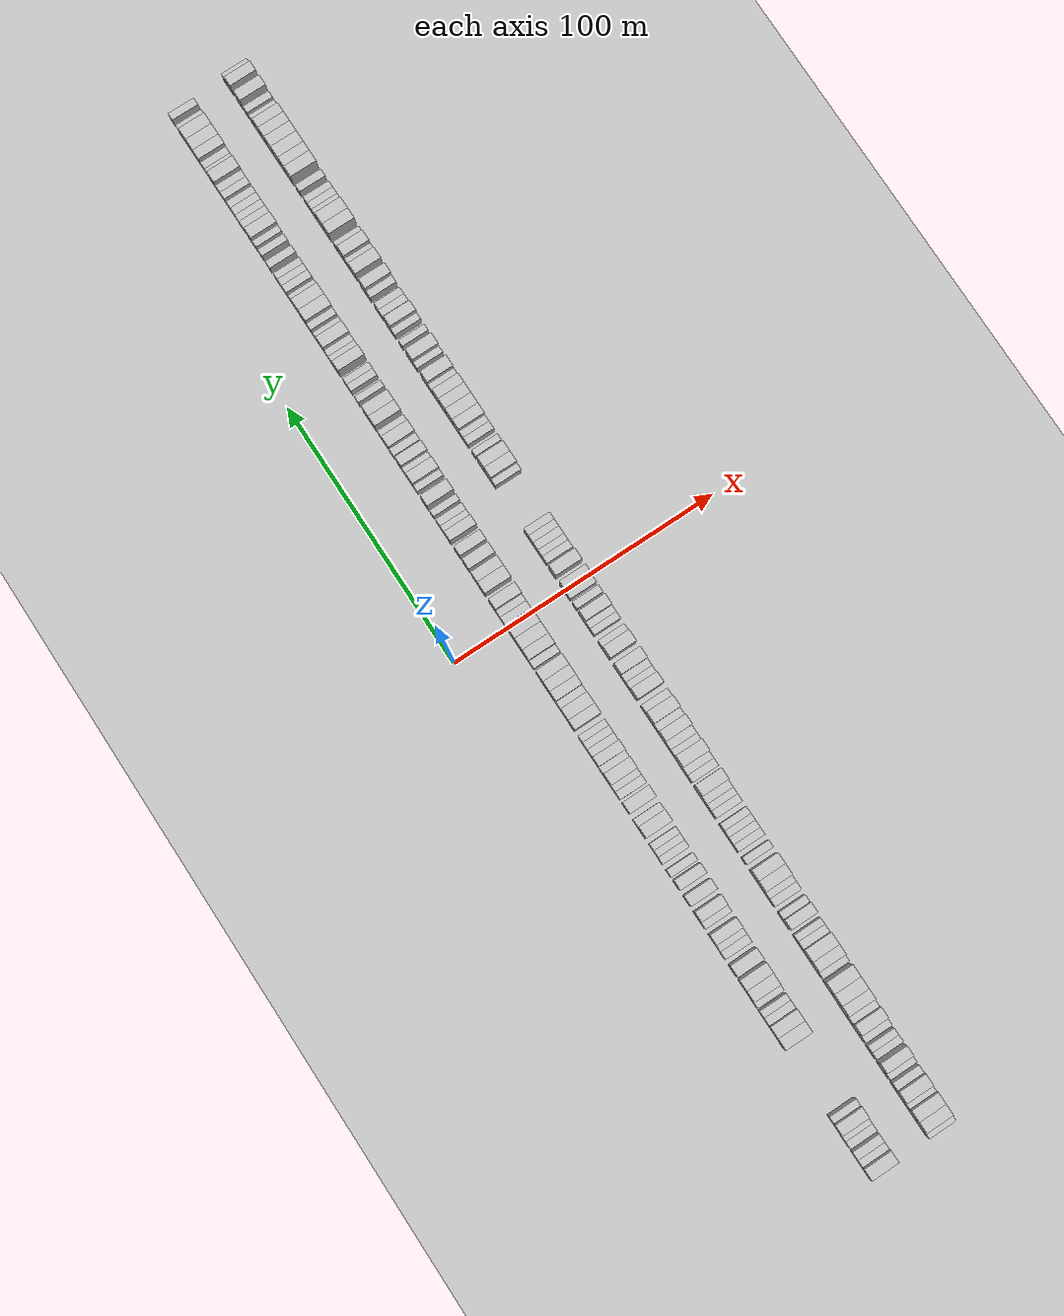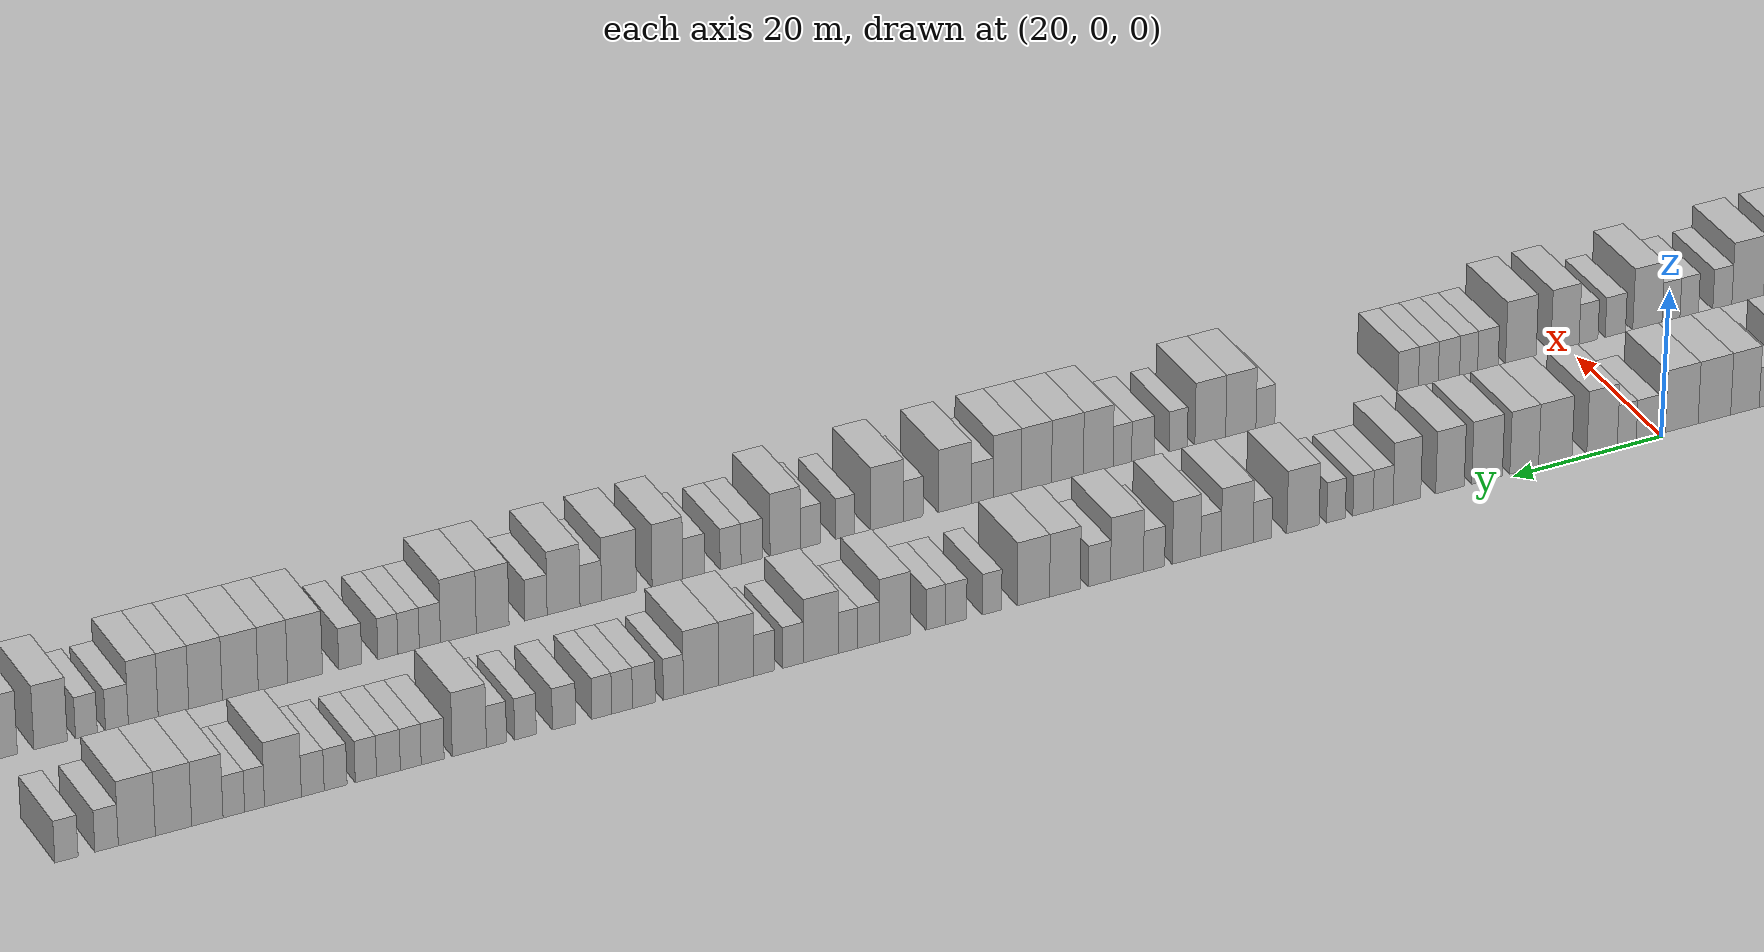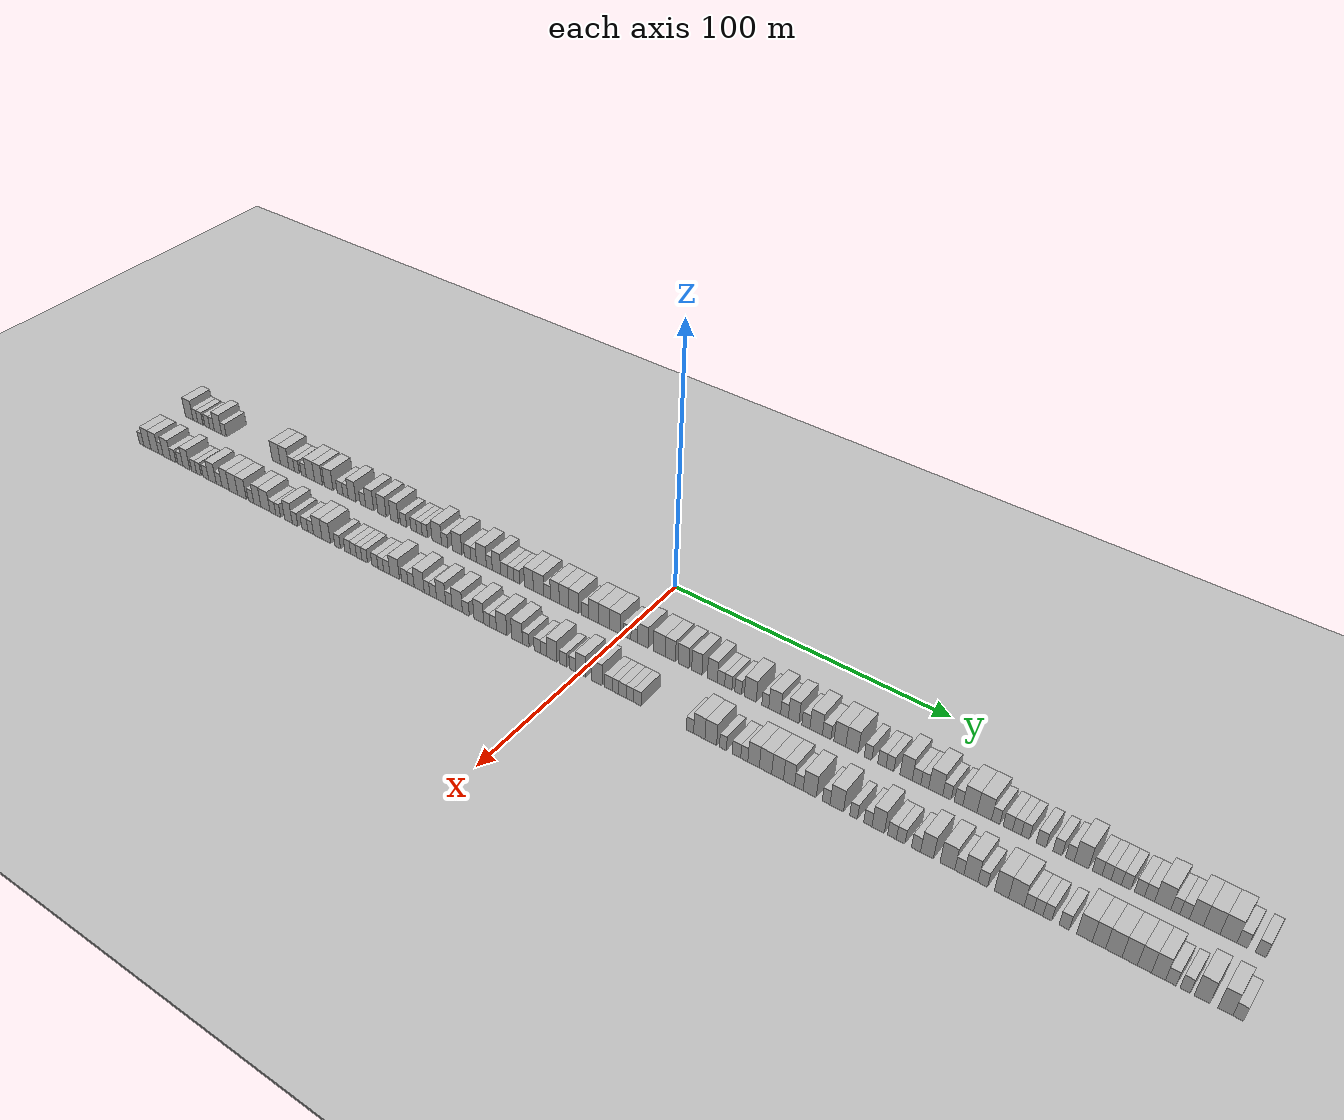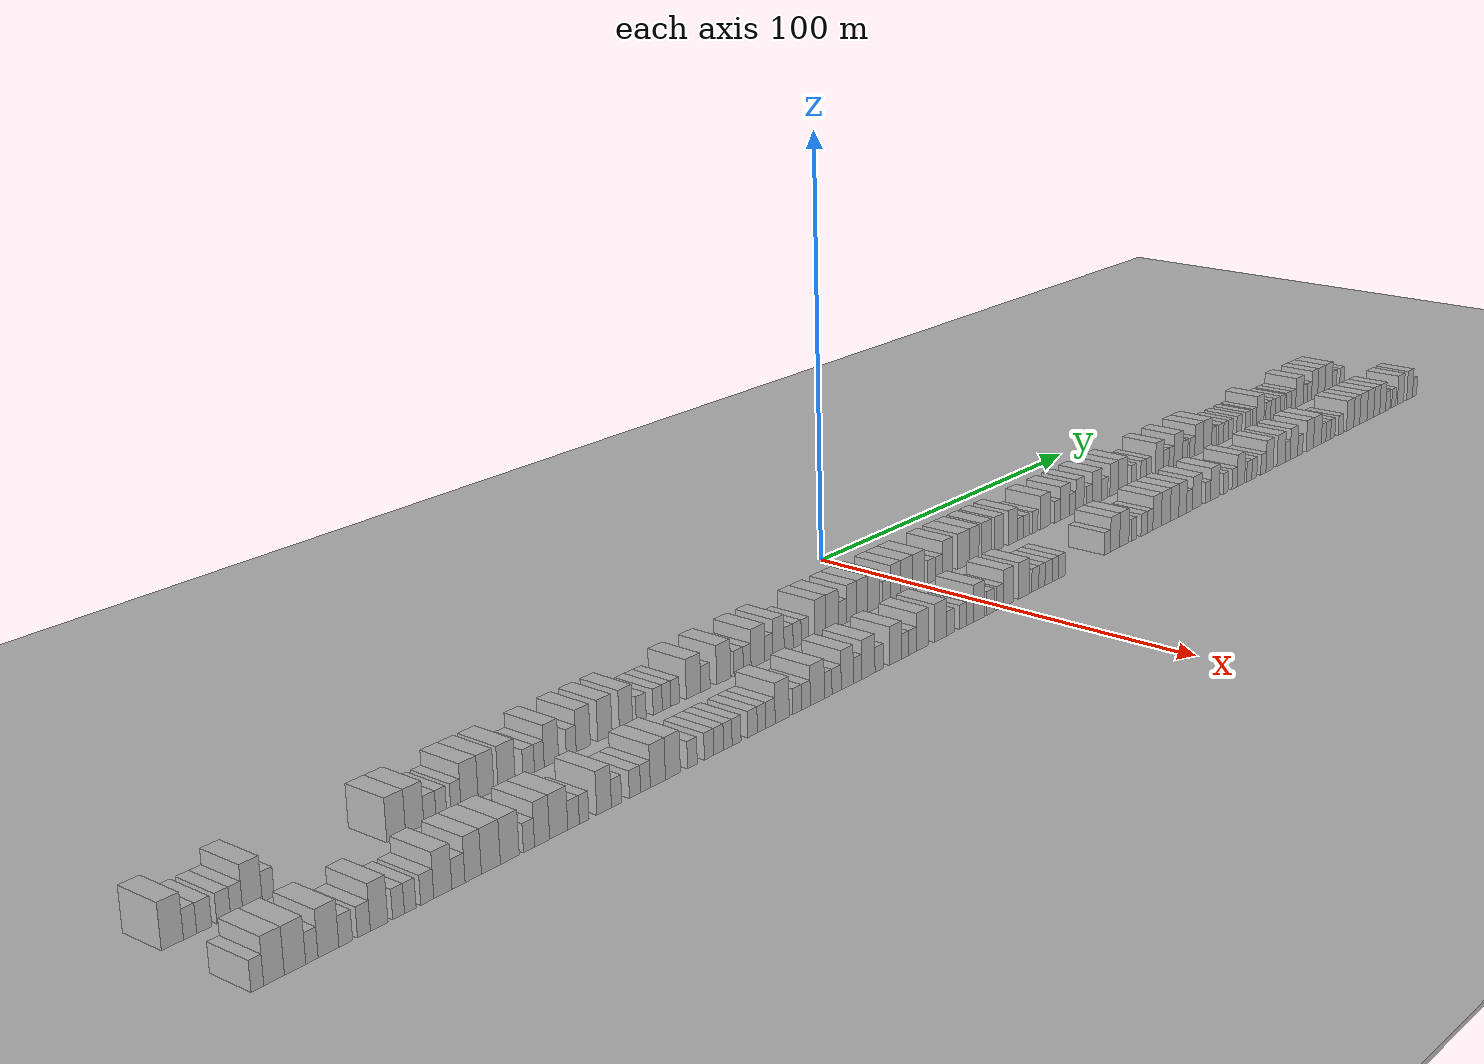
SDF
<?xml version="1.0" encoding="utf-8"?>

<sdf version="1.6">

   <world name="default">

      <gui fullscreen="0">

         <camera name="user_camera">

            <pose>-15 0 4.57585 0 0 0</pose>

            <view_controller>orbit</view_controller>

         </camera>

      </gui>

      <scene>

         <sky>

           <clouds>

             <speed>12</speed>

           </clouds>

         </sky>

         <ambient>0.4 0.4 0.4 1</ambient>

         <background>0.7 0.7 0.7 1</background>

         <shadows>1</shadows>

      </scene>

      <gravity>0 0 -9.8066</gravity>

      <magnetic_field>6e-06 2.3e-05 -4.2e-05</magnetic_field>

      <physics default="0" name="default_physics" type="ode">

         <ode>

            <solver>

               <type>quick</type>

               <iters>10</iters>

               <sor>1.0</sor>

               <use_dynamic_moi_rescaling>0</use_dynamic_moi_rescaling>

            </solver>

            <constraints>

               <cfm>0</cfm>

               <erp>0.2</erp>

               <contact_max_correcting_vel>100</contact_max_correcting_vel>

               <contact_surface_layer>0.001</contact_surface_layer>

            </constraints>

         </ode>

         <max_step_size>0.004</max_step_size>

         <real_time_factor>1</real_time_factor>

         <real_time_update_rate>250</real_time_update_rate>

      </physics>

      <light name="sun" type="directional">

         <cast_shadows>1</cast_shadows>

         <pose>0 0 10 0 0 0</pose>

         <diffuse>0.8 0.8 0.8 1</diffuse>

         <specular>0.2 0.2 0.2 1</specular>

         <attenuation>

            <range>1000</range>

            <constant>0.9</constant>

            <linear>0.01</linear>

            <quadratic>0.001</quadratic>

         </attenuation>

         <direction>-0.5 0.1 -0.9</direction>

      </light>

      <include>

         <name>ground_plane_1</name>

         <uri>model://HANNAS_ground_plane</uri>

         <pose>0 0 0  0 0 0</pose>

      </include>

      <include>

         <name>ground_plane_2</name>

         <uri>model://HANNAS_ground_plane</uri>

         <pose>100 0 0  0 0 0</pose>

      </include>

      <model name="building_1">

         <static>1</static>

         <pose frame="">25.0000 -201.8776 0 0.000000 0.000000 0.000000</pose>

         <link name="link">

            <pose frame="">0 0 4.50 0 0 0</pose>

            <collision name="collision">

               <geometry>

                  <box>

                     <size>10.0000 4.2448 9.0000</size>

                  </box>

               </geometry>

               <max_contacts>10</max_contacts>

               <surface>

                  <contact>

                     <ode/>

                  </contact>

                  <bounce/>

                  <friction>

                     <torsional>

                        <ode/>

                     </torsional>

                     <ode/>

                  </friction>

               </surface>

            </collision>

            <visual name="visual">

               <cast_shadows>0</cast_shadows>

               <geometry>

                  <box>

                     <size>10.0000 4.2448 9.0000</size>

                  </box>

               </geometry>

               <material>

                  <script>

                     <uri>model://HANNAS_wall/materials/scripts</uri>

                     <uri>model://HANNAS_wall/materials/textures</uri>

                     <name>vrc/HANNAS_wall</name>

                  </script>

               </material>

            </visual>

            <self_collide>0</self_collide>

            <enable_wind>0</enable_wind>

            <kinematic>0</kinematic>

         </link>

      </model>

      <model name="building_2">

         <static>1</static>

         <pose frame="">25.0000 -198.4805 0 0.000000 0.000000 0.000000</pose>

         <link name="link">

            <pose frame="">0 0 3.00 0 0 0</pose>

            <collision name="collision">

               <geometry>

                  <box>

                     <size>10.0000 2.5494 6.0000</size>

                  </box>

               </geometry>

               <max_contacts>10</max_contacts>

               <surface>

                  <contact>

                     <ode/>

                  </contact>

                  <bounce/>

                  <friction>

                     <torsional>

                        <ode/>

                     </torsional>

                     <ode/>

                  </friction>

               </surface>

            </collision>

            <visual name="visual">

               <cast_shadows>0</cast_shadows>

               <geometry>

                  <box>

                     <size>10.0000 2.5494 6.0000</size>

                  </box>

               </geometry>

               <material>

                  <script>

                     <uri>model://HANNAS_wall/materials/scripts</uri>

                     <uri>model://HANNAS_wall/materials/textures</uri>

                     <name>vrc/HANNAS_wall</name>

                  </script>

               </material>

            </visual>

            <self_collide>0</self_collide>

            <enable_wind>0</enable_wind>

            <kinematic>0</kinematic>

         </link>

      </model>

      <model name="building_3">

         <static>1</static>

         <pose frame="">25.0000 -195.7391 0 0.000000 0.000000 0.000000</pose>

         <link name="link">

            <pose frame="">0 0 3.00 0 0 0</pose>

            <collision name="collision">

               <geometry>

                  <box>

                     <size>10.0000 2.9334 6.0000</size>

                  </box>

               </geometry>

               <max_contacts>10</max_contacts>

               <surface>

                  <contact>

                     <ode/>

                  </contact>

                  <bounce/>

                  <friction>

                     <torsional>

                        <ode/>

                     </torsional>

                     <ode/>

                  </friction>

               </surface>

            </collision>

            <visual name="visual">

               <cast_shadows>0</cast_shadows>

               <geometry>

                  <box>

                     <size>10.0000 2.9334 6.0000</size>

                  </box>

               </geometry>

               <material>

                  <script>

                     <uri>model://HANNAS_wall/materials/scripts</uri>

                     <uri>model://HANNAS_wall/materials/textures</uri>

                     <name>vrc/HANNAS_wall</name>

                  </script>

               </material>

            </visual>

            <self_collide>0</self_collide>

            <enable_wind>0</enable_wind>

            <kinematic>0</kinematic>

         </link>

      </model>

      <model name="building_4">

         <static>1</static>

         <pose frame="">25.0000 -191.9077 0 0.000000 0.000000 0.000000</pose>

         <link name="link">

            <pose frame="">0 0 3.00 0 0 0</pose>

            <collision name="collision">

               <geometry>

                  <box>

                     <size>10.0000 2.7295 6.0000</size>

                  </box>

               </geometry>

               <max_contacts>10</max_contacts>

               <surface>

                  <contact>

                     <ode/>

                  </contact>

                  <bounce/>

                  <friction>

                     <torsional>

                        <ode/>

                     </torsional>

                     <ode/>

                  </friction>

               </surface>

            </collision>

            <visual name="visual">

               <cast_shadows>0</cast_shadows>

               <geometry>

                  <box>

                     <size>10.0000 2.7295 6.0000</size>

                  </box>

               </geometry>

               <material>

                  <script>

                     <uri>model://HANNAS_wall/materials/scripts</uri>

                     <uri>model://HANNAS_wall/materials/textures</uri>

                     <name>vrc/HANNAS_wall</name>

                  </script>

               </material>

            </visual>

            <self_collide>0</self_collide>

            <enable_wind>0</enable_wind>

            <kinematic>0</kinematic>

         </link>

      </model>

      <model name="building_5">

         <static>1</static>

         <pose frame="">25.0000 -189.3272 0 0.000000 0.000000 0.000000</pose>

         <link name="link">

            <pose frame="">0 0 3.00 0 0 0</pose>

            <collision name="collision">

               <geometry>

                  <box>

                     <size>10.0000 2.4314 6.0000</size>

                  </box>

               </geometry>

               <max_contacts>10</max_contacts>

               <surface>

                  <contact>

                     <ode/>

                  </contact>

                  <bounce/>

                  <friction>

                     <torsional>

                        <ode/>

                     </torsional>

                     <ode/>

                  </friction>

               </surface>

            </collision>

            <visual name="visual">

               <cast_shadows>0</cast_shadows>

               <geometry>

                  <box>

                     <size>10.0000 2.4314 6.0000</size>

                  </box>

               </geometry>

               <material>

                  <script>

                     <uri>model://HANNAS_wall/materials/scripts</uri>

                     <uri>model://HANNAS_wall/materials/textures</uri>

                     <name>vrc/HANNAS_wall</name>

                  </script>

               </material>

            </visual>

            <self_collide>0</self_collide>

            <enable_wind>0</enable_wind>

            <kinematic>0</kinematic>

         </link>

      </model>

      <model name="building_6">

         <static>1</static>

         <pose frame="">25.0000 -186.1348 0 0.000000 0.000000 0.000000</pose>

         <link name="link">

            <pose frame="">0 0 4.50 0 0 0</pose>

            <collision name="collision">

               <geometry>

                  <box>

                     <size>10.0000 3.9535 9.0000</size>

                  </box>

               </geometry>

               <max_contacts>10</max_contacts>

               <surface>

                  <contact>

                     <ode/>

                  </contact>

                  <bounce/>

                  <friction>

                     <torsional>

                        <ode/>

                     </torsional>

                     <ode/>

                  </friction>

               </surface>

            </collision>

            <visual name="visual">

               <cast_shadows>0</cast_shadows>

               <geometry>

                  <box>

                     <size>10.0000 3.9535 9.0000</size>

                  </box>

               </geometry>

               <material>

                  <script>

                     <uri>model://HANNAS_wall/materials/scripts</uri>

                     <uri>model://HANNAS_wall/materials/textures</uri>

                     <name>vrc/HANNAS_wall</name>

                  </script>

               </material>

            </visual>

            <self_collide>0</self_collide>

            <enable_wind>0</enable_wind>

            <kinematic>0</kinematic>

         </link>

      </model>

      <model name="building_7">

         <static>1</static>

         <pose frame="">25.0000 -182.9249 0 0.000000 0.000000 0.000000</pose>

         <link name="link">

            <pose frame="">0 0 3.00 0 0 0</pose>

            <collision name="collision">

               <geometry>

                  <box>

                     <size>10.0000 2.4664 6.0000</size>

                  </box>

               </geometry>

               <max_contacts>10</max_contacts>

               <surface>

                  <contact>

                     <ode/>

                  </contact>

                  <bounce/>

                  <friction>

                     <torsional>

                        <ode/>

                     </torsional>

                     <ode/>

                  </friction>

               </surface>

            </collision>

            <visual name="visual">

               <cast_shadows>0</cast_shadows>

               <geometry>

                  <box>

                     <size>10.0000 2.4664 6.0000</size>

                  </box>

               </geometry>

               <material>

                  <script>

                     <uri>model://HANNAS_wall/materials/scripts</uri>

                     <uri>model://HANNAS_wall/materials/textures</uri>

                     <name>vrc/HANNAS_wall</name>

                  </script>

               </material>

            </visual>

            <self_collide>0</self_collide>

            <enable_wind>0</enable_wind>

            <kinematic>0</kinematic>

         </link>

      </model>

      <model name="building_8">

         <static>1</static>

         <pose frame="">25.0000 -155.2964 0 0.000000 0.000000 0.000000</pose>

         <link name="link">

            <pose frame="">0 0 4.50 0 0 0</pose>

            <collision name="collision">

               <geometry>

                  <box>

                     <size>10.0000 4.2636 9.0000</size>

                  </box>

               </geometry>

               <max_contacts>10</max_contacts>

               <surface>

                  <contact>

                     <ode/>

                  </contact>

                  <bounce/>

                  <friction>

                     <torsional>

                        <ode/>

                     </torsional>

                     <ode/>

                  </friction>

               </surface>

            </collision>

            <visual name="visual">

               <cast_shadows>0</cast_shadows>

               <geometry>

                  <box>

                     <size>10.0000 4.2636 9.0000</size>

                  </box>

               </geometry>

               <material>

                  <script>

                     <uri>model://HANNAS_wall/materials/scripts</uri>

                     <uri>model://HANNAS_wall/materials/textures</uri>

                     <name>vrc/HANNAS_wall</name>

                  </script>

               </material>

            </visual>

            <self_collide>0</self_collide>

            <enable_wind>0</enable_wind>

            <kinematic>0</kinematic>

         </link>

      </model>

      <model name="building_9">

         <static>1</static>

         <pose frame="">25.0000 -151.0444 0 0.000000 0.000000 0.000000</pose>

         <link name="link">

            <pose frame="">0 0 4.50 0 0 0</pose>

            <collision name="collision">

               <geometry>

                  <box>

                     <size>10.0000 4.2404 9.0000</size>

                  </box>

               </geometry>

               <max_contacts>10</max_contacts>

               <surface>

                  <contact>

                     <ode/>

                  </contact>

                  <bounce/>

                  <friction>

                     <torsional>

                        <ode/>

                     </torsional>

                     <ode/>

                  </friction>

               </surface>

            </collision>

            <visual name="visual">

               <cast_shadows>0</cast_shadows>

               <geometry>

                  <box>

                     <size>10.0000 4.2404 9.0000</size>

                  </box>

               </geometry>

               <material>

                  <script>

                     <uri>model://HANNAS_wall/materials/scripts</uri>

                     <uri>model://HANNAS_wall/materials/textures</uri>

                     <name>vrc/HANNAS_wall</name>

                  </script>

               </material>

            </visual>

            <self_collide>0</self_collide>

            <enable_wind>0</enable_wind>

            <kinematic>0</kinematic>

         </link>

      </model>

      <model name="building_10">

         <static>1</static>

         <pose frame="">25.0000 -147.4846 0 0.000000 0.000000 0.000000</pose>

         <link name="link">

            <pose frame="">0 0 3.00 0 0 0</pose>

            <collision name="collision">

               <geometry>

                  <box>

                     <size>10.0000 2.8792 6.0000</size>

                  </box>

               </geometry>

               <max_contacts>10</max_contacts>

               <surface>

                  <contact>

                     <ode/>

                  </contact>

                  <bounce/>

                  <friction>

                     <torsional>

                        <ode/>

                     </torsional>

                     <ode/>

                  </friction>

               </surface>

            </collision>

            <visual name="visual">

               <cast_shadows>0</cast_shadows>

               <geometry>

                  <box>

                     <size>10.0000 2.8792 6.0000</size>

                  </box>

               </geometry>

               <material>

                  <script>

                     <uri>model://HANNAS_wall/materials/scripts</uri>

                     <uri>model://HANNAS_wall/materials/textures</uri>

                     <name>vrc/HANNAS_wall</name>

                  </script>

               </material>

            </visual>

            <self_collide>0</self_collide>

            <enable_wind>0</enable_wind>

            <kinematic>0</kinematic>

         </link>

      </model>

      <model name="building_11">

         <static>1</static>

         <pose frame="">25.0000 -144.7978 0 0.000000 0.000000 0.000000</pose>

         <link name="link">

            <pose frame="">0 0 3.00 0 0 0</pose>

            <collision name="collision">

               <geometry>

                  <box>

                     <size>10.0000 2.4943 6.0000</size>

                  </box>

               </geometry>

               <max_contacts>10</max_contacts>

               <surface>

                  <contact>

                     <ode/>

                  </contact>

                  <bounce/>

                  <friction>

                     <torsional>

                        <ode/>

                     </torsional>

                     <ode/>

                  </friction>

               </surface>

            </collision>

            <visual name="visual">

               <cast_shadows>0</cast_shadows>

               <geometry>

                  <box>

                     <size>10.0000 2.4943 6.0000</size>

                  </box>

               </geometry>

               <material>

                  <script>

                     <uri>model://HANNAS_wall/materials/scripts</uri>

                     <uri>model://HANNAS_wall/materials/textures</uri>

                     <name>vrc/HANNAS_wall</name>

                  </script>

               </material>

            </visual>

            <self_collide>0</self_collide>

            <enable_wind>0</enable_wind>

            <kinematic>0</kinematic>

         </link>

      </model>

      <model name="building_12">

         <static>1</static>

         <pose frame="">25.0000 -141.3342 0 0.000000 0.000000 0.000000</pose>

         <link name="link">

            <pose frame="">0 0 3.00 0 0 0</pose>

            <collision name="collision">

               <geometry>

                  <box>

                     <size>10.0000 2.4330 6.0000</size>

                  </box>

               </geometry>

               <max_contacts>10</max_contacts>

               <surface>

                  <contact>

                     <ode/>

                  </contact>

                  <bounce/>

                  <friction>

                     <torsional>

                        <ode/>

                     </torsional>

                     <ode/>

                  </friction>

               </surface>

            </collision>

            <visual name="visual">

               <cast_shadows>0</cast_shadows>

               <geometry>

                  <box>

                     <size>10.0000 2.4330 6.0000</size>

                  </box>

               </geometry>

               <material>

                  <script>

                     <uri>model://HANNAS_wall/materials/scripts</uri>

                     <uri>model://HANNAS_wall/materials/textures</uri>

                     <name>vrc/HANNAS_wall</name>

                  </script>

               </material>

            </visual>

            <self_collide>0</self_collide>

            <enable_wind>0</enable_wind>

            <kinematic>0</kinematic>

         </link>

      </model>

      <model name="building_13">

         <static>1</static>

         <pose frame="">25.0000 -138.0355 0 0.000000 0.000000 0.000000</pose>

         <link name="link">

            <pose frame="">0 0 4.50 0 0 0</pose>

            <collision name="collision">

               <geometry>

                  <box>

                     <size>10.0000 4.1645 9.0000</size>

                  </box>

               </geometry>

               <max_contacts>10</max_contacts>

               <surface>

                  <contact>

                     <ode/>

                  </contact>

                  <bounce/>

                  <friction>

                     <torsional>

                        <ode/>

                     </torsional>

                     <ode/>

                  </friction>

               </surface>

            </collision>

            <visual name="visual">

               <cast_shadows>0</cast_shadows>

               <geometry>

                  <box>

                     <size>10.0000 4.1645 9.0000</size>

                  </box>

               </geometry>

               <material>

                  <script>

                     <uri>model://HANNAS_wall/materials/scripts</uri>

                     <uri>model://HANNAS_wall/materials/textures</uri>

                     <name>vrc/HANNAS_wall</name>

                  </script>

               </material>

            </visual>

            <self_collide>0</self_collide>

            <enable_wind>0</enable_wind>

            <kinematic>0</kinematic>

         </link>

      </model>

      <model name="building_14">

         <static>1</static>

         <pose frame="">25.0000 -133.9975 0 0.000000 0.000000 0.000000</pose>

         <link name="link">

            <pose frame="">0 0 4.50 0 0 0</pose>

            <collision name="collision">

               <geometry>

                  <box>

                     <size>10.0000 3.9115 9.0000</size>

                  </box>

               </geometry>

               <max_contacts>10</max_contacts>

               <surface>

                  <contact>

                     <ode/>

                  </contact>

                  <bounce/>

                  <friction>

                     <torsional>

                        <ode/>

                     </torsional>

                     <ode/>

                  </friction>

               </surface>

            </collision>

            <visual name="visual">

               <cast_shadows>0</cast_shadows>

               <geometry>

                  <box>

                     <size>10.0000 3.9115 9.0000</size>

                  </box>

               </geometry>

               <material>

                  <script>

                     <uri>model://HANNAS_wall/materials/scripts</uri>

                     <uri>model://HANNAS_wall/materials/textures</uri>

                     <name>vrc/HANNAS_wall</name>

                  </script>

               </material>

            </visual>

            <self_collide>0</self_collide>

            <enable_wind>0</enable_wind>

            <kinematic>0</kinematic>

         </link>

      </model>

      <model name="building_15">

         <static>1</static>

         <pose frame="">25.0000 -128.8950 0 0.000000 0.000000 0.000000</pose>

         <link name="link">

            <pose frame="">0 0 4.50 0 0 0</pose>

            <collision name="collision">

               <geometry>

                  <box>

                     <size>10.0000 4.2936 9.0000</size>

                  </box>

               </geometry>

               <max_contacts>10</max_contacts>

               <surface>

                  <contact>

                     <ode/>

                  </contact>

                  <bounce/>

                  <friction>

                     <torsional>

                        <ode/>

                     </torsional>

                     <ode/>

                  </friction>

               </surface>

            </collision>

            <visual name="visual">

               <cast_shadows>0</cast_shadows>

               <geometry>

                  <box>

                     <size>10.0000 4.2936 9.0000</size>

                  </box>

               </geometry>

               <material>

                  <script>

                     <uri>model://HANNAS_wall/materials/scripts</uri>

                     <uri>model://HANNAS_wall/materials/textures</uri>

                     <name>vrc/HANNAS_wall</name>

                  </script>

               </material>

            </visual>

            <self_collide>0</self_collide>

            <enable_wind>0</enable_wind>

            <kinematic>0</kinematic>

         </link>

      </model>

      <model name="building_16">

         <static>1</static>

         <pose frame="">25.0000 -123.3025 0 0.000000 0.000000 0.000000</pose>

         <link name="link">

            <pose frame="">0 0 3.00 0 0 0</pose>

            <collision name="collision">

               <geometry>

                  <box>

                     <size>10.0000 2.8914 6.0000</size>

                  </box>

               </geometry>

               <max_contacts>10</max_contacts>

               <surface>

                  <contact>

                     <ode/>

                  </contact>

                  <bounce/>

                  <friction>

                     <torsional>

                        <ode/>

                     </torsional>

                     <ode/>

                  </friction>

               </surface>

            </collision>

            <visual name="visual">

               <cast_shadows>0</cast_shadows>

               <geometry>

                  <box>

                     <size>10.0000 2.8914 6.0000</size>

                  </box>

               </geometry>

               <material>

                  <script>

                     <uri>model://HANNAS_wall/materials/scripts</uri>

                     <uri>model://HANNAS_wall/materials/textures</uri>

                     <name>vrc/HANNAS_wall</name>

                  </script>

               </material>

            </visual>

            <self_collide>0</self_collide>

            <enable_wind>0</enable_wind>

            <kinematic>0</kinematic>

         </link>

      </model>

      <model name="building_17">

         <static>1</static>

         <pose frame="">25.0000 -120.5999 0 0.000000 0.000000 0.000000</pose>

         <link name="link">

            <pose frame="">0 0 3.00 0 0 0</pose>

            <collision name="collision">

               <geometry>

                  <box>

                     <size>10.0000 2.5139 6.0000</size>

                  </box>

               </geometry>

               <max_contacts>10</max_contacts>

               <surface>

                  <contact>

                     <ode/>

                  </contact>

                  <bounce/>

                  <friction>

                     <torsional>

                        <ode/>

                     </torsional>

                     <ode/>

                  </friction>

               </surface>

            </collision>

            <visual name="visual">

               <cast_shadows>0</cast_shadows>

               <geometry>

                  <box>

                     <size>10.0000 2.5139 6.0000</size>

                  </box>

               </geometry>

               <material>

                  <script>

                     <uri>model://HANNAS_wall/materials/scripts</uri>

                     <uri>model://HANNAS_wall/materials/textures</uri>

                     <name>vrc/HANNAS_wall</name>

                  </script>

               </material>

            </visual>

            <self_collide>0</self_collide>

            <enable_wind>0</enable_wind>

            <kinematic>0</kinematic>

         </link>

      </model>

      <model name="building_18">

         <static>1</static>

         <pose frame="">25.0000 -117.4557 0 0.000000 0.000000 0.000000</pose>

         <link name="link">

            <pose frame="">0 0 4.50 0 0 0</pose>

            <collision name="collision">

               <geometry>

                  <box>

                     <size>10.0000 3.7745 9.0000</size>

                  </box>

               </geometry>

               <max_contacts>10</max_contacts>

               <surface>

                  <contact>

                     <ode/>

                  </contact>

                  <bounce/>

                  <friction>

                     <torsional>

                        <ode/>

                     </torsional>

                     <ode/>

                  </friction>

               </surface>

            </collision>

            <visual name="visual">

               <cast_shadows>0</cast_shadows>

               <geometry>

                  <box>

                     <size>10.0000 3.7745 9.0000</size>

                  </box>

               </geometry>

               <material>

                  <script>

                     <uri>model://HANNAS_wall/materials/scripts</uri>

                     <uri>model://HANNAS_wall/materials/textures</uri>

                     <name>vrc/HANNAS_wall</name>

                  </script>

               </material>

            </visual>

            <self_collide>0</self_collide>

            <enable_wind>0</enable_wind>

            <kinematic>0</kinematic>

         </link>

      </model>

      <model name="building_19">

         <static>1</static>

         <pose frame="">25.0000 -112.2520 0 0.000000 0.000000 0.000000</pose>

         <link name="link">

            <pose frame="">0 0 3.00 0 0 0</pose>

            <collision name="collision">

               <geometry>

                  <box>

                     <size>10.0000 2.6328 6.0000</size>

                  </box>

               </geometry>

               <max_contacts>10</max_contacts>

               <surface>

                  <contact>

                     <ode/>

                  </contact>

                  <bounce/>

                  <friction>

                     <torsional>

                        <ode/>

                     </torsional>

                     <ode/>

                  </friction>

               </surface>

            </collision>

            <visual name="visual">

               <cast_shadows>0</cast_shadows>

               <geometry>

                  <box>

                     <size>10.0000 2.6328 6.0000</size>

                  </box>

               </geometry>

               <material>

                  <script>

                     <uri>model://HANNAS_wall/materials/scripts</uri>

                     <uri>model://HANNAS_wall/materials/textures</uri>

                     <name>vrc/HANNAS_wall</name>

                  </script>

               </material>

            </visual>

            <self_collide>0</self_collide>

            <enable_wind>0</enable_wind>

            <kinematic>0</kinematic>

         </link>

      </model>

      <model name="building_20">

         <static>1</static>

         <pose frame="">25.0000 -109.0311 0 0.000000 0.000000 0.000000</pose>

         <link name="link">

            <pose frame="">0 0 4.50 0 0 0</pose>

            <collision name="collision">

               <geometry>

                  <box>

                     <size>10.0000 3.8090 9.0000</size>

                  </box>

               </geometry>

               <max_contacts>10</max_contacts>

               <surface>

                  <contact>

                     <ode/>

                  </contact>

                  <bounce/>

                  <friction>

                     <torsional>

                        <ode/>

                     </torsional>

                     <ode/>

                  </friction>

               </surface>

            </collision>

            <visual name="visual">

               <cast_shadows>0</cast_shadows>

               <geometry>

                  <box>

                     <size>10.0000 3.8090 9.0000</size>

                  </box>

               </geometry>

               <material>

                  <script>

                     <uri>model://HANNAS_wall/materials/scripts</uri>

                     <uri>model://HANNAS_wall/materials/textures</uri>

                     <name>vrc/HANNAS_wall</name>

                  </script>

               </material>

            </visual>

            <self_collide>0</self_collide>

            <enable_wind>0</enable_wind>

            <kinematic>0</kinematic>

         </link>

      </model>

      <model name="building_21">

         <static>1</static>

         <pose frame="">25.0000 -103.1568 0 0.000000 0.000000 0.000000</pose>

         <link name="link">

            <pose frame="">0 0 4.50 0 0 0</pose>

            <collision name="collision">

               <geometry>

                  <box>

                     <size>10.0000 3.9398 9.0000</size>

                  </box>

               </geometry>

               <max_contacts>10</max_contacts>

               <surface>

                  <contact>

                     <ode/>

                  </contact>

                  <bounce/>

                  <friction>

                     <torsional>

                        <ode/>

                     </torsional>

                     <ode/>

                  </friction>

               </surface>

            </collision>

            <visual name="visual">

               <cast_shadows>0</cast_shadows>

               <geometry>

                  <box>

                     <size>10.0000 3.9398 9.0000</size>

                  </box>

               </geometry>

               <material>

                  <script>

                     <uri>model://HANNAS_wall/materials/scripts</uri>

                     <uri>model://HANNAS_wall/materials/textures</uri>

                     <name>vrc/HANNAS_wall</name>

                  </script>

               </material>

            </visual>

            <self_collide>0</self_collide>

            <enable_wind>0</enable_wind>

            <kinematic>0</kinematic>

         </link>

      </model>

      <model name="building_22">

         <static>1</static>

         <pose frame="">25.0000 -97.3289 0 0.000000 0.000000 0.000000</pose>

         <link name="link">

            <pose frame="">0 0 4.50 0 0 0</pose>

            <collision name="collision">

               <geometry>

                  <box>

                     <size>10.0000 3.7160 9.0000</size>

                  </box>

               </geometry>

               <max_contacts>10</max_contacts>

               <surface>

                  <contact>

                     <ode/>

                  </contact>

                  <bounce/>

                  <friction>

                     <torsional>

                        <ode/>

                     </torsional>

                     <ode/>

                  </friction>

               </surface>

            </collision>

            <visual name="visual">

               <cast_shadows>0</cast_shadows>

               <geometry>

                  <box>

                     <size>10.0000 3.7160 9.0000</size>

                  </box>

               </geometry>

               <material>

                  <script>

                     <uri>model://HANNAS_wall/materials/scripts</uri>

                     <uri>model://HANNAS_wall/materials/textures</uri>

                     <name>vrc/HANNAS_wall</name>

                  </script>

               </material>

            </visual>

            <self_collide>0</self_collide>

            <enable_wind>0</enable_wind>

            <kinematic>0</kinematic>

         </link>

      </model>

      <model name="building_23">

         <static>1</static>

         <pose frame="">25.0000 -93.0584 0 0.000000 0.000000 0.000000</pose>

         <link name="link">

            <pose frame="">0 0 3.00 0 0 0</pose>

            <collision name="collision">

               <geometry>

                  <box>

                     <size>10.0000 2.8249 6.0000</size>

                  </box>

               </geometry>

               <max_contacts>10</max_contacts>

               <surface>

                  <contact>

                     <ode/>

                  </contact>

                  <bounce/>

                  <friction>

                     <torsional>

                        <ode/>

                     </torsional>

                     <ode/>

                  </friction>

               </surface>

            </collision>

            <visual name="visual">

               <cast_shadows>0</cast_shadows>

               <geometry>

                  <box>

                     <size>10.0000 2.8249 6.0000</size>

                  </box>

               </geometry>

               <material>

                  <script>

                     <uri>model://HANNAS_wall/materials/scripts</uri>

                     <uri>model://HANNAS_wall/materials/textures</uri>

                     <name>vrc/HANNAS_wall</name>

                  </script>

               </material>

            </visual>

            <self_collide>0</self_collide>

            <enable_wind>0</enable_wind>

            <kinematic>0</kinematic>

         </link>

      </model>

      <model name="building_24">

         <static>1</static>

         <pose frame="">25.0000 -88.3284 0 0.000000 0.000000 0.000000</pose>

         <link name="link">

            <pose frame="">0 0 3.00 0 0 0</pose>

            <collision name="collision">

               <geometry>

                  <box>

                     <size>10.0000 2.6352 6.0000</size>

                  </box>

               </geometry>

               <max_contacts>10</max_contacts>

               <surface>

                  <contact>

                     <ode/>

                  </contact>

                  <bounce/>

                  <friction>

                     <torsional>

                        <ode/>

                     </torsional>

                     <ode/>

                  </friction>

               </surface>

            </collision>

            <visual name="visual">

               <cast_shadows>0</cast_shadows>

               <geometry>

                  <box>

                     <size>10.0000 2.6352 6.0000</size>

                  </box>

               </geometry>

               <material>

                  <script>

                     <uri>model://HANNAS_wall/materials/scripts</uri>

                     <uri>model://HANNAS_wall/materials/textures</uri>

                     <name>vrc/HANNAS_wall</name>

                  </script>

               </material>

            </visual>

            <self_collide>0</self_collide>

            <enable_wind>0</enable_wind>

            <kinematic>0</kinematic>

         </link>

      </model>

      <model name="building_25">

         <static>1</static>

         <pose frame="">25.0000 -85.7696 0 0.000000 0.000000 0.000000</pose>

         <link name="link">

            <pose frame="">0 0 3.00 0 0 0</pose>

            <collision name="collision">

               <geometry>

                  <box>

                     <size>10.0000 2.4825 6.0000</size>

                  </box>

               </geometry>

               <max_contacts>10</max_contacts>

               <surface>

                  <contact>

                     <ode/>

                  </contact>

                  <bounce/>

                  <friction>

                     <torsional>

                        <ode/>

                     </torsional>

                     <ode/>

                  </friction>

               </surface>

            </collision>

            <visual name="visual">

               <cast_shadows>0</cast_shadows>

               <geometry>

                  <box>

                     <size>10.0000 2.4825 6.0000</size>

                  </box>

               </geometry>

               <material>

                  <script>

                     <uri>model://HANNAS_wall/materials/scripts</uri>

                     <uri>model://HANNAS_wall/materials/textures</uri>

                     <name>vrc/HANNAS_wall</name>

                  </script>

               </material>

            </visual>

            <self_collide>0</self_collide>

            <enable_wind>0</enable_wind>

            <kinematic>0</kinematic>

         </link>

      </model>

      <model name="building_26">

         <static>1</static>

         <pose frame="">25.0000 -83.2699 0 0.000000 0.000000 0.000000</pose>

         <link name="link">

            <pose frame="">0 0 3.00 0 0 0</pose>

            <collision name="collision">

               <geometry>

                  <box>

                     <size>10.0000 2.5168 6.0000</size>

                  </box>

               </geometry>

               <max_contacts>10</max_contacts>

               <surface>

                  <contact>

                     <ode/>

                  </contact>

                  <bounce/>

                  <friction>

                     <torsional>

                        <ode/>

                     </torsional>

                     <ode/>

                  </friction>

               </surface>

            </collision>

            <visual name="visual">

               <cast_shadows>0</cast_shadows>

               <geometry>

                  <box>

                     <size>10.0000 2.5168 6.0000</size>

                  </box>

               </geometry>

               <material>

                  <script>

                     <uri>model://HANNAS_wall/materials/scripts</uri>

                     <uri>model://HANNAS_wall/materials/textures</uri>

                     <name>vrc/HANNAS_wall</name>

                  </script>

               </material>

            </visual>

            <self_collide>0</self_collide>

            <enable_wind>0</enable_wind>

            <kinematic>0</kinematic>

         </link>

      </model>

      <model name="building_27">

         <static>1</static>

         <pose frame="">25.0000 -77.8490 0 0.000000 0.000000 0.000000</pose>

         <link name="link">

            <pose frame="">0 0 4.50 0 0 0</pose>

            <collision name="collision">

               <geometry>

                  <box>

                     <size>10.0000 4.3251 9.0000</size>

                  </box>

               </geometry>

               <max_contacts>10</max_contacts>

               <surface>

                  <contact>

                     <ode/>

                  </contact>

                  <bounce/>

                  <friction>

                     <torsional>

                        <ode/>

                     </torsional>

                     <ode/>

                  </friction>

               </surface>

            </collision>

            <visual name="visual">

               <cast_shadows>0</cast_shadows>

               <geometry>

                  <box>

                     <size>10.0000 4.3251 9.0000</size>

                  </box>

               </geometry>

               <material>

                  <script>

                     <uri>model://HANNAS_wall/materials/scripts</uri>

                     <uri>model://HANNAS_wall/materials/textures</uri>

                     <name>vrc/HANNAS_wall</name>

                  </script>

               </material>

            </visual>

            <self_collide>0</self_collide>

            <enable_wind>0</enable_wind>

            <kinematic>0</kinematic>

         </link>

      </model>

      <model name="building_28">

         <static>1</static>

         <pose frame="">25.0000 -74.2833 0 0.000000 0.000000 0.000000</pose>

         <link name="link">

            <pose frame="">0 0 3.00 0 0 0</pose>

            <collision name="collision">

               <geometry>

                  <box>

                     <size>10.0000 2.8064 6.0000</size>

                  </box>

               </geometry>

               <max_contacts>10</max_contacts>

               <surface>

                  <contact>

                     <ode/>

                  </contact>

                  <bounce/>

                  <friction>

                     <torsional>

                        <ode/>

                     </torsional>

                     <ode/>

                  </friction>

               </surface>

            </collision>

            <visual name="visual">

               <cast_shadows>0</cast_shadows>

               <geometry>

                  <box>

                     <size>10.0000 2.8064 6.0000</size>

                  </box>

               </geometry>

               <material>

                  <script>

                     <uri>model://HANNAS_wall/materials/scripts</uri>

                     <uri>model://HANNAS_wall/materials/textures</uri>

                     <name>vrc/HANNAS_wall</name>

                  </script>

               </material>

            </visual>

            <self_collide>0</self_collide>

            <enable_wind>0</enable_wind>

            <kinematic>0</kinematic>

         </link>

      </model>

      <model name="building_29">

         <static>1</static>

         <pose frame="">25.0000 -68.7356 0 0.000000 0.000000 0.000000</pose>

         <link name="link">

            <pose frame="">0 0 4.50 0 0 0</pose>

            <collision name="collision">

               <geometry>

                  <box>

                     <size>10.0000 4.2889 9.0000</size>

                  </box>

               </geometry>

               <max_contacts>10</max_contacts>

               <surface>

                  <contact>

                     <ode/>

                  </contact>

                  <bounce/>

                  <friction>

                     <torsional>

                        <ode/>

                     </torsional>

                     <ode/>

                  </friction>

               </surface>

            </collision>

            <visual name="visual">

               <cast_shadows>0</cast_shadows>

               <geometry>

                  <box>

                     <size>10.0000 4.2889 9.0000</size>

                  </box>

               </geometry>

               <material>

                  <script>

                     <uri>model://HANNAS_wall/materials/scripts</uri>

                     <uri>model://HANNAS_wall/materials/textures</uri>

                     <name>vrc/HANNAS_wall</name>

                  </script>

               </material>

            </visual>

            <self_collide>0</self_collide>

            <enable_wind>0</enable_wind>

            <kinematic>0</kinematic>

         </link>

      </model>

      <model name="building_30">

         <static>1</static>

         <pose frame="">25.0000 -64.1257 0 0.000000 0.000000 0.000000</pose>

         <link name="link">

            <pose frame="">0 0 3.00 0 0 0</pose>

            <collision name="collision">

               <geometry>

                  <box>

                     <size>10.0000 2.9309 6.0000</size>

                  </box>

               </geometry>

               <max_contacts>10</max_contacts>

               <surface>

                  <contact>

                     <ode/>

                  </contact>

                  <bounce/>

                  <friction>

                     <torsional>

                        <ode/>

                     </torsional>

                     <ode/>

                  </friction>

               </surface>

            </collision>

            <visual name="visual">

               <cast_shadows>0</cast_shadows>

               <geometry>

                  <box>

                     <size>10.0000 2.9309 6.0000</size>

                  </box>

               </geometry>

               <material>

                  <script>

                     <uri>model://HANNAS_wall/materials/scripts</uri>

                     <uri>model://HANNAS_wall/materials/textures</uri>

                     <name>vrc/HANNAS_wall</name>

                  </script>

               </material>

            </visual>

            <self_collide>0</self_collide>

            <enable_wind>0</enable_wind>

            <kinematic>0</kinematic>

         </link>

      </model>

      <model name="building_31">

         <static>1</static>

         <pose frame="">25.0000 -61.4542 0 0.000000 0.000000 0.000000</pose>

         <link name="link">

            <pose frame="">0 0 3.00 0 0 0</pose>

            <collision name="collision">

               <geometry>

                  <box>

                     <size>10.0000 2.4120 6.0000</size>

                  </box>

               </geometry>

               <max_contacts>10</max_contacts>

               <surface>

                  <contact>

                     <ode/>

                  </contact>

                  <bounce/>

                  <friction>

                     <torsional>

                        <ode/>

                     </torsional>

                     <ode/>

                  </friction>

               </surface>

            </collision>

            <visual name="visual">

               <cast_shadows>0</cast_shadows>

               <geometry>

                  <box>

                     <size>10.0000 2.4120 6.0000</size>

                  </box>

               </geometry>

               <material>

                  <script>

                     <uri>model://HANNAS_wall/materials/scripts</uri>

                     <uri>model://HANNAS_wall/materials/textures</uri>

                     <name>vrc/HANNAS_wall</name>

                  </script>

               </material>

            </visual>

            <self_collide>0</self_collide>

            <enable_wind>0</enable_wind>

            <kinematic>0</kinematic>

         </link>

      </model>

      <model name="building_32">

         <static>1</static>

         <pose frame="">25.0000 -58.0692 0 0.000000 0.000000 0.000000</pose>

         <link name="link">

            <pose frame="">0 0 4.50 0 0 0</pose>

            <collision name="collision">

               <geometry>

                  <box>

                     <size>10.0000 4.3581 9.0000</size>

                  </box>

               </geometry>

               <max_contacts>10</max_contacts>

               <surface>

                  <contact>

                     <ode/>

                  </contact>

                  <bounce/>

                  <friction>

                     <torsional>

                        <ode/>

                     </torsional>

                     <ode/>

                  </friction>

               </surface>

            </collision>

            <visual name="visual">

               <cast_shadows>0</cast_shadows>

               <geometry>

                  <box>

                     <size>10.0000 4.3581 9.0000</size>

                  </box>

               </geometry>

               <material>

                  <script>

                     <uri>model://HANNAS_wall/materials/scripts</uri>

                     <uri>model://HANNAS_wall/materials/textures</uri>

                     <name>vrc/HANNAS_wall</name>

                  </script>

               </material>

            </visual>

            <self_collide>0</self_collide>

            <enable_wind>0</enable_wind>

            <kinematic>0</kinematic>

         </link>

      </model>

      <model name="building_33">

         <static>1</static>

         <pose frame="">25.0000 -54.5991 0 0.000000 0.000000 0.000000</pose>

         <link name="link">

            <pose frame="">0 0 3.00 0 0 0</pose>

            <collision name="collision">

               <geometry>

                  <box>

                     <size>10.0000 2.5821 6.0000</size>

                  </box>

               </geometry>

               <max_contacts>10</max_contacts>

               <surface>

                  <contact>

                     <ode/>

                  </contact>

                  <bounce/>

                  <friction>

                     <torsional>

                        <ode/>

                     </torsional>

                     <ode/>

                  </friction>

               </surface>

            </collision>

            <visual name="visual">

               <cast_shadows>0</cast_shadows>

               <geometry>

                  <box>

                     <size>10.0000 2.5821 6.0000</size>

                  </box>

               </geometry>

               <material>

                  <script>

                     <uri>model://HANNAS_wall/materials/scripts</uri>

                     <uri>model://HANNAS_wall/materials/textures</uri>

                     <name>vrc/HANNAS_wall</name>

                  </script>

               </material>

            </visual>

            <self_collide>0</self_collide>

            <enable_wind>0</enable_wind>

            <kinematic>0</kinematic>

         </link>

      </model>

      <model name="building_34">

         <static>1</static>

         <pose frame="">25.0000 -51.4746 0 0.000000 0.000000 0.000000</pose>

         <link name="link">

            <pose frame="">0 0 4.50 0 0 0</pose>

            <collision name="collision">

               <geometry>

                  <box>

                     <size>10.0000 3.6668 9.0000</size>

                  </box>

               </geometry>

               <max_contacts>10</max_contacts>

               <surface>

                  <contact>

                     <ode/>

                  </contact>

                  <bounce/>

                  <friction>

                     <torsional>

                        <ode/>

                     </torsional>

                     <ode/>

                  </friction>

               </surface>

            </collision>

            <visual name="visual">

               <cast_shadows>0</cast_shadows>

               <geometry>

                  <box>

                     <size>10.0000 3.6668 9.0000</size>

                  </box>

               </geometry>

               <material>

                  <script>

                     <uri>model://HANNAS_wall/materials/scripts</uri>

                     <uri>model://HANNAS_wall/materials/textures</uri>

                     <name>vrc/HANNAS_wall</name>

                  </script>

               </material>

            </visual>

            <self_collide>0</self_collide>

            <enable_wind>0</enable_wind>

            <kinematic>0</kinematic>

         </link>

      </model>

      <model name="building_35">

         <static>1</static>

         <pose frame="">25.0000 -48.1759 0 0.000000 0.000000 0.000000</pose>

         <link name="link">

            <pose frame="">0 0 3.00 0 0 0</pose>

            <collision name="collision">

               <geometry>

                  <box>

                     <size>10.0000 2.9306 6.0000</size>

                  </box>

               </geometry>

               <max_contacts>10</max_contacts>

               <surface>

                  <contact>

                     <ode/>

                  </contact>

                  <bounce/>

                  <friction>

                     <torsional>

                        <ode/>

                     </torsional>

                     <ode/>

                  </friction>

               </surface>

            </collision>

            <visual name="visual">

               <cast_shadows>0</cast_shadows>

               <geometry>

                  <box>

                     <size>10.0000 2.9306 6.0000</size>

                  </box>

               </geometry>

               <material>

                  <script>

                     <uri>model://HANNAS_wall/materials/scripts</uri>

                     <uri>model://HANNAS_wall/materials/textures</uri>

                     <name>vrc/HANNAS_wall</name>

                  </script>

               </material>

            </visual>

            <self_collide>0</self_collide>

            <enable_wind>0</enable_wind>

            <kinematic>0</kinematic>

         </link>

      </model>

      <model name="building_36">

         <static>1</static>

         <pose frame="">25.0000 -45.3669 0 0.000000 0.000000 0.000000</pose>

         <link name="link">

            <pose frame="">0 0 3.00 0 0 0</pose>

            <collision name="collision">

               <geometry>

                  <box>

                     <size>10.0000 2.6872 6.0000</size>

                  </box>

               </geometry>

               <max_contacts>10</max_contacts>

               <surface>

                  <contact>

                     <ode/>

                  </contact>

                  <bounce/>

                  <friction>

                     <torsional>

                        <ode/>

                     </torsional>

                     <ode/>

                  </friction>

               </surface>

            </collision>

            <visual name="visual">

               <cast_shadows>0</cast_shadows>

               <geometry>

                  <box>

                     <size>10.0000 2.6872 6.0000</size>

                  </box>

               </geometry>

               <material>

                  <script>

                     <uri>model://HANNAS_wall/materials/scripts</uri>

                     <uri>model://HANNAS_wall/materials/textures</uri>

                     <name>vrc/HANNAS_wall</name>

                  </script>

               </material>

            </visual>

            <self_collide>0</self_collide>

            <enable_wind>0</enable_wind>

            <kinematic>0</kinematic>

         </link>

      </model>

      <model name="building_37">

         <static>1</static>

         <pose frame="">25.0000 -42.7870 0 0.000000 0.000000 0.000000</pose>

         <link name="link">

            <pose frame="">0 0 3.00 0 0 0</pose>

            <collision name="collision">

               <geometry>

                  <box>

                     <size>10.0000 2.4727 6.0000</size>

                  </box>

               </geometry>

               <max_contacts>10</max_contacts>

               <surface>

                  <contact>

                     <ode/>

                  </contact>

                  <bounce/>

                  <friction>

                     <torsional>

                        <ode/>

                     </torsional>

                     <ode/>

                  </friction>

               </surface>

            </collision>

            <visual name="visual">

               <cast_shadows>0</cast_shadows>

               <geometry>

                  <box>

                     <size>10.0000 2.4727 6.0000</size>

                  </box>

               </geometry>

               <material>

                  <script>

                     <uri>model://HANNAS_wall/materials/scripts</uri>

                     <uri>model://HANNAS_wall/materials/textures</uri>

                     <name>vrc/HANNAS_wall</name>

                  </script>

               </material>

            </visual>

            <self_collide>0</self_collide>

            <enable_wind>0</enable_wind>

            <kinematic>0</kinematic>

         </link>

      </model>

      <model name="building_38">

         <static>1</static>

         <pose frame="">25.0000 -37.6854 0 0.000000 0.000000 0.000000</pose>

         <link name="link">

            <pose frame="">0 0 4.50 0 0 0</pose>

            <collision name="collision">

               <geometry>

                  <box>

                     <size>10.0000 3.7306 9.0000</size>

                  </box>

               </geometry>

               <max_contacts>10</max_contacts>

               <surface>

                  <contact>

                     <ode/>

                  </contact>

                  <bounce/>

                  <friction>

                     <torsional>

                        <ode/>

                     </torsional>

                     <ode/>

                  </friction>

               </surface>

            </collision>

            <visual name="visual">

               <cast_shadows>0</cast_shadows>

               <geometry>

                  <box>

                     <size>10.0000 3.7306 9.0000</size>

                  </box>

               </geometry>

               <material>

                  <script>

                     <uri>model://HANNAS_wall/materials/scripts</uri>

                     <uri>model://HANNAS_wall/materials/textures</uri>

                     <name>vrc/HANNAS_wall</name>

                  </script>

               </material>

            </visual>

            <self_collide>0</self_collide>

            <enable_wind>0</enable_wind>

            <kinematic>0</kinematic>

         </link>

      </model>

      <model name="building_39">

         <static>1</static>

         <pose frame="">25.0000 -33.6537 0 0.000000 0.000000 0.000000</pose>

         <link name="link">

            <pose frame="">0 0 4.50 0 0 0</pose>

            <collision name="collision">

               <geometry>

                  <box>

                     <size>10.0000 4.3328 9.0000</size>

                  </box>

               </geometry>

               <max_contacts>10</max_contacts>

               <surface>

                  <contact>

                     <ode/>

                  </contact>

                  <bounce/>

                  <friction>

                     <torsional>

                        <ode/>

                     </torsional>

                     <ode/>

                  </friction>

               </surface>

            </collision>

            <visual name="visual">

               <cast_shadows>0</cast_shadows>

               <geometry>

                  <box>

                     <size>10.0000 4.3328 9.0000</size>

                  </box>

               </geometry>

               <material>

                  <script>

                     <uri>model://HANNAS_wall/materials/scripts</uri>

                     <uri>model://HANNAS_wall/materials/textures</uri>

                     <name>vrc/HANNAS_wall</name>

                  </script>

               </material>

            </visual>

            <self_collide>0</self_collide>

            <enable_wind>0</enable_wind>

            <kinematic>0</kinematic>

         </link>

      </model>

      <model name="building_40">

         <static>1</static>

         <pose frame="">25.0000 -30.0961 0 0.000000 0.000000 0.000000</pose>

         <link name="link">

            <pose frame="">0 0 3.00 0 0 0</pose>

            <collision name="collision">

               <geometry>

                  <box>

                     <size>10.0000 2.7823 6.0000</size>

                  </box>

               </geometry>

               <max_contacts>10</max_contacts>

               <surface>

                  <contact>

                     <ode/>

                  </contact>

                  <bounce/>

                  <friction>

                     <torsional>

                        <ode/>

                     </torsional>

                     <ode/>

                  </friction>

               </surface>

            </collision>

            <visual name="visual">

               <cast_shadows>0</cast_shadows>

               <geometry>

                  <box>

                     <size>10.0000 2.7823 6.0000</size>

                  </box>

               </geometry>

               <material>

                  <script>

                     <uri>model://HANNAS_wall/materials/scripts</uri>

                     <uri>model://HANNAS_wall/materials/textures</uri>

                     <name>vrc/HANNAS_wall</name>

                  </script>

               </material>

            </visual>

            <self_collide>0</self_collide>

            <enable_wind>0</enable_wind>

            <kinematic>0</kinematic>

         </link>

      </model>

      <model name="building_41">

         <static>1</static>

         <pose frame="">25.0000 -26.8806 0 0.000000 0.000000 0.000000</pose>

         <link name="link">

            <pose frame="">0 0 4.50 0 0 0</pose>

            <collision name="collision">

               <geometry>

                  <box>

                     <size>10.0000 3.6487 9.0000</size>

                  </box>

               </geometry>

               <max_contacts>10</max_contacts>

               <surface>

                  <contact>

                     <ode/>

                  </contact>

                  <bounce/>

                  <friction>

                     <torsional>

                        <ode/>

                     </torsional>

                     <ode/>

                  </friction>

               </surface>

            </collision>

            <visual name="visual">

               <cast_shadows>0</cast_shadows>

               <geometry>

                  <box>

                     <size>10.0000 3.6487 9.0000</size>

                  </box>

               </geometry>

               <material>

                  <script>

                     <uri>model://HANNAS_wall/materials/scripts</uri>

                     <uri>model://HANNAS_wall/materials/textures</uri>

                     <name>vrc/HANNAS_wall</name>

                  </script>

               </material>

            </visual>

            <self_collide>0</self_collide>

            <enable_wind>0</enable_wind>

            <kinematic>0</kinematic>

         </link>

      </model>

      <model name="building_42">

         <static>1</static>

         <pose frame="">25.0000 -23.1283 0 0.000000 0.000000 0.000000</pose>

         <link name="link">

            <pose frame="">0 0 4.50 0 0 0</pose>

            <collision name="collision">

               <geometry>

                  <box>

                     <size>10.0000 3.8558 9.0000</size>

                  </box>

               </geometry>

               <max_contacts>10</max_contacts>

               <surface>

                  <contact>

                     <ode/>

                  </contact>

                  <bounce/>

                  <friction>

                     <torsional>

                        <ode/>

                     </torsional>

                     <ode/>

                  </friction>

               </surface>

            </collision>

            <visual name="visual">

               <cast_shadows>0</cast_shadows>

               <geometry>

                  <box>

                     <size>10.0000 3.8558 9.0000</size>

                  </box>

               </geometry>

               <material>

                  <script>

                     <uri>model://HANNAS_wall/materials/scripts</uri>

                     <uri>model://HANNAS_wall/materials/textures</uri>

                     <name>vrc/HANNAS_wall</name>

                  </script>

               </material>

            </visual>

            <self_collide>0</self_collide>

            <enable_wind>0</enable_wind>

            <kinematic>0</kinematic>

         </link>

      </model>

      <model name="building_43">

         <static>1</static>

         <pose frame="">25.0000 -19.1201 0 0.000000 0.000000 0.000000</pose>

         <link name="link">

            <pose frame="">0 0 4.50 0 0 0</pose>

            <collision name="collision">

               <geometry>

                  <box>

                     <size>10.0000 4.1607 9.0000</size>

                  </box>

               </geometry>

               <max_contacts>10</max_contacts>

               <surface>

                  <contact>

                     <ode/>

                  </contact>

                  <bounce/>

                  <friction>

                     <torsional>

                        <ode/>

                     </torsional>

                     <ode/>

                  </friction>

               </surface>

            </collision>

            <visual name="visual">

               <cast_shadows>0</cast_shadows>

               <geometry>

                  <box>

                     <size>10.0000 4.1607 9.0000</size>

                  </box>

               </geometry>

               <material>

                  <script>

                     <uri>model://HANNAS_wall/materials/scripts</uri>

                     <uri>model://HANNAS_wall/materials/textures</uri>

                     <name>vrc/HANNAS_wall</name>

                  </script>

               </material>

            </visual>

            <self_collide>0</self_collide>

            <enable_wind>0</enable_wind>

            <kinematic>0</kinematic>

         </link>

      </model>

      <model name="building_44">

         <static>1</static>

         <pose frame="">25.0000 -14.6003 0 0.000000 0.000000 0.000000</pose>

         <link name="link">

            <pose frame="">0 0 3.00 0 0 0</pose>

            <collision name="collision">

               <geometry>

                  <box>

                     <size>10.0000 2.8789 6.0000</size>

                  </box>

               </geometry>

               <max_contacts>10</max_contacts>

               <surface>

                  <contact>

                     <ode/>

                  </contact>

                  <bounce/>

                  <friction>

                     <torsional>

                        <ode/>

                     </torsional>

                     <ode/>

                  </friction>

               </surface>

            </collision>

            <visual name="visual">

               <cast_shadows>0</cast_shadows>

               <geometry>

                  <box>

                     <size>10.0000 2.8789 6.0000</size>

                  </box>

               </geometry>

               <material>

                  <script>

                     <uri>model://HANNAS_wall/materials/scripts</uri>

                     <uri>model://HANNAS_wall/materials/textures</uri>

                     <name>vrc/HANNAS_wall</name>

                  </script>

               </material>

            </visual>

            <self_collide>0</self_collide>

            <enable_wind>0</enable_wind>

            <kinematic>0</kinematic>

         </link>

      </model>

      <model name="building_45">

         <static>1</static>

         <pose frame="">25.0000 -11.2080 0 0.000000 0.000000 0.000000</pose>

         <link name="link">

            <pose frame="">0 0 4.50 0 0 0</pose>

            <collision name="collision">

               <geometry>

                  <box>

                     <size>10.0000 3.9057 9.0000</size>

                  </box>

               </geometry>

               <max_contacts>10</max_contacts>

               <surface>

                  <contact>

                     <ode/>

                  </contact>

                  <bounce/>

                  <friction>

                     <torsional>

                        <ode/>

                     </torsional>

                     <ode/>

                  </friction>

               </surface>

            </collision>

            <visual name="visual">

               <cast_shadows>0</cast_shadows>

               <geometry>

                  <box>

                     <size>10.0000 3.9057 9.0000</size>

                  </box>

               </geometry>

               <material>

                  <script>

                     <uri>model://HANNAS_wall/materials/scripts</uri>

                     <uri>model://HANNAS_wall/materials/textures</uri>

                     <name>vrc/HANNAS_wall</name>

                  </script>

               </material>

            </visual>

            <self_collide>0</self_collide>

            <enable_wind>0</enable_wind>

            <kinematic>0</kinematic>

         </link>

      </model>

      <model name="building_46">

         <static>1</static>

         <pose frame="">25.0000 -7.0304 0 0.000000 0.000000 0.000000</pose>

         <link name="link">

            <pose frame="">0 0 4.50 0 0 0</pose>

            <collision name="collision">

               <geometry>

                  <box>

                     <size>10.0000 4.4494 9.0000</size>

                  </box>

               </geometry>

               <max_contacts>10</max_contacts>

               <surface>

                  <contact>

                     <ode/>

                  </contact>

                  <bounce/>

                  <friction>

                     <torsional>

                        <ode/>

                     </torsional>

                     <ode/>

                  </friction>

               </surface>

            </collision>

            <visual name="visual">

               <cast_shadows>0</cast_shadows>

               <geometry>

                  <box>

                     <size>10.0000 4.4494 9.0000</size>

                  </box>

               </geometry>

               <material>

                  <script>

                     <uri>model://HANNAS_wall/materials/scripts</uri>

                     <uri>model://HANNAS_wall/materials/textures</uri>

                     <name>vrc/HANNAS_wall</name>

                  </script>

               </material>

            </visual>

            <self_collide>0</self_collide>

            <enable_wind>0</enable_wind>

            <kinematic>0</kinematic>

         </link>

      </model>

      <model name="building_47">

         <static>1</static>

         <pose frame="">25.0000 -2.5676 0 0.000000 0.000000 0.000000</pose>

         <link name="link">

            <pose frame="">0 0 4.50 0 0 0</pose>

            <collision name="collision">

               <geometry>

                  <box>

                     <size>10.0000 4.4762 9.0000</size>

                  </box>

               </geometry>

               <max_contacts>10</max_contacts>

               <surface>

                  <contact>

                     <ode/>

                  </contact>

                  <bounce/>

                  <friction>

                     <torsional>

                        <ode/>

                     </torsional>

                     <ode/>

                  </friction>

               </surface>

            </collision>

            <visual name="visual">

               <cast_shadows>0</cast_shadows>

               <geometry>

                  <box>

                     <size>10.0000 4.4762 9.0000</size>

                  </box>

               </geometry>

               <material>

                  <script>

                     <uri>model://HANNAS_wall/materials/scripts</uri>

                     <uri>model://HANNAS_wall/materials/textures</uri>

                     <name>vrc/HANNAS_wall</name>

                  </script>

               </material>

            </visual>

            <self_collide>0</self_collide>

            <enable_wind>0</enable_wind>

            <kinematic>0</kinematic>

         </link>

      </model>

      <model name="building_48">

         <static>1</static>

         <pose frame="">25.0000 2.1394 0 0.000000 0.000000 0.000000</pose>

         <link name="link">

            <pose frame="">0 0 3.00 0 0 0</pose>

            <collision name="collision">

               <geometry>

                  <box>

                     <size>10.0000 2.9378 6.0000</size>

                  </box>

               </geometry>

               <max_contacts>10</max_contacts>

               <surface>

                  <contact>

                     <ode/>

                  </contact>

                  <bounce/>

                  <friction>

                     <torsional>

                        <ode/>

                     </torsional>

                     <ode/>

                  </friction>

               </surface>

            </collision>

            <visual name="visual">

               <cast_shadows>0</cast_shadows>

               <geometry>

                  <box>

                     <size>10.0000 2.9378 6.0000</size>

                  </box>

               </geometry>

               <material>

                  <script>

                     <uri>model://HANNAS_wall/materials/scripts</uri>

                     <uri>model://HANNAS_wall/materials/textures</uri>

                     <name>vrc/HANNAS_wall</name>

                  </script>

               </material>

            </visual>

            <self_collide>0</self_collide>

            <enable_wind>0</enable_wind>

            <kinematic>0</kinematic>

         </link>

      </model>

      <model name="building_49">

         <static>1</static>

         <pose frame="">25.0000 4.8917 0 0.000000 0.000000 0.000000</pose>

         <link name="link">

            <pose frame="">0 0 3.00 0 0 0</pose>

            <collision name="collision">

               <geometry>

                  <box>

                     <size>10.0000 2.5667 6.0000</size>

                  </box>

               </geometry>

               <max_contacts>10</max_contacts>

               <surface>

                  <contact>

                     <ode/>

                  </contact>

                  <bounce/>

                  <friction>

                     <torsional>

                        <ode/>

                     </torsional>

                     <ode/>

                  </friction>

               </surface>

            </collision>

            <visual name="visual">

               <cast_shadows>0</cast_shadows>

               <geometry>

                  <box>

                     <size>10.0000 2.5667 6.0000</size>

                  </box>

               </geometry>

               <material>

                  <script>

                     <uri>model://HANNAS_wall/materials/scripts</uri>

                     <uri>model://HANNAS_wall/materials/textures</uri>

                     <name>vrc/HANNAS_wall</name>

                  </script>

               </material>

            </visual>

            <self_collide>0</self_collide>

            <enable_wind>0</enable_wind>

            <kinematic>0</kinematic>

         </link>

      </model>

      <model name="building_50">

         <static>1</static>

         <pose frame="">25.0000 8.2330 0 0.000000 0.000000 0.000000</pose>

         <link name="link">

            <pose frame="">0 0 4.50 0 0 0</pose>

            <collision name="collision">

               <geometry>

                  <box>

                     <size>10.0000 4.1159 9.0000</size>

                  </box>

               </geometry>

               <max_contacts>10</max_contacts>

               <surface>

                  <contact>

                     <ode/>

                  </contact>

                  <bounce/>

                  <friction>

                     <torsional>

                        <ode/>

                     </torsional>

                     <ode/>

                  </friction>

               </surface>

            </collision>

            <visual name="visual">

               <cast_shadows>0</cast_shadows>

               <geometry>

                  <box>

                     <size>10.0000 4.1159 9.0000</size>

                  </box>

               </geometry>

               <material>

                  <script>

                     <uri>model://HANNAS_wall/materials/scripts</uri>

                     <uri>model://HANNAS_wall/materials/textures</uri>

                     <name>vrc/HANNAS_wall</name>

                  </script>

               </material>

            </visual>

            <self_collide>0</self_collide>

            <enable_wind>0</enable_wind>

            <kinematic>0</kinematic>

         </link>

      </model>

      <model name="building_51">

         <static>1</static>

         <pose frame="">25.0000 14.5371 0 0.000000 0.000000 0.000000</pose>

         <link name="link">

            <pose frame="">0 0 4.50 0 0 0</pose>

            <collision name="collision">

               <geometry>

                  <box>

                     <size>10.0000 4.4922 9.0000</size>

                  </box>

               </geometry>

               <max_contacts>10</max_contacts>

               <surface>

                  <contact>

                     <ode/>

                  </contact>

                  <bounce/>

                  <friction>

                     <torsional>

                        <ode/>

                     </torsional>

                     <ode/>

                  </friction>

               </surface>

            </collision>

            <visual name="visual">

               <cast_shadows>0</cast_shadows>

               <geometry>

                  <box>

                     <size>10.0000 4.4922 9.0000</size>

                  </box>

               </geometry>

               <material>

                  <script>

                     <uri>model://HANNAS_wall/materials/scripts</uri>

                     <uri>model://HANNAS_wall/materials/textures</uri>

                     <name>vrc/HANNAS_wall</name>

                  </script>

               </material>

            </visual>

            <self_collide>0</self_collide>

            <enable_wind>0</enable_wind>

            <kinematic>0</kinematic>

         </link>

      </model>

      <model name="building_52">

         <static>1</static>

         <pose frame="">25.0000 18.7161 0 0.000000 0.000000 0.000000</pose>

         <link name="link">

            <pose frame="">0 0 4.50 0 0 0</pose>

            <collision name="collision">

               <geometry>

                  <box>

                     <size>10.0000 3.8659 9.0000</size>

                  </box>

               </geometry>

               <max_contacts>10</max_contacts>

               <surface>

                  <contact>

                     <ode/>

                  </contact>

                  <bounce/>

                  <friction>

                     <torsional>

                        <ode/>

                     </torsional>

                     <ode/>

                  </friction>

               </surface>

            </collision>

            <visual name="visual">

               <cast_shadows>0</cast_shadows>

               <geometry>

                  <box>

                     <size>10.0000 3.8659 9.0000</size>

                  </box>

               </geometry>

               <material>

                  <script>

                     <uri>model://HANNAS_wall/materials/scripts</uri>

                     <uri>model://HANNAS_wall/materials/textures</uri>

                     <name>vrc/HANNAS_wall</name>

                  </script>

               </material>

            </visual>

            <self_collide>0</self_collide>

            <enable_wind>0</enable_wind>

            <kinematic>0</kinematic>

         </link>

      </model>

      <model name="building_53">

         <static>1</static>

         <pose frame="">25.0000 23.7026 0 0.000000 0.000000 0.000000</pose>

         <link name="link">

            <pose frame="">0 0 4.50 0 0 0</pose>

            <collision name="collision">

               <geometry>

                  <box>

                     <size>10.0000 4.1071 9.0000</size>

                  </box>

               </geometry>

               <max_contacts>10</max_contacts>

               <surface>

                  <contact>

                     <ode/>

                  </contact>

                  <bounce/>

                  <friction>

                     <torsional>

                        <ode/>

                     </torsional>

                     <ode/>

                  </friction>

               </surface>

            </collision>

            <visual name="visual">

               <cast_shadows>0</cast_shadows>

               <geometry>

                  <box>

                     <size>10.0000 4.1071 9.0000</size>

                  </box>

               </geometry>

               <material>

                  <script>

                     <uri>model://HANNAS_wall/materials/scripts</uri>

                     <uri>model://HANNAS_wall/materials/textures</uri>

                     <name>vrc/HANNAS_wall</name>

                  </script>

               </material>

            </visual>

            <self_collide>0</self_collide>

            <enable_wind>0</enable_wind>

            <kinematic>0</kinematic>

         </link>

      </model>

      <model name="building_54">

         <static>1</static>

         <pose frame="">25.0000 28.6602 0 0.000000 0.000000 0.000000</pose>

         <link name="link">

            <pose frame="">0 0 4.50 0 0 0</pose>

            <collision name="collision">

               <geometry>

                  <box>

                     <size>10.0000 3.8081 9.0000</size>

                  </box>

               </geometry>

               <max_contacts>10</max_contacts>

               <surface>

                  <contact>

                     <ode/>

                  </contact>

                  <bounce/>

                  <friction>

                     <torsional>

                        <ode/>

                     </torsional>

                     <ode/>

                  </friction>

               </surface>

            </collision>

            <visual name="visual">

               <cast_shadows>0</cast_shadows>

               <geometry>

                  <box>

                     <size>10.0000 3.8081 9.0000</size>

                  </box>

               </geometry>

               <material>

                  <script>

                     <uri>model://HANNAS_wall/materials/scripts</uri>

                     <uri>model://HANNAS_wall/materials/textures</uri>

                     <name>vrc/HANNAS_wall</name>

                  </script>

               </material>

            </visual>

            <self_collide>0</self_collide>

            <enable_wind>0</enable_wind>

            <kinematic>0</kinematic>

         </link>

      </model>

      <model name="building_55">

         <static>1</static>

         <pose frame="">25.0000 34.3978 0 0.000000 0.000000 0.000000</pose>

         <link name="link">

            <pose frame="">0 0 4.50 0 0 0</pose>

            <collision name="collision">

               <geometry>

                  <box>

                     <size>10.0000 3.6669 9.0000</size>

                  </box>

               </geometry>

               <max_contacts>10</max_contacts>

               <surface>

                  <contact>

                     <ode/>

                  </contact>

                  <bounce/>

                  <friction>

                     <torsional>

                        <ode/>

                     </torsional>

                     <ode/>

                  </friction>

               </surface>

            </collision>

            <visual name="visual">

               <cast_shadows>0</cast_shadows>

               <geometry>

                  <box>

                     <size>10.0000 3.6669 9.0000</size>

                  </box>

               </geometry>

               <material>

                  <script>

                     <uri>model://HANNAS_wall/materials/scripts</uri>

                     <uri>model://HANNAS_wall/materials/textures</uri>

                     <name>vrc/HANNAS_wall</name>

                  </script>

               </material>

            </visual>

            <self_collide>0</self_collide>

            <enable_wind>0</enable_wind>

            <kinematic>0</kinematic>

         </link>

      </model>

      <model name="building_56">

         <static>1</static>

         <pose frame="">25.0000 37.5584 0 0.000000 0.000000 0.000000</pose>

         <link name="link">

            <pose frame="">0 0 3.00 0 0 0</pose>

            <collision name="collision">

               <geometry>

                  <box>

                     <size>10.0000 2.6543 6.0000</size>

                  </box>

               </geometry>

               <max_contacts>10</max_contacts>

               <surface>

                  <contact>

                     <ode/>

                  </contact>

                  <bounce/>

                  <friction>

                     <torsional>

                        <ode/>

                     </torsional>

                     <ode/>

                  </friction>

               </surface>

            </collision>

            <visual name="visual">

               <cast_shadows>0</cast_shadows>

               <geometry>

                  <box>

                     <size>10.0000 2.6543 6.0000</size>

                  </box>

               </geometry>

               <material>

                  <script>

                     <uri>model://HANNAS_wall/materials/scripts</uri>

                     <uri>model://HANNAS_wall/materials/textures</uri>

                     <name>vrc/HANNAS_wall</name>

                  </script>

               </material>

            </visual>

            <self_collide>0</self_collide>

            <enable_wind>0</enable_wind>

            <kinematic>0</kinematic>

         </link>

      </model>

      <model name="building_57">

         <static>1</static>

         <pose frame="">25.0000 40.2219 0 0.000000 0.000000 0.000000</pose>

         <link name="link">

            <pose frame="">0 0 3.00 0 0 0</pose>

            <collision name="collision">

               <geometry>

                  <box>

                     <size>10.0000 2.6727 6.0000</size>

                  </box>

               </geometry>

               <max_contacts>10</max_contacts>

               <surface>

                  <contact>

                     <ode/>

                  </contact>

                  <bounce/>

                  <friction>

                     <torsional>

                        <ode/>

                     </torsional>

                     <ode/>

                  </friction>

               </surface>

            </collision>

            <visual name="visual">

               <cast_shadows>0</cast_shadows>

               <geometry>

                  <box>

                     <size>10.0000 2.6727 6.0000</size>

                  </box>

               </geometry>

               <material>

                  <script>

                     <uri>model://HANNAS_wall/materials/scripts</uri>

                     <uri>model://HANNAS_wall/materials/textures</uri>

                     <name>vrc/HANNAS_wall</name>

                  </script>

               </material>

            </visual>

            <self_collide>0</self_collide>

            <enable_wind>0</enable_wind>

            <kinematic>0</kinematic>

         </link>

      </model>

      <model name="building_58">

         <static>1</static>

         <pose frame="">25.0000 43.7932 0 0.000000 0.000000 0.000000</pose>

         <link name="link">

            <pose frame="">0 0 3.00 0 0 0</pose>

            <collision name="collision">

               <geometry>

                  <box>

                     <size>10.0000 2.4699 6.0000</size>

                  </box>

               </geometry>

               <max_contacts>10</max_contacts>

               <surface>

                  <contact>

                     <ode/>

                  </contact>

                  <bounce/>

                  <friction>

                     <torsional>

                        <ode/>

                     </torsional>

                     <ode/>

                  </friction>

               </surface>

            </collision>

            <visual name="visual">

               <cast_shadows>0</cast_shadows>

               <geometry>

                  <box>

                     <size>10.0000 2.4699 6.0000</size>

                  </box>

               </geometry>

               <material>

                  <script>

                     <uri>model://HANNAS_wall/materials/scripts</uri>

                     <uri>model://HANNAS_wall/materials/textures</uri>

                     <name>vrc/HANNAS_wall</name>

                  </script>

               </material>

            </visual>

            <self_collide>0</self_collide>

            <enable_wind>0</enable_wind>

            <kinematic>0</kinematic>

         </link>

      </model>

      <model name="building_59">

         <static>1</static>

         <pose frame="">25.0000 48.1494 0 0.000000 0.000000 0.000000</pose>

         <link name="link">

            <pose frame="">0 0 4.50 0 0 0</pose>

            <collision name="collision">

               <geometry>

                  <box>

                     <size>10.0000 4.2424 9.0000</size>

                  </box>

               </geometry>

               <max_contacts>10</max_contacts>

               <surface>

                  <contact>

                     <ode/>

                  </contact>

                  <bounce/>

                  <friction>

                     <torsional>

                        <ode/>

                     </torsional>

                     <ode/>

                  </friction>

               </surface>

            </collision>

            <visual name="visual">

               <cast_shadows>0</cast_shadows>

               <geometry>

                  <box>

                     <size>10.0000 4.2424 9.0000</size>

                  </box>

               </geometry>

               <material>

                  <script>

                     <uri>model://HANNAS_wall/materials/scripts</uri>

                     <uri>model://HANNAS_wall/materials/textures</uri>

                     <name>vrc/HANNAS_wall</name>

                  </script>

               </material>

            </visual>

            <self_collide>0</self_collide>

            <enable_wind>0</enable_wind>

            <kinematic>0</kinematic>

         </link>

      </model>

      <model name="building_60">

         <static>1</static>

         <pose frame="">25.0000 53.4902 0 0.000000 0.000000 0.000000</pose>

         <link name="link">

            <pose frame="">0 0 3.00 0 0 0</pose>

            <collision name="collision">

               <geometry>

                  <box>

                     <size>10.0000 2.4393 6.0000</size>

                  </box>

               </geometry>

               <max_contacts>10</max_contacts>

               <surface>

                  <contact>

                     <ode/>

                  </contact>

                  <bounce/>

                  <friction>

                     <torsional>

                        <ode/>

                     </torsional>

                     <ode/>

                  </friction>

               </surface>

            </collision>

            <visual name="visual">

               <cast_shadows>0</cast_shadows>

               <geometry>

                  <box>

                     <size>10.0000 2.4393 6.0000</size>

                  </box>

               </geometry>

               <material>

                  <script>

                     <uri>model://HANNAS_wall/materials/scripts</uri>

                     <uri>model://HANNAS_wall/materials/textures</uri>

                     <name>vrc/HANNAS_wall</name>

                  </script>

               </material>

            </visual>

            <self_collide>0</self_collide>

            <enable_wind>0</enable_wind>

            <kinematic>0</kinematic>

         </link>

      </model>

      <model name="building_61">

         <static>1</static>

         <pose frame="">25.0000 56.8058 0 0.000000 0.000000 0.000000</pose>

         <link name="link">

            <pose frame="">0 0 4.50 0 0 0</pose>

            <collision name="collision">

               <geometry>

                  <box>

                     <size>10.0000 4.1919 9.0000</size>

                  </box>

               </geometry>

               <max_contacts>10</max_contacts>

               <surface>

                  <contact>

                     <ode/>

                  </contact>

                  <bounce/>

                  <friction>

                     <torsional>

                        <ode/>

                     </torsional>

                     <ode/>

                  </friction>

               </surface>

            </collision>

            <visual name="visual">

               <cast_shadows>0</cast_shadows>

               <geometry>

                  <box>

                     <size>10.0000 4.1919 9.0000</size>

                  </box>

               </geometry>

               <material>

                  <script>

                     <uri>model://HANNAS_wall/materials/scripts</uri>

                     <uri>model://HANNAS_wall/materials/textures</uri>

                     <name>vrc/HANNAS_wall</name>

                  </script>

               </material>

            </visual>

            <self_collide>0</self_collide>

            <enable_wind>0</enable_wind>

            <kinematic>0</kinematic>

         </link>

      </model>

      <model name="building_62">

         <static>1</static>

         <pose frame="">25.0000 60.2417 0 0.000000 0.000000 0.000000</pose>

         <link name="link">

            <pose frame="">0 0 3.00 0 0 0</pose>

            <collision name="collision">

               <geometry>

                  <box>

                     <size>10.0000 2.6799 6.0000</size>

                  </box>

               </geometry>

               <max_contacts>10</max_contacts>

               <surface>

                  <contact>

                     <ode/>

                  </contact>

                  <bounce/>

                  <friction>

                     <torsional>

                        <ode/>

                     </torsional>

                     <ode/>

                  </friction>

               </surface>

            </collision>

            <visual name="visual">

               <cast_shadows>0</cast_shadows>

               <geometry>

                  <box>

                     <size>10.0000 2.6799 6.0000</size>

                  </box>

               </geometry>

               <material>

                  <script>

                     <uri>model://HANNAS_wall/materials/scripts</uri>

                     <uri>model://HANNAS_wall/materials/textures</uri>

                     <name>vrc/HANNAS_wall</name>

                  </script>

               </material>

            </visual>

            <self_collide>0</self_collide>

            <enable_wind>0</enable_wind>

            <kinematic>0</kinematic>

         </link>

      </model>

      <model name="building_63">

         <static>1</static>

         <pose frame="">25.0000 63.4194 0 0.000000 0.000000 0.000000</pose>

         <link name="link">

            <pose frame="">0 0 4.50 0 0 0</pose>

            <collision name="collision">

               <geometry>

                  <box>

                     <size>10.0000 3.6755 9.0000</size>

                  </box>

               </geometry>

               <max_contacts>10</max_contacts>

               <surface>

                  <contact>

                     <ode/>

                  </contact>

                  <bounce/>

                  <friction>

                     <torsional>

                        <ode/>

                     </torsional>

                     <ode/>

                  </friction>

               </surface>

            </collision>

            <visual name="visual">

               <cast_shadows>0</cast_shadows>

               <geometry>

                  <box>

                     <size>10.0000 3.6755 9.0000</size>

                  </box>

               </geometry>

               <material>

                  <script>

                     <uri>model://HANNAS_wall/materials/scripts</uri>

                     <uri>model://HANNAS_wall/materials/textures</uri>

                     <name>vrc/HANNAS_wall</name>

                  </script>

               </material>

            </visual>

            <self_collide>0</self_collide>

            <enable_wind>0</enable_wind>

            <kinematic>0</kinematic>

         </link>

      </model>

      <model name="building_64">

         <static>1</static>

         <pose frame="">25.0000 67.6411 0 0.000000 0.000000 0.000000</pose>

         <link name="link">

            <pose frame="">0 0 3.00 0 0 0</pose>

            <collision name="collision">

               <geometry>

                  <box>

                     <size>10.0000 2.7679 6.0000</size>

                  </box>

               </geometry>

               <max_contacts>10</max_contacts>

               <surface>

                  <contact>

                     <ode/>

                  </contact>

                  <bounce/>

                  <friction>

                     <torsional>

                        <ode/>

                     </torsional>

                     <ode/>

                  </friction>

               </surface>

            </collision>

            <visual name="visual">

               <cast_shadows>0</cast_shadows>

               <geometry>

                  <box>

                     <size>10.0000 2.7679 6.0000</size>

                  </box>

               </geometry>

               <material>

                  <script>

                     <uri>model://HANNAS_wall/materials/scripts</uri>

                     <uri>model://HANNAS_wall/materials/textures</uri>

                     <name>vrc/HANNAS_wall</name>

                  </script>

               </material>

            </visual>

            <self_collide>0</self_collide>

            <enable_wind>0</enable_wind>

            <kinematic>0</kinematic>

         </link>

      </model>

      <model name="building_65">

         <static>1</static>

         <pose frame="">25.0000 71.1598 0 0.000000 0.000000 0.000000</pose>

         <link name="link">

            <pose frame="">0 0 4.50 0 0 0</pose>

            <collision name="collision">

               <geometry>

                  <box>

                     <size>10.0000 4.2696 9.0000</size>

                  </box>

               </geometry>

               <max_contacts>10</max_contacts>

               <surface>

                  <contact>

                     <ode/>

                  </contact>

                  <bounce/>

                  <friction>

                     <torsional>

                        <ode/>

                     </torsional>

                     <ode/>

                  </friction>

               </surface>

            </collision>

            <visual name="visual">

               <cast_shadows>0</cast_shadows>

               <geometry>

                  <box>

                     <size>10.0000 4.2696 9.0000</size>

                  </box>

               </geometry>

               <material>

                  <script>

                     <uri>model://HANNAS_wall/materials/scripts</uri>

                     <uri>model://HANNAS_wall/materials/textures</uri>

                     <name>vrc/HANNAS_wall</name>

                  </script>

               </material>

            </visual>

            <self_collide>0</self_collide>

            <enable_wind>0</enable_wind>

            <kinematic>0</kinematic>

         </link>

      </model>

      <model name="building_66">

         <static>1</static>

         <pose frame="">25.0000 74.7468 0 0.000000 0.000000 0.000000</pose>

         <link name="link">

            <pose frame="">0 0 3.00 0 0 0</pose>

            <collision name="collision">

               <geometry>

                  <box>

                     <size>10.0000 2.9044 6.0000</size>

                  </box>

               </geometry>

               <max_contacts>10</max_contacts>

               <surface>

                  <contact>

                     <ode/>

                  </contact>

                  <bounce/>

                  <friction>

                     <torsional>

                        <ode/>

                     </torsional>

                     <ode/>

                  </friction>

               </surface>

            </collision>

            <visual name="visual">

               <cast_shadows>0</cast_shadows>

               <geometry>

                  <box>

                     <size>10.0000 2.9044 6.0000</size>

                  </box>

               </geometry>

               <material>

                  <script>

                     <uri>model://HANNAS_wall/materials/scripts</uri>

                     <uri>model://HANNAS_wall/materials/textures</uri>

                     <name>vrc/HANNAS_wall</name>

                  </script>

               </material>

            </visual>

            <self_collide>0</self_collide>

            <enable_wind>0</enable_wind>

            <kinematic>0</kinematic>

         </link>

      </model>

      <model name="building_67">

         <static>1</static>

         <pose frame="">25.0000 79.1822 0 0.000000 0.000000 0.000000</pose>

         <link name="link">

            <pose frame="">0 0 4.50 0 0 0</pose>

            <collision name="collision">

               <geometry>

                  <box>

                     <size>10.0000 3.9665 9.0000</size>

                  </box>

               </geometry>

               <max_contacts>10</max_contacts>

               <surface>

                  <contact>

                     <ode/>

                  </contact>

                  <bounce/>

                  <friction>

                     <torsional>

                        <ode/>

                     </torsional>

                     <ode/>

                  </friction>

               </surface>

            </collision>

            <visual name="visual">

               <cast_shadows>0</cast_shadows>

               <geometry>

                  <box>

                     <size>10.0000 3.9665 9.0000</size>

                  </box>

               </geometry>

               <material>

                  <script>

                     <uri>model://HANNAS_wall/materials/scripts</uri>

                     <uri>model://HANNAS_wall/materials/textures</uri>

                     <name>vrc/HANNAS_wall</name>

                  </script>

               </material>

            </visual>

            <self_collide>0</self_collide>

            <enable_wind>0</enable_wind>

            <kinematic>0</kinematic>

         </link>

      </model>

      <model name="building_68">

         <static>1</static>

         <pose frame="">25.0000 83.2486 0 0.000000 0.000000 0.000000</pose>

         <link name="link">

            <pose frame="">0 0 4.50 0 0 0</pose>

            <collision name="collision">

               <geometry>

                  <box>

                     <size>10.0000 4.1663 9.0000</size>

                  </box>

               </geometry>

               <max_contacts>10</max_contacts>

               <surface>

                  <contact>

                     <ode/>

                  </contact>

                  <bounce/>

                  <friction>

                     <torsional>

                        <ode/>

                     </torsional>

                     <ode/>

                  </friction>

               </surface>

            </collision>

            <visual name="visual">

               <cast_shadows>0</cast_shadows>

               <geometry>

                  <box>

                     <size>10.0000 4.1663 9.0000</size>

                  </box>

               </geometry>

               <material>

                  <script>

                     <uri>model://HANNAS_wall/materials/scripts</uri>

                     <uri>model://HANNAS_wall/materials/textures</uri>

                     <name>vrc/HANNAS_wall</name>

                  </script>

               </material>

            </visual>

            <self_collide>0</self_collide>

            <enable_wind>0</enable_wind>

            <kinematic>0</kinematic>

         </link>

      </model>

      <model name="building_69">

         <static>1</static>

         <pose frame="">25.0000 88.5705 0 0.000000 0.000000 0.000000</pose>

         <link name="link">

            <pose frame="">0 0 3.00 0 0 0</pose>

            <collision name="collision">

               <geometry>

                  <box>

                     <size>10.0000 2.4775 6.0000</size>

                  </box>

               </geometry>

               <max_contacts>10</max_contacts>

               <surface>

                  <contact>

                     <ode/>

                  </contact>

                  <bounce/>

                  <friction>

                     <torsional>

                        <ode/>

                     </torsional>

                     <ode/>

                  </friction>

               </surface>

            </collision>

            <visual name="visual">

               <cast_shadows>0</cast_shadows>

               <geometry>

                  <box>

                     <size>10.0000 2.4775 6.0000</size>

                  </box>

               </geometry>

               <material>

                  <script>

                     <uri>model://HANNAS_wall/materials/scripts</uri>

                     <uri>model://HANNAS_wall/materials/textures</uri>

                     <name>vrc/HANNAS_wall</name>

                  </script>

               </material>

            </visual>

            <self_collide>0</self_collide>

            <enable_wind>0</enable_wind>

            <kinematic>0</kinematic>

         </link>

      </model>

      <model name="building_70">

         <static>1</static>

         <pose frame="">25.0000 93.1546 0 0.000000 0.000000 0.000000</pose>

         <link name="link">

            <pose frame="">0 0 3.00 0 0 0</pose>

            <collision name="collision">

               <geometry>

                  <box>

                     <size>10.0000 2.6907 6.0000</size>

                  </box>

               </geometry>

               <max_contacts>10</max_contacts>

               <surface>

                  <contact>

                     <ode/>

                  </contact>

                  <bounce/>

                  <friction>

                     <torsional>

                        <ode/>

                     </torsional>

                     <ode/>

                  </friction>

               </surface>

            </collision>

            <visual name="visual">

               <cast_shadows>0</cast_shadows>

               <geometry>

                  <box>

                     <size>10.0000 2.6907 6.0000</size>

                  </box>

               </geometry>

               <material>

                  <script>

                     <uri>model://HANNAS_wall/materials/scripts</uri>

                     <uri>model://HANNAS_wall/materials/textures</uri>

                     <name>vrc/HANNAS_wall</name>

                  </script>

               </material>

            </visual>

            <self_collide>0</self_collide>

            <enable_wind>0</enable_wind>

            <kinematic>0</kinematic>

         </link>

      </model>

      <model name="building_71">

         <static>1</static>

         <pose frame="">25.0000 95.7570 0 0.000000 0.000000 0.000000</pose>

         <link name="link">

            <pose frame="">0 0 3.00 0 0 0</pose>

            <collision name="collision">

               <geometry>

                  <box>

                     <size>10.0000 2.5140 6.0000</size>

                  </box>

               </geometry>

               <max_contacts>10</max_contacts>

               <surface>

                  <contact>

                     <ode/>

                  </contact>

                  <bounce/>

                  <friction>

                     <torsional>

                        <ode/>

                     </torsional>

                     <ode/>

                  </friction>

               </surface>

            </collision>

            <visual name="visual">

               <cast_shadows>0</cast_shadows>

               <geometry>

                  <box>

                     <size>10.0000 2.5140 6.0000</size>

                  </box>

               </geometry>

               <material>

                  <script>

                     <uri>model://HANNAS_wall/materials/scripts</uri>

                     <uri>model://HANNAS_wall/materials/textures</uri>

                     <name>vrc/HANNAS_wall</name>

                  </script>

               </material>

            </visual>

            <self_collide>0</self_collide>

            <enable_wind>0</enable_wind>

            <kinematic>0</kinematic>

         </link>

      </model>

      <model name="building_72">

         <static>1</static>

         <pose frame="">25.0000 100.9789 0 0.000000 0.000000 0.000000</pose>

         <link name="link">

            <pose frame="">0 0 4.50 0 0 0</pose>

            <collision name="collision">

               <geometry>

                  <box>

                     <size>10.0000 3.9297 9.0000</size>

                  </box>

               </geometry>

               <max_contacts>10</max_contacts>

               <surface>

                  <contact>

                     <ode/>

                  </contact>

                  <bounce/>

                  <friction>

                     <torsional>

                        <ode/>

                     </torsional>

                     <ode/>

                  </friction>

               </surface>

            </collision>

            <visual name="visual">

               <cast_shadows>0</cast_shadows>

               <geometry>

                  <box>

                     <size>10.0000 3.9297 9.0000</size>

                  </box>

               </geometry>

               <material>

                  <script>

                     <uri>model://HANNAS_wall/materials/scripts</uri>

                     <uri>model://HANNAS_wall/materials/textures</uri>

                     <name>vrc/HANNAS_wall</name>

                  </script>

               </material>

            </visual>

            <self_collide>0</self_collide>

            <enable_wind>0</enable_wind>

            <kinematic>0</kinematic>

         </link>

      </model>

      <model name="building_73">

         <static>1</static>

         <pose frame="">25.0000 104.3171 0 0.000000 0.000000 0.000000</pose>

         <link name="link">

            <pose frame="">0 0 3.00 0 0 0</pose>

            <collision name="collision">

               <geometry>

                  <box>

                     <size>10.0000 2.7467 6.0000</size>

                  </box>

               </geometry>

               <max_contacts>10</max_contacts>

               <surface>

                  <contact>

                     <ode/>

                  </contact>

                  <bounce/>

                  <friction>

                     <torsional>

                        <ode/>

                     </torsional>

                     <ode/>

                  </friction>

               </surface>

            </collision>

            <visual name="visual">

               <cast_shadows>0</cast_shadows>

               <geometry>

                  <box>

                     <size>10.0000 2.7467 6.0000</size>

                  </box>

               </geometry>

               <material>

                  <script>

                     <uri>model://HANNAS_wall/materials/scripts</uri>

                     <uri>model://HANNAS_wall/materials/textures</uri>

                     <name>vrc/HANNAS_wall</name>

                  </script>

               </material>

            </visual>

            <self_collide>0</self_collide>

            <enable_wind>0</enable_wind>

            <kinematic>0</kinematic>

         </link>

      </model>

      <model name="building_74">

         <static>1</static>

         <pose frame="">25.0000 106.9308 0 0.000000 0.000000 0.000000</pose>

         <link name="link">

            <pose frame="">0 0 3.00 0 0 0</pose>

            <collision name="collision">

               <geometry>

                  <box>

                     <size>10.0000 2.4807 6.0000</size>

                  </box>

               </geometry>

               <max_contacts>10</max_contacts>

               <surface>

                  <contact>

                     <ode/>

                  </contact>

                  <bounce/>

                  <friction>

                     <torsional>

                        <ode/>

                     </torsional>

                     <ode/>

                  </friction>

               </surface>

            </collision>

            <visual name="visual">

               <cast_shadows>0</cast_shadows>

               <geometry>

                  <box>

                     <size>10.0000 2.4807 6.0000</size>

                  </box>

               </geometry>

               <material>

                  <script>

                     <uri>model://HANNAS_wall/materials/scripts</uri>

                     <uri>model://HANNAS_wall/materials/textures</uri>

                     <name>vrc/HANNAS_wall</name>

                  </script>

               </material>

            </visual>

            <self_collide>0</self_collide>

            <enable_wind>0</enable_wind>

            <kinematic>0</kinematic>

         </link>

      </model>

      <model name="building_75">

         <static>1</static>

         <pose frame="">25.0000 110.3880 0 0.000000 0.000000 0.000000</pose>

         <link name="link">

            <pose frame="">0 0 4.50 0 0 0</pose>

            <collision name="collision">

               <geometry>

                  <box>

                     <size>10.0000 4.4338 9.0000</size>

                  </box>

               </geometry>

               <max_contacts>10</max_contacts>

               <surface>

                  <contact>

                     <ode/>

                  </contact>

                  <bounce/>

                  <friction>

                     <torsional>

                        <ode/>

                     </torsional>

                     <ode/>

                  </friction>

               </surface>

            </collision>

            <visual name="visual">

               <cast_shadows>0</cast_shadows>

               <geometry>

                  <box>

                     <size>10.0000 4.4338 9.0000</size>

                  </box>

               </geometry>

               <material>

                  <script>

                     <uri>model://HANNAS_wall/materials/scripts</uri>

                     <uri>model://HANNAS_wall/materials/textures</uri>

                     <name>vrc/HANNAS_wall</name>

                  </script>

               </material>

            </visual>

            <self_collide>0</self_collide>

            <enable_wind>0</enable_wind>

            <kinematic>0</kinematic>

         </link>

      </model>

      <model name="building_76">

         <static>1</static>

         <pose frame="">25.0000 113.9104 0 0.000000 0.000000 0.000000</pose>

         <link name="link">

            <pose frame="">0 0 3.00 0 0 0</pose>

            <collision name="collision">

               <geometry>

                  <box>

                     <size>10.0000 2.6109 6.0000</size>

                  </box>

               </geometry>

               <max_contacts>10</max_contacts>

               <surface>

                  <contact>

                     <ode/>

                  </contact>

                  <bounce/>

                  <friction>

                     <torsional>

                        <ode/>

                     </torsional>

                     <ode/>

                  </friction>

               </surface>

            </collision>

            <visual name="visual">

               <cast_shadows>0</cast_shadows>

               <geometry>

                  <box>

                     <size>10.0000 2.6109 6.0000</size>

                  </box>

               </geometry>

               <material>

                  <script>

                     <uri>model://HANNAS_wall/materials/scripts</uri>

                     <uri>model://HANNAS_wall/materials/textures</uri>

                     <name>vrc/HANNAS_wall</name>

                  </script>

               </material>

            </visual>

            <self_collide>0</self_collide>

            <enable_wind>0</enable_wind>

            <kinematic>0</kinematic>

         </link>

      </model>

      <model name="building_77">

         <static>1</static>

         <pose frame="">25.0000 117.5354 0 0.000000 0.000000 0.000000</pose>

         <link name="link">

            <pose frame="">0 0 3.00 0 0 0</pose>

            <collision name="collision">

               <geometry>

                  <box>

                     <size>10.0000 2.6390 6.0000</size>

                  </box>

               </geometry>

               <max_contacts>10</max_contacts>

               <surface>

                  <contact>

                     <ode/>

                  </contact>

                  <bounce/>

                  <friction>

                     <torsional>

                        <ode/>

                     </torsional>

                     <ode/>

                  </friction>

               </surface>

            </collision>

            <visual name="visual">

               <cast_shadows>0</cast_shadows>

               <geometry>

                  <box>

                     <size>10.0000 2.6390 6.0000</size>

                  </box>

               </geometry>

               <material>

                  <script>

                     <uri>model://HANNAS_wall/materials/scripts</uri>

                     <uri>model://HANNAS_wall/materials/textures</uri>

                     <name>vrc/HANNAS_wall</name>

                  </script>

               </material>

            </visual>

            <self_collide>0</self_collide>

            <enable_wind>0</enable_wind>

            <kinematic>0</kinematic>

         </link>

      </model>

      <model name="building_78">

         <static>1</static>

         <pose frame="">25.0000 121.0596 0 0.000000 0.000000 0.000000</pose>

         <link name="link">

            <pose frame="">0 0 4.50 0 0 0</pose>

            <collision name="collision">

               <geometry>

                  <box>

                     <size>10.0000 4.4094 9.0000</size>

                  </box>

               </geometry>

               <max_contacts>10</max_contacts>

               <surface>

                  <contact>

                     <ode/>

                  </contact>

                  <bounce/>

                  <friction>

                     <torsional>

                        <ode/>

                     </torsional>

                     <ode/>

                  </friction>

               </surface>

            </collision>

            <visual name="visual">

               <cast_shadows>0</cast_shadows>

               <geometry>

                  <box>

                     <size>10.0000 4.4094 9.0000</size>

                  </box>

               </geometry>

               <material>

                  <script>

                     <uri>model://HANNAS_wall/materials/scripts</uri>

                     <uri>model://HANNAS_wall/materials/textures</uri>

                     <name>vrc/HANNAS_wall</name>

                  </script>

               </material>

            </visual>

            <self_collide>0</self_collide>

            <enable_wind>0</enable_wind>

            <kinematic>0</kinematic>

         </link>

      </model>

      <model name="building_79">

         <static>1</static>

         <pose frame="">25.0000 125.4684 0 0.000000 0.000000 0.000000</pose>

         <link name="link">

            <pose frame="">0 0 4.50 0 0 0</pose>

            <collision name="collision">

               <geometry>

                  <box>

                     <size>10.0000 4.4081 9.0000</size>

                  </box>

               </geometry>

               <max_contacts>10</max_contacts>

               <surface>

                  <contact>

                     <ode/>

                  </contact>

                  <bounce/>

                  <friction>

                     <torsional>

                        <ode/>

                     </torsional>

                     <ode/>

                  </friction>

               </surface>

            </collision>

            <visual name="visual">

               <cast_shadows>0</cast_shadows>

               <geometry>

                  <box>

                     <size>10.0000 4.4081 9.0000</size>

                  </box>

               </geometry>

               <material>

                  <script>

                     <uri>model://HANNAS_wall/materials/scripts</uri>

                     <uri>model://HANNAS_wall/materials/textures</uri>

                     <name>vrc/HANNAS_wall</name>

                  </script>

               </material>

            </visual>

            <self_collide>0</self_collide>

            <enable_wind>0</enable_wind>

            <kinematic>0</kinematic>

         </link>

      </model>

      <model name="building_80">

         <static>1</static>

         <pose frame="">25.0000 128.9267 0 0.000000 0.000000 0.000000</pose>

         <link name="link">

            <pose frame="">0 0 3.00 0 0 0</pose>

            <collision name="collision">

               <geometry>

                  <box>

                     <size>10.0000 2.5086 6.0000</size>

                  </box>

               </geometry>

               <max_contacts>10</max_contacts>

               <surface>

                  <contact>

                     <ode/>

                  </contact>

                  <bounce/>

                  <friction>

                     <torsional>

                        <ode/>

                     </torsional>

                     <ode/>

                  </friction>

               </surface>

            </collision>

            <visual name="visual">

               <cast_shadows>0</cast_shadows>

               <geometry>

                  <box>

                     <size>10.0000 2.5086 6.0000</size>

                  </box>

               </geometry>

               <material>

                  <script>

                     <uri>model://HANNAS_wall/materials/scripts</uri>

                     <uri>model://HANNAS_wall/materials/textures</uri>

                     <name>vrc/HANNAS_wall</name>

                  </script>

               </material>

            </visual>

            <self_collide>0</self_collide>

            <enable_wind>0</enable_wind>

            <kinematic>0</kinematic>

         </link>

      </model>

      <model name="building_81">

         <static>1</static>

         <pose frame="">25.0000 132.6072 0 0.000000 0.000000 0.000000</pose>

         <link name="link">

            <pose frame="">0 0 3.00 0 0 0</pose>

            <collision name="collision">

               <geometry>

                  <box>

                     <size>10.0000 2.8524 6.0000</size>

                  </box>

               </geometry>

               <max_contacts>10</max_contacts>

               <surface>

                  <contact>

                     <ode/>

                  </contact>

                  <bounce/>

                  <friction>

                     <torsional>

                        <ode/>

                     </torsional>

                     <ode/>

                  </friction>

               </surface>

            </collision>

            <visual name="visual">

               <cast_shadows>0</cast_shadows>

               <geometry>

                  <box>

                     <size>10.0000 2.8524 6.0000</size>

                  </box>

               </geometry>

               <material>

                  <script>

                     <uri>model://HANNAS_wall/materials/scripts</uri>

                     <uri>model://HANNAS_wall/materials/textures</uri>

                     <name>vrc/HANNAS_wall</name>

                  </script>

               </material>

            </visual>

            <self_collide>0</self_collide>

            <enable_wind>0</enable_wind>

            <kinematic>0</kinematic>

         </link>

      </model>

      <model name="building_82">

         <static>1</static>

         <pose frame="">25.0000 135.3278 0 0.000000 0.000000 0.000000</pose>

         <link name="link">

            <pose frame="">0 0 3.00 0 0 0</pose>

            <collision name="collision">

               <geometry>

                  <box>

                     <size>10.0000 2.5889 6.0000</size>

                  </box>

               </geometry>

               <max_contacts>10</max_contacts>

               <surface>

                  <contact>

                     <ode/>

                  </contact>

                  <bounce/>

                  <friction>

                     <torsional>

                        <ode/>

                     </torsional>

                     <ode/>

                  </friction>

               </surface>

            </collision>

            <visual name="visual">

               <cast_shadows>0</cast_shadows>

               <geometry>

                  <box>

                     <size>10.0000 2.5889 6.0000</size>

                  </box>

               </geometry>

               <material>

                  <script>

                     <uri>model://HANNAS_wall/materials/scripts</uri>

                     <uri>model://HANNAS_wall/materials/textures</uri>

                     <name>vrc/HANNAS_wall</name>

                  </script>

               </material>

            </visual>

            <self_collide>0</self_collide>

            <enable_wind>0</enable_wind>

            <kinematic>0</kinematic>

         </link>

      </model>

      <model name="building_83">

         <static>1</static>

         <pose frame="">25.0000 137.8538 0 0.000000 0.000000 0.000000</pose>

         <link name="link">

            <pose frame="">0 0 3.00 0 0 0</pose>

            <collision name="collision">

               <geometry>

                  <box>

                     <size>10.0000 2.4631 6.0000</size>

                  </box>

               </geometry>

               <max_contacts>10</max_contacts>

               <surface>

                  <contact>

                     <ode/>

                  </contact>

                  <bounce/>

                  <friction>

                     <torsional>

                        <ode/>

                     </torsional>

                     <ode/>

                  </friction>

               </surface>

            </collision>

            <visual name="visual">

               <cast_shadows>0</cast_shadows>

               <geometry>

                  <box>

                     <size>10.0000 2.4631 6.0000</size>

                  </box>

               </geometry>

               <material>

                  <script>

                     <uri>model://HANNAS_wall/materials/scripts</uri>

                     <uri>model://HANNAS_wall/materials/textures</uri>

                     <name>vrc/HANNAS_wall</name>

                  </script>

               </material>

            </visual>

            <self_collide>0</self_collide>

            <enable_wind>0</enable_wind>

            <kinematic>0</kinematic>

         </link>

      </model>

      <model name="building_84">

         <static>1</static>

         <pose frame="">25.0000 142.5215 0 0.000000 0.000000 0.000000</pose>

         <link name="link">

            <pose frame="">0 0 3.00 0 0 0</pose>

            <collision name="collision">

               <geometry>

                  <box>

                     <size>10.0000 2.8722 6.0000</size>

                  </box>

               </geometry>

               <max_contacts>10</max_contacts>

               <surface>

                  <contact>

                     <ode/>

                  </contact>

                  <bounce/>

                  <friction>

                     <torsional>

                        <ode/>

                     </torsional>

                     <ode/>

                  </friction>

               </surface>

            </collision>

            <visual name="visual">

               <cast_shadows>0</cast_shadows>

               <geometry>

                  <box>

                     <size>10.0000 2.8722 6.0000</size>

                  </box>

               </geometry>

               <material>

                  <script>

                     <uri>model://HANNAS_wall/materials/scripts</uri>

                     <uri>model://HANNAS_wall/materials/textures</uri>

                     <name>vrc/HANNAS_wall</name>

                  </script>

               </material>

            </visual>

            <self_collide>0</self_collide>

            <enable_wind>0</enable_wind>

            <kinematic>0</kinematic>

         </link>

      </model>

      <model name="building_85">

         <static>1</static>

         <pose frame="">25.0000 147.2923 0 0.000000 0.000000 0.000000</pose>

         <link name="link">

            <pose frame="">0 0 3.00 0 0 0</pose>

            <collision name="collision">

               <geometry>

                  <box>

                     <size>10.0000 2.6695 6.0000</size>

                  </box>

               </geometry>

               <max_contacts>10</max_contacts>

               <surface>

                  <contact>

                     <ode/>

                  </contact>

                  <bounce/>

                  <friction>

                     <torsional>

                        <ode/>

                     </torsional>

                     <ode/>

                  </friction>

               </surface>

            </collision>

            <visual name="visual">

               <cast_shadows>0</cast_shadows>

               <geometry>

                  <box>

                     <size>10.0000 2.6695 6.0000</size>

                  </box>

               </geometry>

               <material>

                  <script>

                     <uri>model://HANNAS_wall/materials/scripts</uri>

                     <uri>model://HANNAS_wall/materials/textures</uri>

                     <name>vrc/HANNAS_wall</name>

                  </script>

               </material>

            </visual>

            <self_collide>0</self_collide>

            <enable_wind>0</enable_wind>

            <kinematic>0</kinematic>

         </link>

      </model>

      <model name="building_86">

         <static>1</static>

         <pose frame="">25.0000 150.8639 0 0.000000 0.000000 0.000000</pose>

         <link name="link">

            <pose frame="">0 0 3.00 0 0 0</pose>

            <collision name="collision">

               <geometry>

                  <box>

                     <size>10.0000 2.4738 6.0000</size>

                  </box>

               </geometry>

               <max_contacts>10</max_contacts>

               <surface>

                  <contact>

                     <ode/>

                  </contact>

                  <bounce/>

                  <friction>

                     <torsional>

                        <ode/>

                     </torsional>

                     <ode/>

                  </friction>

               </surface>

            </collision>

            <visual name="visual">

               <cast_shadows>0</cast_shadows>

               <geometry>

                  <box>

                     <size>10.0000 2.4738 6.0000</size>

                  </box>

               </geometry>

               <material>

                  <script>

                     <uri>model://HANNAS_wall/materials/scripts</uri>

                     <uri>model://HANNAS_wall/materials/textures</uri>

                     <name>vrc/HANNAS_wall</name>

                  </script>

               </material>

            </visual>

            <self_collide>0</self_collide>

            <enable_wind>0</enable_wind>

            <kinematic>0</kinematic>

         </link>

      </model>

      <model name="building_87">

         <static>1</static>

         <pose frame="">25.0000 154.1984 0 0.000000 0.000000 0.000000</pose>

         <link name="link">

            <pose frame="">0 0 4.50 0 0 0</pose>

            <collision name="collision">

               <geometry>

                  <box>

                     <size>10.0000 4.1952 9.0000</size>

                  </box>

               </geometry>

               <max_contacts>10</max_contacts>

               <surface>

                  <contact>

                     <ode/>

                  </contact>

                  <bounce/>

                  <friction>

                     <torsional>

                        <ode/>

                     </torsional>

                     <ode/>

                  </friction>

               </surface>

            </collision>

            <visual name="visual">

               <cast_shadows>0</cast_shadows>

               <geometry>

                  <box>

                     <size>10.0000 4.1952 9.0000</size>

                  </box>

               </geometry>

               <material>

                  <script>

                     <uri>model://HANNAS_wall/materials/scripts</uri>

                     <uri>model://HANNAS_wall/materials/textures</uri>

                     <name>vrc/HANNAS_wall</name>

                  </script>

               </material>

            </visual>

            <self_collide>0</self_collide>

            <enable_wind>0</enable_wind>

            <kinematic>0</kinematic>

         </link>

      </model>

      <model name="building_88">

         <static>1</static>

         <pose frame="">25.0000 158.7002 0 0.000000 0.000000 0.000000</pose>

         <link name="link">

            <pose frame="">0 0 3.00 0 0 0</pose>

            <collision name="collision">

               <geometry>

                  <box>

                     <size>10.0000 2.8086 6.0000</size>

                  </box>

               </geometry>

               <max_contacts>10</max_contacts>

               <surface>

                  <contact>

                     <ode/>

                  </contact>

                  <bounce/>

                  <friction>

                     <torsional>

                        <ode/>

                     </torsional>

                     <ode/>

                  </friction>

               </surface>

            </collision>

            <visual name="visual">

               <cast_shadows>0</cast_shadows>

               <geometry>

                  <box>

                     <size>10.0000 2.8086 6.0000</size>

                  </box>

               </geometry>

               <material>

                  <script>

                     <uri>model://HANNAS_wall/materials/scripts</uri>

                     <uri>model://HANNAS_wall/materials/textures</uri>

                     <name>vrc/HANNAS_wall</name>

                  </script>

               </material>

            </visual>

            <self_collide>0</self_collide>

            <enable_wind>0</enable_wind>

            <kinematic>0</kinematic>

         </link>

      </model>

      <model name="building_89">

         <static>1</static>

         <pose frame="">25.0000 161.3780 0 0.000000 0.000000 0.000000</pose>

         <link name="link">

            <pose frame="">0 0 3.00 0 0 0</pose>

            <collision name="collision">

               <geometry>

                  <box>

                     <size>10.0000 2.5471 6.0000</size>

                  </box>

               </geometry>

               <max_contacts>10</max_contacts>

               <surface>

                  <contact>

                     <ode/>

                  </contact>

                  <bounce/>

                  <friction>

                     <torsional>

                        <ode/>

                     </torsional>

                     <ode/>

                  </friction>

               </surface>

            </collision>

            <visual name="visual">

               <cast_shadows>0</cast_shadows>

               <geometry>

                  <box>

                     <size>10.0000 2.5471 6.0000</size>

                  </box>

               </geometry>

               <material>

                  <script>

                     <uri>model://HANNAS_wall/materials/scripts</uri>

                     <uri>model://HANNAS_wall/materials/textures</uri>

                     <name>vrc/HANNAS_wall</name>

                  </script>

               </material>

            </visual>

            <self_collide>0</self_collide>

            <enable_wind>0</enable_wind>

            <kinematic>0</kinematic>

         </link>

      </model>

      <model name="building_90">

         <static>1</static>

         <pose frame="">25.0000 164.1032 0 0.000000 0.000000 0.000000</pose>

         <link name="link">

            <pose frame="">0 0 3.00 0 0 0</pose>

            <collision name="collision">

               <geometry>

                  <box>

                     <size>10.0000 2.9033 6.0000</size>

                  </box>

               </geometry>

               <max_contacts>10</max_contacts>

               <surface>

                  <contact>

                     <ode/>

                  </contact>

                  <bounce/>

                  <friction>

                     <torsional>

                        <ode/>

                     </torsional>

                     <ode/>

                  </friction>

               </surface>

            </collision>

            <visual name="visual">

               <cast_shadows>0</cast_shadows>

               <geometry>

                  <box>

                     <size>10.0000 2.9033 6.0000</size>

                  </box>

               </geometry>

               <material>

                  <script>

                     <uri>model://HANNAS_wall/materials/scripts</uri>

                     <uri>model://HANNAS_wall/materials/textures</uri>

                     <name>vrc/HANNAS_wall</name>

                  </script>

               </material>

            </visual>

            <self_collide>0</self_collide>

            <enable_wind>0</enable_wind>

            <kinematic>0</kinematic>

         </link>

      </model>

      <model name="building_91">

         <static>1</static>

         <pose frame="">25.0000 166.8513 0 0.000000 0.000000 0.000000</pose>

         <link name="link">

            <pose frame="">0 0 3.00 0 0 0</pose>

            <collision name="collision">

               <geometry>

                  <box>

                     <size>10.0000 2.5929 6.0000</size>

                  </box>

               </geometry>

               <max_contacts>10</max_contacts>

               <surface>

                  <contact>

                     <ode/>

                  </contact>

                  <bounce/>

                  <friction>

                     <torsional>

                        <ode/>

                     </torsional>

                     <ode/>

                  </friction>

               </surface>

            </collision>

            <visual name="visual">

               <cast_shadows>0</cast_shadows>

               <geometry>

                  <box>

                     <size>10.0000 2.5929 6.0000</size>

                  </box>

               </geometry>

               <material>

                  <script>

                     <uri>model://HANNAS_wall/materials/scripts</uri>

                     <uri>model://HANNAS_wall/materials/textures</uri>

                     <name>vrc/HANNAS_wall</name>

                  </script>

               </material>

            </visual>

            <self_collide>0</self_collide>

            <enable_wind>0</enable_wind>

            <kinematic>0</kinematic>

         </link>

      </model>

      <model name="building_92">

         <static>1</static>

         <pose frame="">25.0000 170.5384 0 0.000000 0.000000 0.000000</pose>

         <link name="link">

            <pose frame="">0 0 3.00 0 0 0</pose>

            <collision name="collision">

               <geometry>

                  <box>

                     <size>10.0000 2.7811 6.0000</size>

                  </box>

               </geometry>

               <max_contacts>10</max_contacts>

               <surface>

                  <contact>

                     <ode/>

                  </contact>

                  <bounce/>

                  <friction>

                     <torsional>

                        <ode/>

                     </torsional>

                     <ode/>

                  </friction>

               </surface>

            </collision>

            <visual name="visual">

               <cast_shadows>0</cast_shadows>

               <geometry>

                  <box>

                     <size>10.0000 2.7811 6.0000</size>

                  </box>

               </geometry>

               <material>

                  <script>

                     <uri>model://HANNAS_wall/materials/scripts</uri>

                     <uri>model://HANNAS_wall/materials/textures</uri>

                     <name>vrc/HANNAS_wall</name>

                  </script>

               </material>

            </visual>

            <self_collide>0</self_collide>

            <enable_wind>0</enable_wind>

            <kinematic>0</kinematic>

         </link>

      </model>

      <model name="building_93">

         <static>1</static>

         <pose frame="">25.0000 173.3118 0 0.000000 0.000000 0.000000</pose>

         <link name="link">

            <pose frame="">0 0 3.00 0 0 0</pose>

            <collision name="collision">

               <geometry>

                  <box>

                     <size>10.0000 2.7658 6.0000</size>

                  </box>

               </geometry>

               <max_contacts>10</max_contacts>

               <surface>

                  <contact>

                     <ode/>

                  </contact>

                  <bounce/>

                  <friction>

                     <torsional>

                        <ode/>

                     </torsional>

                     <ode/>

                  </friction>

               </surface>

            </collision>

            <visual name="visual">

               <cast_shadows>0</cast_shadows>

               <geometry>

                  <box>

                     <size>10.0000 2.7658 6.0000</size>

                  </box>

               </geometry>

               <material>

                  <script>

                     <uri>model://HANNAS_wall/materials/scripts</uri>

                     <uri>model://HANNAS_wall/materials/textures</uri>

                     <name>vrc/HANNAS_wall</name>

                  </script>

               </material>

            </visual>

            <self_collide>0</self_collide>

            <enable_wind>0</enable_wind>

            <kinematic>0</kinematic>

         </link>

      </model>

      <model name="building_94">

         <static>1</static>

         <pose frame="">25.0000 176.9208 0 0.000000 0.000000 0.000000</pose>

         <link name="link">

            <pose frame="">0 0 4.50 0 0 0</pose>

            <collision name="collision">

               <geometry>

                  <box>

                     <size>10.0000 4.4520 9.0000</size>

                  </box>

               </geometry>

               <max_contacts>10</max_contacts>

               <surface>

                  <contact>

                     <ode/>

                  </contact>

                  <bounce/>

                  <friction>

                     <torsional>

                        <ode/>

                     </torsional>

                     <ode/>

                  </friction>

               </surface>

            </collision>

            <visual name="visual">

               <cast_shadows>0</cast_shadows>

               <geometry>

                  <box>

                     <size>10.0000 4.4520 9.0000</size>

                  </box>

               </geometry>

               <material>

                  <script>

                     <uri>model://HANNAS_wall/materials/scripts</uri>

                     <uri>model://HANNAS_wall/materials/textures</uri>

                     <name>vrc/HANNAS_wall</name>

                  </script>

               </material>

            </visual>

            <self_collide>0</self_collide>

            <enable_wind>0</enable_wind>

            <kinematic>0</kinematic>

         </link>

      </model>

      <model name="building_95">

         <static>1</static>

         <pose frame="">25.0000 180.3477 0 0.000000 0.000000 0.000000</pose>

         <link name="link">

            <pose frame="">0 0 3.00 0 0 0</pose>

            <collision name="collision">

               <geometry>

                  <box>

                     <size>10.0000 2.4019 6.0000</size>

                  </box>

               </geometry>

               <max_contacts>10</max_contacts>

               <surface>

                  <contact>

                     <ode/>

                  </contact>

                  <bounce/>

                  <friction>

                     <torsional>

                        <ode/>

                     </torsional>

                     <ode/>

                  </friction>

               </surface>

            </collision>

            <visual name="visual">

               <cast_shadows>0</cast_shadows>

               <geometry>

                  <box>

                     <size>10.0000 2.4019 6.0000</size>

                  </box>

               </geometry>

               <material>

                  <script>

                     <uri>model://HANNAS_wall/materials/scripts</uri>

                     <uri>model://HANNAS_wall/materials/textures</uri>

                     <name>vrc/HANNAS_wall</name>

                  </script>

               </material>

            </visual>

            <self_collide>0</self_collide>

            <enable_wind>0</enable_wind>

            <kinematic>0</kinematic>

         </link>

      </model>

      <model name="building_96">

         <static>1</static>

         <pose frame="">25.0000 182.8537 0 0.000000 0.000000 0.000000</pose>

         <link name="link">

            <pose frame="">0 0 3.00 0 0 0</pose>

            <collision name="collision">

               <geometry>

                  <box>

                     <size>10.0000 2.6103 6.0000</size>

                  </box>

               </geometry>

               <max_contacts>10</max_contacts>

               <surface>

                  <contact>

                     <ode/>

                  </contact>

                  <bounce/>

                  <friction>

                     <torsional>

                        <ode/>

                     </torsional>

                     <ode/>

                  </friction>

               </surface>

            </collision>

            <visual name="visual">

               <cast_shadows>0</cast_shadows>

               <geometry>

                  <box>

                     <size>10.0000 2.6103 6.0000</size>

                  </box>

               </geometry>

               <material>

                  <script>

                     <uri>model://HANNAS_wall/materials/scripts</uri>

                     <uri>model://HANNAS_wall/materials/textures</uri>

                     <name>vrc/HANNAS_wall</name>

                  </script>

               </material>

            </visual>

            <self_collide>0</self_collide>

            <enable_wind>0</enable_wind>

            <kinematic>0</kinematic>

         </link>

      </model>

      <model name="building_97">

         <static>1</static>

         <pose frame="">25.0000 186.0379 0 0.000000 0.000000 0.000000</pose>

         <link name="link">

            <pose frame="">0 0 4.50 0 0 0</pose>

            <collision name="collision">

               <geometry>

                  <box>

                     <size>10.0000 3.7581 9.0000</size>

                  </box>

               </geometry>

               <max_contacts>10</max_contacts>

               <surface>

                  <contact>

                     <ode/>

                  </contact>

                  <bounce/>

                  <friction>

                     <torsional>

                        <ode/>

                     </torsional>

                     <ode/>

                  </friction>

               </surface>

            </collision>

            <visual name="visual">

               <cast_shadows>0</cast_shadows>

               <geometry>

                  <box>

                     <size>10.0000 3.7581 9.0000</size>

                  </box>

               </geometry>

               <material>

                  <script>

                     <uri>model://HANNAS_wall/materials/scripts</uri>

                     <uri>model://HANNAS_wall/materials/textures</uri>

                     <name>vrc/HANNAS_wall</name>

                  </script>

               </material>

            </visual>

            <self_collide>0</self_collide>

            <enable_wind>0</enable_wind>

            <kinematic>0</kinematic>

         </link>

      </model>

      <model name="building_98">

         <static>1</static>

         <pose frame="">25.0000 190.1003 0 0.000000 0.000000 0.000000</pose>

         <link name="link">

            <pose frame="">0 0 4.50 0 0 0</pose>

            <collision name="collision">

               <geometry>

                  <box>

                     <size>10.0000 4.3667 9.0000</size>

                  </box>

               </geometry>

               <max_contacts>10</max_contacts>

               <surface>

                  <contact>

                     <ode/>

                  </contact>

                  <bounce/>

                  <friction>

                     <torsional>

                        <ode/>

                     </torsional>

                     <ode/>

                  </friction>

               </surface>

            </collision>

            <visual name="visual">

               <cast_shadows>0</cast_shadows>

               <geometry>

                  <box>

                     <size>10.0000 4.3667 9.0000</size>

                  </box>

               </geometry>

               <material>

                  <script>

                     <uri>model://HANNAS_wall/materials/scripts</uri>

                     <uri>model://HANNAS_wall/materials/textures</uri>

                     <name>vrc/HANNAS_wall</name>

                  </script>

               </material>

            </visual>

            <self_collide>0</self_collide>

            <enable_wind>0</enable_wind>

            <kinematic>0</kinematic>

         </link>

      </model>

      <model name="building_99">

         <static>1</static>

         <pose frame="">25.0000 194.4978 0 0.000000 0.000000 0.000000</pose>

         <link name="link">

            <pose frame="">0 0 4.50 0 0 0</pose>

            <collision name="collision">

               <geometry>

                  <box>

                     <size>10.0000 4.4283 9.0000</size>

                  </box>

               </geometry>

               <max_contacts>10</max_contacts>

               <surface>

                  <contact>

                     <ode/>

                  </contact>

                  <bounce/>

                  <friction>

                     <torsional>

                        <ode/>

                     </torsional>

                     <ode/>

                  </friction>

               </surface>

            </collision>

            <visual name="visual">

               <cast_shadows>0</cast_shadows>

               <geometry>

                  <box>

                     <size>10.0000 4.4283 9.0000</size>

                  </box>

               </geometry>

               <material>

                  <script>

                     <uri>model://HANNAS_wall/materials/scripts</uri>

                     <uri>model://HANNAS_wall/materials/textures</uri>

                     <name>vrc/HANNAS_wall</name>

                  </script>

               </material>

            </visual>

            <self_collide>0</self_collide>

            <enable_wind>0</enable_wind>

            <kinematic>0</kinematic>

         </link>

      </model>

      <model name="building_100">

         <static>1</static>

         <pose frame="">25.0000 198.1069 0 0.000000 0.000000 0.000000</pose>

         <link name="link">

            <pose frame="">0 0 3.00 0 0 0</pose>

            <collision name="collision">

               <geometry>

                  <box>

                     <size>10.0000 2.7899 6.0000</size>

                  </box>

               </geometry>

               <max_contacts>10</max_contacts>

               <surface>

                  <contact>

                     <ode/>

                  </contact>

                  <bounce/>

                  <friction>

                     <torsional>

                        <ode/>

                     </torsional>

                     <ode/>

                  </friction>

               </surface>

            </collision>

            <visual name="visual">

               <cast_shadows>0</cast_shadows>

               <geometry>

                  <box>

                     <size>10.0000 2.7899 6.0000</size>

                  </box>

               </geometry>

               <material>

                  <script>

                     <uri>model://HANNAS_wall/materials/scripts</uri>

                     <uri>model://HANNAS_wall/materials/textures</uri>

                     <name>vrc/HANNAS_wall</name>

                  </script>

               </material>

            </visual>

            <self_collide>0</self_collide>

            <enable_wind>0</enable_wind>

            <kinematic>0</kinematic>

         </link>

      </model>

      <model name="building_101">

         <static>1</static>

         <pose frame="">25.0000 202.8873 0 0.000000 0.000000 0.000000</pose>

         <link name="link">

            <pose frame="">0 0 3.00 0 0 0</pose>

            <collision name="collision">

               <geometry>

                  <box>

                     <size>10.0000 2.7710 6.0000</size>

                  </box>

               </geometry>

               <max_contacts>10</max_contacts>

               <surface>

                  <contact>

                     <ode/>

                  </contact>

                  <bounce/>

                  <friction>

                     <torsional>

                        <ode/>

                     </torsional>

                     <ode/>

                  </friction>

               </surface>

            </collision>

            <visual name="visual">

               <cast_shadows>0</cast_shadows>

               <geometry>

                  <box>

                     <size>10.0000 2.7710 6.0000</size>

                  </box>

               </geometry>

               <material>

                  <script>

                     <uri>model://HANNAS_wall/materials/scripts</uri>

                     <uri>model://HANNAS_wall/materials/textures</uri>

                     <name>vrc/HANNAS_wall</name>

                  </script>

               </material>

            </visual>

            <self_collide>0</self_collide>

            <enable_wind>0</enable_wind>

            <kinematic>0</kinematic>

         </link>

      </model>

      <model name="building_102">

         <static>1</static>

         <pose frame="">47.0000 -202.7905 0 0.000000 0.000000 0.000000</pose>

         <link name="link">

            <pose frame="">0 0 3.00 0 0 0</pose>

            <collision name="collision">

               <geometry>

                  <box>

                     <size>10.0000 2.4190 6.0000</size>

                  </box>

               </geometry>

               <max_contacts>10</max_contacts>

               <surface>

                  <contact>

                     <ode/>

                  </contact>

                  <bounce/>

                  <friction>

                     <torsional>

                        <ode/>

                     </torsional>

                     <ode/>

                  </friction>

               </surface>

            </collision>

            <visual name="visual">

               <cast_shadows>0</cast_shadows>

               <geometry>

                  <box>

                     <size>10.0000 2.4190 6.0000</size>

                  </box>

               </geometry>

               <material>

                  <script>

                     <uri>model://HANNAS_wall/materials/scripts</uri>

                     <uri>model://HANNAS_wall/materials/textures</uri>

                     <name>vrc/HANNAS_wall</name>

                  </script>

               </material>

            </visual>

            <self_collide>0</self_collide>

            <enable_wind>0</enable_wind>

            <kinematic>0</kinematic>

         </link>

      </model>

      <model name="building_103">

         <static>1</static>

         <pose frame="">47.0000 -199.5905 0 0.000000 0.000000 0.000000</pose>

         <link name="link">

            <pose frame="">0 0 4.50 0 0 0</pose>

            <collision name="collision">

               <geometry>

                  <box>

                     <size>10.0000 3.9810 9.0000</size>

                  </box>

               </geometry>

               <max_contacts>10</max_contacts>

               <surface>

                  <contact>

                     <ode/>

                  </contact>

                  <bounce/>

                  <friction>

                     <torsional>

                        <ode/>

                     </torsional>

                     <ode/>

                  </friction>

               </surface>

            </collision>

            <visual name="visual">

               <cast_shadows>0</cast_shadows>

               <geometry>

                  <box>

                     <size>10.0000 3.9810 9.0000</size>

                  </box>

               </geometry>

               <material>

                  <script>

                     <uri>model://HANNAS_wall/materials/scripts</uri>

                     <uri>model://HANNAS_wall/materials/textures</uri>

                     <name>vrc/HANNAS_wall</name>

                  </script>

               </material>

            </visual>

            <self_collide>0</self_collide>

            <enable_wind>0</enable_wind>

            <kinematic>0</kinematic>

         </link>

      </model>

      <model name="building_104">

         <static>1</static>

         <pose frame="">47.0000 -195.5062 0 0.000000 0.000000 0.000000</pose>

         <link name="link">

            <pose frame="">0 0 4.50 0 0 0</pose>

            <collision name="collision">

               <geometry>

                  <box>

                     <size>10.0000 4.1878 9.0000</size>

                  </box>

               </geometry>

               <max_contacts>10</max_contacts>

               <surface>

                  <contact>

                     <ode/>

                  </contact>

                  <bounce/>

                  <friction>

                     <torsional>

                        <ode/>

                     </torsional>

                     <ode/>

                  </friction>

               </surface>

            </collision>

            <visual name="visual">

               <cast_shadows>0</cast_shadows>

               <geometry>

                  <box>

                     <size>10.0000 4.1878 9.0000</size>

                  </box>

               </geometry>

               <material>

                  <script>

                     <uri>model://HANNAS_wall/materials/scripts</uri>

                     <uri>model://HANNAS_wall/materials/textures</uri>

                     <name>vrc/HANNAS_wall</name>

                  </script>

               </material>

            </visual>

            <self_collide>0</self_collide>

            <enable_wind>0</enable_wind>

            <kinematic>0</kinematic>

         </link>

      </model>

      <model name="building_105">

         <static>1</static>

         <pose frame="">47.0000 -192.1916 0 0.000000 0.000000 0.000000</pose>

         <link name="link">

            <pose frame="">0 0 3.00 0 0 0</pose>

            <collision name="collision">

               <geometry>

                  <box>

                     <size>10.0000 2.4413 6.0000</size>

                  </box>

               </geometry>

               <max_contacts>10</max_contacts>

               <surface>

                  <contact>

                     <ode/>

                  </contact>

                  <bounce/>

                  <friction>

                     <torsional>

                        <ode/>

                     </torsional>

                     <ode/>

                  </friction>

               </surface>

            </collision>

            <visual name="visual">

               <cast_shadows>0</cast_shadows>

               <geometry>

                  <box>

                     <size>10.0000 2.4413 6.0000</size>

                  </box>

               </geometry>

               <material>

                  <script>

                     <uri>model://HANNAS_wall/materials/scripts</uri>

                     <uri>model://HANNAS_wall/materials/textures</uri>

                     <name>vrc/HANNAS_wall</name>

                  </script>

               </material>

            </visual>

            <self_collide>0</self_collide>

            <enable_wind>0</enable_wind>

            <kinematic>0</kinematic>

         </link>

      </model>

      <model name="building_106">

         <static>1</static>

         <pose frame="">47.0000 -188.8777 0 0.000000 0.000000 0.000000</pose>

         <link name="link">

            <pose frame="">0 0 4.50 0 0 0</pose>

            <collision name="collision">

               <geometry>

                  <box>

                     <size>10.0000 4.1865 9.0000</size>

                  </box>

               </geometry>

               <max_contacts>10</max_contacts>

               <surface>

                  <contact>

                     <ode/>

                  </contact>

                  <bounce/>

                  <friction>

                     <torsional>

                        <ode/>

                     </torsional>

                     <ode/>

                  </friction>

               </surface>

            </collision>

            <visual name="visual">

               <cast_shadows>0</cast_shadows>

               <geometry>

                  <box>

                     <size>10.0000 4.1865 9.0000</size>

                  </box>

               </geometry>

               <material>

                  <script>

                     <uri>model://HANNAS_wall/materials/scripts</uri>

                     <uri>model://HANNAS_wall/materials/textures</uri>

                     <name>vrc/HANNAS_wall</name>

                  </script>

               </material>

            </visual>

            <self_collide>0</self_collide>

            <enable_wind>0</enable_wind>

            <kinematic>0</kinematic>

         </link>

      </model>

      <model name="building_107">

         <static>1</static>

         <pose frame="">47.0000 -185.3934 0 0.000000 0.000000 0.000000</pose>

         <link name="link">

            <pose frame="">0 0 3.00 0 0 0</pose>

            <collision name="collision">

               <geometry>

                  <box>

                     <size>10.0000 2.7820 6.0000</size>

                  </box>

               </geometry>

               <max_contacts>10</max_contacts>

               <surface>

                  <contact>

                     <ode/>

                  </contact>

                  <bounce/>

                  <friction>

                     <torsional>

                        <ode/>

                     </torsional>

                     <ode/>

                  </friction>

               </surface>

            </collision>

            <visual name="visual">

               <cast_shadows>0</cast_shadows>

               <geometry>

                  <box>

                     <size>10.0000 2.7820 6.0000</size>

                  </box>

               </geometry>

               <material>

                  <script>

                     <uri>model://HANNAS_wall/materials/scripts</uri>

                     <uri>model://HANNAS_wall/materials/textures</uri>

                     <name>vrc/HANNAS_wall</name>

                  </script>

               </material>

            </visual>

            <self_collide>0</self_collide>

            <enable_wind>0</enable_wind>

            <kinematic>0</kinematic>

         </link>

      </model>

      <model name="building_108">

         <static>1</static>

         <pose frame="">47.0000 -181.6596 0 0.000000 0.000000 0.000000</pose>

         <link name="link">

            <pose frame="">0 0 3.00 0 0 0</pose>

            <collision name="collision">

               <geometry>

                  <box>

                     <size>10.0000 2.6855 6.0000</size>

                  </box>

               </geometry>

               <max_contacts>10</max_contacts>

               <surface>

                  <contact>

                     <ode/>

                  </contact>

                  <bounce/>

                  <friction>

                     <torsional>

                        <ode/>

                     </torsional>

                     <ode/>

                  </friction>

               </surface>

            </collision>

            <visual name="visual">

               <cast_shadows>0</cast_shadows>

               <geometry>

                  <box>

                     <size>10.0000 2.6855 6.0000</size>

                  </box>

               </geometry>

               <material>

                  <script>

                     <uri>model://HANNAS_wall/materials/scripts</uri>

                     <uri>model://HANNAS_wall/materials/textures</uri>

                     <name>vrc/HANNAS_wall</name>

                  </script>

               </material>

            </visual>

            <self_collide>0</self_collide>

            <enable_wind>0</enable_wind>

            <kinematic>0</kinematic>

         </link>

      </model>

      <model name="building_109">

         <static>1</static>

         <pose frame="">47.0000 -178.4785 0 0.000000 0.000000 0.000000</pose>

         <link name="link">

            <pose frame="">0 0 4.50 0 0 0</pose>

            <collision name="collision">

               <geometry>

                  <box>

                     <size>10.0000 3.6767 9.0000</size>

                  </box>

               </geometry>

               <max_contacts>10</max_contacts>

               <surface>

                  <contact>

                     <ode/>

                  </contact>

                  <bounce/>

                  <friction>

                     <torsional>

                        <ode/>

                     </torsional>

                     <ode/>

                  </friction>

               </surface>

            </collision>

            <visual name="visual">

               <cast_shadows>0</cast_shadows>

               <geometry>

                  <box>

                     <size>10.0000 3.6767 9.0000</size>

                  </box>

               </geometry>

               <material>

                  <script>

                     <uri>model://HANNAS_wall/materials/scripts</uri>

                     <uri>model://HANNAS_wall/materials/textures</uri>

                     <name>vrc/HANNAS_wall</name>

                  </script>

               </material>

            </visual>

            <self_collide>0</self_collide>

            <enable_wind>0</enable_wind>

            <kinematic>0</kinematic>

         </link>

      </model>

      <model name="building_110">

         <static>1</static>

         <pose frame="">47.0000 -174.3779 0 0.000000 0.000000 0.000000</pose>

         <link name="link">

            <pose frame="">0 0 3.00 0 0 0</pose>

            <collision name="collision">

               <geometry>

                  <box>

                     <size>10.0000 2.5247 6.0000</size>

                  </box>

               </geometry>

               <max_contacts>10</max_contacts>

               <surface>

                  <contact>

                     <ode/>

                  </contact>

                  <bounce/>

                  <friction>

                     <torsional>

                        <ode/>

                     </torsional>

                     <ode/>

                  </friction>

               </surface>

            </collision>

            <visual name="visual">

               <cast_shadows>0</cast_shadows>

               <geometry>

                  <box>

                     <size>10.0000 2.5247 6.0000</size>

                  </box>

               </geometry>

               <material>

                  <script>

                     <uri>model://HANNAS_wall/materials/scripts</uri>

                     <uri>model://HANNAS_wall/materials/textures</uri>

                     <name>vrc/HANNAS_wall</name>

                  </script>

               </material>

            </visual>

            <self_collide>0</self_collide>

            <enable_wind>0</enable_wind>

            <kinematic>0</kinematic>

         </link>

      </model>

      <model name="building_111">

         <static>1</static>

         <pose frame="">47.0000 -171.8724 0 0.000000 0.000000 0.000000</pose>

         <link name="link">

            <pose frame="">0 0 3.00 0 0 0</pose>

            <collision name="collision">

               <geometry>

                  <box>

                     <size>10.0000 2.4861 6.0000</size>

                  </box>

               </geometry>

               <max_contacts>10</max_contacts>

               <surface>

                  <contact>

                     <ode/>

                  </contact>

                  <bounce/>

                  <friction>

                     <torsional>

                        <ode/>

                     </torsional>

                     <ode/>

                  </friction>

               </surface>

            </collision>

            <visual name="visual">

               <cast_shadows>0</cast_shadows>

               <geometry>

                  <box>

                     <size>10.0000 2.4861 6.0000</size>

                  </box>

               </geometry>

               <material>

                  <script>

                     <uri>model://HANNAS_wall/materials/scripts</uri>

                     <uri>model://HANNAS_wall/materials/textures</uri>

                     <name>vrc/HANNAS_wall</name>

                  </script>

               </material>

            </visual>

            <self_collide>0</self_collide>

            <enable_wind>0</enable_wind>

            <kinematic>0</kinematic>

         </link>

      </model>

      <model name="building_112">

         <static>1</static>

         <pose frame="">47.0000 -168.1821 0 0.000000 0.000000 0.000000</pose>

         <link name="link">

            <pose frame="">0 0 3.00 0 0 0</pose>

            <collision name="collision">

               <geometry>

                  <box>

                     <size>10.0000 2.8946 6.0000</size>

                  </box>

               </geometry>

               <max_contacts>10</max_contacts>

               <surface>

                  <contact>

                     <ode/>

                  </contact>

                  <bounce/>

                  <friction>

                     <torsional>

                        <ode/>

                     </torsional>

                     <ode/>

                  </friction>

               </surface>

            </collision>

            <visual name="visual">

               <cast_shadows>0</cast_shadows>

               <geometry>

                  <box>

                     <size>10.0000 2.8946 6.0000</size>

                  </box>

               </geometry>

               <material>

                  <script>

                     <uri>model://HANNAS_wall/materials/scripts</uri>

                     <uri>model://HANNAS_wall/materials/textures</uri>

                     <name>vrc/HANNAS_wall</name>

                  </script>

               </material>

            </visual>

            <self_collide>0</self_collide>

            <enable_wind>0</enable_wind>

            <kinematic>0</kinematic>

         </link>

      </model>

      <model name="building_113">

         <static>1</static>

         <pose frame="">47.0000 -164.7378 0 0.000000 0.000000 0.000000</pose>

         <link name="link">

            <pose frame="">0 0 4.50 0 0 0</pose>

            <collision name="collision">

               <geometry>

                  <box>

                     <size>10.0000 3.9939 9.0000</size>

                  </box>

               </geometry>

               <max_contacts>10</max_contacts>

               <surface>

                  <contact>

                     <ode/>

                  </contact>

                  <bounce/>

                  <friction>

                     <torsional>

                        <ode/>

                     </torsional>

                     <ode/>

                  </friction>

               </surface>

            </collision>

            <visual name="visual">

               <cast_shadows>0</cast_shadows>

               <geometry>

                  <box>

                     <size>10.0000 3.9939 9.0000</size>

                  </box>

               </geometry>

               <material>

                  <script>

                     <uri>model://HANNAS_wall/materials/scripts</uri>

                     <uri>model://HANNAS_wall/materials/textures</uri>

                     <name>vrc/HANNAS_wall</name>

                  </script>

               </material>

            </visual>

            <self_collide>0</self_collide>

            <enable_wind>0</enable_wind>

            <kinematic>0</kinematic>

         </link>

      </model>

      <model name="building_114">

         <static>1</static>

         <pose frame="">47.0000 -161.2684 0 0.000000 0.000000 0.000000</pose>

         <link name="link">

            <pose frame="">0 0 3.00 0 0 0</pose>

            <collision name="collision">

               <geometry>

                  <box>

                     <size>10.0000 2.9449 6.0000</size>

                  </box>

               </geometry>

               <max_contacts>10</max_contacts>

               <surface>

                  <contact>

                     <ode/>

                  </contact>

                  <bounce/>

                  <friction>

                     <torsional>

                        <ode/>

                     </torsional>

                     <ode/>

                  </friction>

               </surface>

            </collision>

            <visual name="visual">

               <cast_shadows>0</cast_shadows>

               <geometry>

                  <box>

                     <size>10.0000 2.9449 6.0000</size>

                  </box>

               </geometry>

               <material>

                  <script>

                     <uri>model://HANNAS_wall/materials/scripts</uri>

                     <uri>model://HANNAS_wall/materials/textures</uri>

                     <name>vrc/HANNAS_wall</name>

                  </script>

               </material>

            </visual>

            <self_collide>0</self_collide>

            <enable_wind>0</enable_wind>

            <kinematic>0</kinematic>

         </link>

      </model>

      <model name="building_115">

         <static>1</static>

         <pose frame="">47.0000 -157.9337 0 0.000000 0.000000 0.000000</pose>

         <link name="link">

            <pose frame="">0 0 4.50 0 0 0</pose>

            <collision name="collision">

               <geometry>

                  <box>

                     <size>10.0000 3.7247 9.0000</size>

                  </box>

               </geometry>

               <max_contacts>10</max_contacts>

               <surface>

                  <contact>

                     <ode/>

                  </contact>

                  <bounce/>

                  <friction>

                     <torsional>

                        <ode/>

                     </torsional>

                     <ode/>

                  </friction>

               </surface>

            </collision>

            <visual name="visual">

               <cast_shadows>0</cast_shadows>

               <geometry>

                  <box>

                     <size>10.0000 3.7247 9.0000</size>

                  </box>

               </geometry>

               <material>

                  <script>

                     <uri>model://HANNAS_wall/materials/scripts</uri>

                     <uri>model://HANNAS_wall/materials/textures</uri>

                     <name>vrc/HANNAS_wall</name>

                  </script>

               </material>

            </visual>

            <self_collide>0</self_collide>

            <enable_wind>0</enable_wind>

            <kinematic>0</kinematic>

         </link>

      </model>

      <model name="building_116">

         <static>1</static>

         <pose frame="">47.0000 -153.8785 0 0.000000 0.000000 0.000000</pose>

         <link name="link">

            <pose frame="">0 0 4.50 0 0 0</pose>

            <collision name="collision">

               <geometry>

                  <box>

                     <size>10.0000 4.3856 9.0000</size>

                  </box>

               </geometry>

               <max_contacts>10</max_contacts>

               <surface>

                  <contact>

                     <ode/>

                  </contact>

                  <bounce/>

                  <friction>

                     <torsional>

                        <ode/>

                     </torsional>

                     <ode/>

                  </friction>

               </surface>

            </collision>

            <visual name="visual">

               <cast_shadows>0</cast_shadows>

               <geometry>

                  <box>

                     <size>10.0000 4.3856 9.0000</size>

                  </box>

               </geometry>

               <material>

                  <script>

                     <uri>model://HANNAS_wall/materials/scripts</uri>

                     <uri>model://HANNAS_wall/materials/textures</uri>

                     <name>vrc/HANNAS_wall</name>

                  </script>

               </material>

            </visual>

            <self_collide>0</self_collide>

            <enable_wind>0</enable_wind>

            <kinematic>0</kinematic>

         </link>

      </model>

      <model name="building_117">

         <static>1</static>

         <pose frame="">47.0000 -149.4785 0 0.000000 0.000000 0.000000</pose>

         <link name="link">

            <pose frame="">0 0 4.50 0 0 0</pose>

            <collision name="collision">

               <geometry>

                  <box>

                     <size>10.0000 4.4143 9.0000</size>

                  </box>

               </geometry>

               <max_contacts>10</max_contacts>

               <surface>

                  <contact>

                     <ode/>

                  </contact>

                  <bounce/>

                  <friction>

                     <torsional>

                        <ode/>

                     </torsional>

                     <ode/>

                  </friction>

               </surface>

            </collision>

            <visual name="visual">

               <cast_shadows>0</cast_shadows>

               <geometry>

                  <box>

                     <size>10.0000 4.4143 9.0000</size>

                  </box>

               </geometry>

               <material>

                  <script>

                     <uri>model://HANNAS_wall/materials/scripts</uri>

                     <uri>model://HANNAS_wall/materials/textures</uri>

                     <name>vrc/HANNAS_wall</name>

                  </script>

               </material>

            </visual>

            <self_collide>0</self_collide>

            <enable_wind>0</enable_wind>

            <kinematic>0</kinematic>

         </link>

      </model>

      <model name="building_118">

         <static>1</static>

         <pose frame="">47.0000 -144.9439 0 0.000000 0.000000 0.000000</pose>

         <link name="link">

            <pose frame="">0 0 3.00 0 0 0</pose>

            <collision name="collision">

               <geometry>

                  <box>

                     <size>10.0000 2.6548 6.0000</size>

                  </box>

               </geometry>

               <max_contacts>10</max_contacts>

               <surface>

                  <contact>

                     <ode/>

                  </contact>

                  <bounce/>

                  <friction>

                     <torsional>

                        <ode/>

                     </torsional>

                     <ode/>

                  </friction>

               </surface>

            </collision>

            <visual name="visual">

               <cast_shadows>0</cast_shadows>

               <geometry>

                  <box>

                     <size>10.0000 2.6548 6.0000</size>

                  </box>

               </geometry>

               <material>

                  <script>

                     <uri>model://HANNAS_wall/materials/scripts</uri>

                     <uri>model://HANNAS_wall/materials/textures</uri>

                     <name>vrc/HANNAS_wall</name>

                  </script>

               </material>

            </visual>

            <self_collide>0</self_collide>

            <enable_wind>0</enable_wind>

            <kinematic>0</kinematic>

         </link>

      </model>

      <model name="building_119">

         <static>1</static>

         <pose frame="">47.0000 -141.7944 0 0.000000 0.000000 0.000000</pose>

         <link name="link">

            <pose frame="">0 0 4.50 0 0 0</pose>

            <collision name="collision">

               <geometry>

                  <box>

                     <size>10.0000 3.6442 9.0000</size>

                  </box>

               </geometry>

               <max_contacts>10</max_contacts>

               <surface>

                  <contact>

                     <ode/>

                  </contact>

                  <bounce/>

                  <friction>

                     <torsional>

                        <ode/>

                     </torsional>

                     <ode/>

                  </friction>

               </surface>

            </collision>

            <visual name="visual">

               <cast_shadows>0</cast_shadows>

               <geometry>

                  <box>

                     <size>10.0000 3.6442 9.0000</size>

                  </box>

               </geometry>

               <material>

                  <script>

                     <uri>model://HANNAS_wall/materials/scripts</uri>

                     <uri>model://HANNAS_wall/materials/textures</uri>

                     <name>vrc/HANNAS_wall</name>

                  </script>

               </material>

            </visual>

            <self_collide>0</self_collide>

            <enable_wind>0</enable_wind>

            <kinematic>0</kinematic>

         </link>

      </model>

      <model name="building_120">

         <static>1</static>

         <pose frame="">47.0000 -137.7408 0 0.000000 0.000000 0.000000</pose>

         <link name="link">

            <pose frame="">0 0 4.50 0 0 0</pose>

            <collision name="collision">

               <geometry>

                  <box>

                     <size>10.0000 4.4630 9.0000</size>

                  </box>

               </geometry>

               <max_contacts>10</max_contacts>

               <surface>

                  <contact>

                     <ode/>

                  </contact>

                  <bounce/>

                  <friction>

                     <torsional>

                        <ode/>

                     </torsional>

                     <ode/>

                  </friction>

               </surface>

            </collision>

            <visual name="visual">

               <cast_shadows>0</cast_shadows>

               <geometry>

                  <box>

                     <size>10.0000 4.4630 9.0000</size>

                  </box>

               </geometry>

               <material>

                  <script>

                     <uri>model://HANNAS_wall/materials/scripts</uri>

                     <uri>model://HANNAS_wall/materials/textures</uri>

                     <name>vrc/HANNAS_wall</name>

                  </script>

               </material>

            </visual>

            <self_collide>0</self_collide>

            <enable_wind>0</enable_wind>

            <kinematic>0</kinematic>

         </link>

      </model>

      <model name="building_121">

         <static>1</static>

         <pose frame="">47.0000 -134.0782 0 0.000000 0.000000 0.000000</pose>

         <link name="link">

            <pose frame="">0 0 3.00 0 0 0</pose>

            <collision name="collision">

               <geometry>

                  <box>

                     <size>10.0000 2.8621 6.0000</size>

                  </box>

               </geometry>

               <max_contacts>10</max_contacts>

               <surface>

                  <contact>

                     <ode/>

                  </contact>

                  <bounce/>

                  <friction>

                     <torsional>

                        <ode/>

                     </torsional>

                     <ode/>

                  </friction>

               </surface>

            </collision>

            <visual name="visual">

               <cast_shadows>0</cast_shadows>

               <geometry>

                  <box>

                     <size>10.0000 2.8621 6.0000</size>

                  </box>

               </geometry>

               <material>

                  <script>

                     <uri>model://HANNAS_wall/materials/scripts</uri>

                     <uri>model://HANNAS_wall/materials/textures</uri>

                     <name>vrc/HANNAS_wall</name>

                  </script>

               </material>

            </visual>

            <self_collide>0</self_collide>

            <enable_wind>0</enable_wind>

            <kinematic>0</kinematic>

         </link>

      </model>

      <model name="building_122">

         <static>1</static>

         <pose frame="">47.0000 -131.4467 0 0.000000 0.000000 0.000000</pose>

         <link name="link">

            <pose frame="">0 0 3.00 0 0 0</pose>

            <collision name="collision">

               <geometry>

                  <box>

                     <size>10.0000 2.4008 6.0000</size>

                  </box>

               </geometry>

               <max_contacts>10</max_contacts>

               <surface>

                  <contact>

                     <ode/>

                  </contact>

                  <bounce/>

                  <friction>

                     <torsional>

                        <ode/>

                     </torsional>

                     <ode/>

                  </friction>

               </surface>

            </collision>

            <visual name="visual">

               <cast_shadows>0</cast_shadows>

               <geometry>

                  <box>

                     <size>10.0000 2.4008 6.0000</size>

                  </box>

               </geometry>

               <material>

                  <script>

                     <uri>model://HANNAS_wall/materials/scripts</uri>

                     <uri>model://HANNAS_wall/materials/textures</uri>

                     <name>vrc/HANNAS_wall</name>

                  </script>

               </material>

            </visual>

            <self_collide>0</self_collide>

            <enable_wind>0</enable_wind>

            <kinematic>0</kinematic>

         </link>

      </model>

      <model name="building_123">

         <static>1</static>

         <pose frame="">47.0000 -126.3757 0 0.000000 0.000000 0.000000</pose>

         <link name="link">

            <pose frame="">0 0 4.50 0 0 0</pose>

            <collision name="collision">

               <geometry>

                  <box>

                     <size>10.0000 3.7413 9.0000</size>

                  </box>

               </geometry>

               <max_contacts>10</max_contacts>

               <surface>

                  <contact>

                     <ode/>

                  </contact>

                  <bounce/>

                  <friction>

                     <torsional>

                        <ode/>

                     </torsional>

                     <ode/>

                  </friction>

               </surface>

            </collision>

            <visual name="visual">

               <cast_shadows>0</cast_shadows>

               <geometry>

                  <box>

                     <size>10.0000 3.7413 9.0000</size>

                  </box>

               </geometry>

               <material>

                  <script>

                     <uri>model://HANNAS_wall/materials/scripts</uri>

                     <uri>model://HANNAS_wall/materials/textures</uri>

                     <name>vrc/HANNAS_wall</name>

                  </script>

               </material>

            </visual>

            <self_collide>0</self_collide>

            <enable_wind>0</enable_wind>

            <kinematic>0</kinematic>

         </link>

      </model>

      <model name="building_124">

         <static>1</static>

         <pose frame="">47.0000 -123.1746 0 0.000000 0.000000 0.000000</pose>

         <link name="link">

            <pose frame="">0 0 3.00 0 0 0</pose>

            <collision name="collision">

               <geometry>

                  <box>

                     <size>10.0000 2.6609 6.0000</size>

                  </box>

               </geometry>

               <max_contacts>10</max_contacts>

               <surface>

                  <contact>

                     <ode/>

                  </contact>

                  <bounce/>

                  <friction>

                     <torsional>

                        <ode/>

                     </torsional>

                     <ode/>

                  </friction>

               </surface>

            </collision>

            <visual name="visual">

               <cast_shadows>0</cast_shadows>

               <geometry>

                  <box>

                     <size>10.0000 2.6609 6.0000</size>

                  </box>

               </geometry>

               <material>

                  <script>

                     <uri>model://HANNAS_wall/materials/scripts</uri>

                     <uri>model://HANNAS_wall/materials/textures</uri>

                     <name>vrc/HANNAS_wall</name>

                  </script>

               </material>

            </visual>

            <self_collide>0</self_collide>

            <enable_wind>0</enable_wind>

            <kinematic>0</kinematic>

         </link>

      </model>

      <model name="building_125">

         <static>1</static>

         <pose frame="">47.0000 -118.3722 0 0.000000 0.000000 0.000000</pose>

         <link name="link">

            <pose frame="">0 0 3.00 0 0 0</pose>

            <collision name="collision">

               <geometry>

                  <box>

                     <size>10.0000 2.9439 6.0000</size>

                  </box>

               </geometry>

               <max_contacts>10</max_contacts>

               <surface>

                  <contact>

                     <ode/>

                  </contact>

                  <bounce/>

                  <friction>

                     <torsional>

                        <ode/>

                     </torsional>

                     <ode/>

                  </friction>

               </surface>

            </collision>

            <visual name="visual">

               <cast_shadows>0</cast_shadows>

               <geometry>

                  <box>

                     <size>10.0000 2.9439 6.0000</size>

                  </box>

               </geometry>

               <material>

                  <script>

                     <uri>model://HANNAS_wall/materials/scripts</uri>

                     <uri>model://HANNAS_wall/materials/textures</uri>

                     <name>vrc/HANNAS_wall</name>

                  </script>

               </material>

            </visual>

            <self_collide>0</self_collide>

            <enable_wind>0</enable_wind>

            <kinematic>0</kinematic>

         </link>

      </model>

      <model name="building_126">

         <static>1</static>

         <pose frame="">47.0000 -115.6060 0 0.000000 0.000000 0.000000</pose>

         <link name="link">

            <pose frame="">0 0 3.00 0 0 0</pose>

            <collision name="collision">

               <geometry>

                  <box>

                     <size>10.0000 2.5885 6.0000</size>

                  </box>

               </geometry>

               <max_contacts>10</max_contacts>

               <surface>

                  <contact>

                     <ode/>

                  </contact>

                  <bounce/>

                  <friction>

                     <torsional>

                        <ode/>

                     </torsional>

                     <ode/>

                  </friction>

               </surface>

            </collision>

            <visual name="visual">

               <cast_shadows>0</cast_shadows>

               <geometry>

                  <box>

                     <size>10.0000 2.5885 6.0000</size>

                  </box>

               </geometry>

               <material>

                  <script>

                     <uri>model://HANNAS_wall/materials/scripts</uri>

                     <uri>model://HANNAS_wall/materials/textures</uri>

                     <name>vrc/HANNAS_wall</name>

                  </script>

               </material>

            </visual>

            <self_collide>0</self_collide>

            <enable_wind>0</enable_wind>

            <kinematic>0</kinematic>

         </link>

      </model>

      <model name="building_127">

         <static>1</static>

         <pose frame="">47.0000 -112.2781 0 0.000000 0.000000 0.000000</pose>

         <link name="link">

            <pose frame="">0 0 4.50 0 0 0</pose>

            <collision name="collision">

               <geometry>

                  <box>

                     <size>10.0000 4.0671 9.0000</size>

                  </box>

               </geometry>

               <max_contacts>10</max_contacts>

               <surface>

                  <contact>

                     <ode/>

                  </contact>

                  <bounce/>

                  <friction>

                     <torsional>

                        <ode/>

                     </torsional>

                     <ode/>

                  </friction>

               </surface>

            </collision>

            <visual name="visual">

               <cast_shadows>0</cast_shadows>

               <geometry>

                  <box>

                     <size>10.0000 4.0671 9.0000</size>

                  </box>

               </geometry>

               <material>

                  <script>

                     <uri>model://HANNAS_wall/materials/scripts</uri>

                     <uri>model://HANNAS_wall/materials/textures</uri>

                     <name>vrc/HANNAS_wall</name>

                  </script>

               </material>

            </visual>

            <self_collide>0</self_collide>

            <enable_wind>0</enable_wind>

            <kinematic>0</kinematic>

         </link>

      </model>

      <model name="building_128">

         <static>1</static>

         <pose frame="">47.0000 -108.2146 0 0.000000 0.000000 0.000000</pose>

         <link name="link">

            <pose frame="">0 0 4.50 0 0 0</pose>

            <collision name="collision">

               <geometry>

                  <box>

                     <size>10.0000 4.0600 9.0000</size>

                  </box>

               </geometry>

               <max_contacts>10</max_contacts>

               <surface>

                  <contact>

                     <ode/>

                  </contact>

                  <bounce/>

                  <friction>

                     <torsional>

                        <ode/>

                     </torsional>

                     <ode/>

                  </friction>

               </surface>

            </collision>

            <visual name="visual">

               <cast_shadows>0</cast_shadows>

               <geometry>

                  <box>

                     <size>10.0000 4.0600 9.0000</size>

                  </box>

               </geometry>

               <material>

                  <script>

                     <uri>model://HANNAS_wall/materials/scripts</uri>

                     <uri>model://HANNAS_wall/materials/textures</uri>

                     <name>vrc/HANNAS_wall</name>

                  </script>

               </material>

            </visual>

            <self_collide>0</self_collide>

            <enable_wind>0</enable_wind>

            <kinematic>0</kinematic>

         </link>

      </model>

      <model name="building_129">

         <static>1</static>

         <pose frame="">47.0000 -102.8450 0 0.000000 0.000000 0.000000</pose>

         <link name="link">

            <pose frame="">0 0 3.00 0 0 0</pose>

            <collision name="collision">

               <geometry>

                  <box>

                     <size>10.0000 2.6792 6.0000</size>

                  </box>

               </geometry>

               <max_contacts>10</max_contacts>

               <surface>

                  <contact>

                     <ode/>

                  </contact>

                  <bounce/>

                  <friction>

                     <torsional>

                        <ode/>

                     </torsional>

                     <ode/>

                  </friction>

               </surface>

            </collision>

            <visual name="visual">

               <cast_shadows>0</cast_shadows>

               <geometry>

                  <box>

                     <size>10.0000 2.6792 6.0000</size>

                  </box>

               </geometry>

               <material>

                  <script>

                     <uri>model://HANNAS_wall/materials/scripts</uri>

                     <uri>model://HANNAS_wall/materials/textures</uri>

                     <name>vrc/HANNAS_wall</name>

                  </script>

               </material>

            </visual>

            <self_collide>0</self_collide>

            <enable_wind>0</enable_wind>

            <kinematic>0</kinematic>

         </link>

      </model>

      <model name="building_130">

         <static>1</static>

         <pose frame="">47.0000 -98.1568 0 0.000000 0.000000 0.000000</pose>

         <link name="link">

            <pose frame="">0 0 3.00 0 0 0</pose>

            <collision name="collision">

               <geometry>

                  <box>

                     <size>10.0000 2.6973 6.0000</size>

                  </box>

               </geometry>

               <max_contacts>10</max_contacts>

               <surface>

                  <contact>

                     <ode/>

                  </contact>

                  <bounce/>

                  <friction>

                     <torsional>

                        <ode/>

                     </torsional>

                     <ode/>

                  </friction>

               </surface>

            </collision>

            <visual name="visual">

               <cast_shadows>0</cast_shadows>

               <geometry>

                  <box>

                     <size>10.0000 2.6973 6.0000</size>

                  </box>

               </geometry>

               <material>

                  <script>

                     <uri>model://HANNAS_wall/materials/scripts</uri>

                     <uri>model://HANNAS_wall/materials/textures</uri>

                     <name>vrc/HANNAS_wall</name>

                  </script>

               </material>

            </visual>

            <self_collide>0</self_collide>

            <enable_wind>0</enable_wind>

            <kinematic>0</kinematic>

         </link>

      </model>

      <model name="building_131">

         <static>1</static>

         <pose frame="">47.0000 -95.4296 0 0.000000 0.000000 0.000000</pose>

         <link name="link">

            <pose frame="">0 0 3.00 0 0 0</pose>

            <collision name="collision">

               <geometry>

                  <box>

                     <size>10.0000 2.7569 6.0000</size>

                  </box>

               </geometry>

               <max_contacts>10</max_contacts>

               <surface>

                  <contact>

                     <ode/>

                  </contact>

                  <bounce/>

                  <friction>

                     <torsional>

                        <ode/>

                     </torsional>

                     <ode/>

                  </friction>

               </surface>

            </collision>

            <visual name="visual">

               <cast_shadows>0</cast_shadows>

               <geometry>

                  <box>

                     <size>10.0000 2.7569 6.0000</size>

                  </box>

               </geometry>

               <material>

                  <script>

                     <uri>model://HANNAS_wall/materials/scripts</uri>

                     <uri>model://HANNAS_wall/materials/textures</uri>

                     <name>vrc/HANNAS_wall</name>

                  </script>

               </material>

            </visual>

            <self_collide>0</self_collide>

            <enable_wind>0</enable_wind>

            <kinematic>0</kinematic>

         </link>

      </model>

      <model name="building_132">

         <static>1</static>

         <pose frame="">47.0000 -92.8270 0 0.000000 0.000000 0.000000</pose>

         <link name="link">

            <pose frame="">0 0 3.00 0 0 0</pose>

            <collision name="collision">

               <geometry>

                  <box>

                     <size>10.0000 2.4484 6.0000</size>

                  </box>

               </geometry>

               <max_contacts>10</max_contacts>

               <surface>

                  <contact>

                     <ode/>

                  </contact>

                  <bounce/>

                  <friction>

                     <torsional>

                        <ode/>

                     </torsional>

                     <ode/>

                  </friction>

               </surface>

            </collision>

            <visual name="visual">

               <cast_shadows>0</cast_shadows>

               <geometry>

                  <box>

                     <size>10.0000 2.4484 6.0000</size>

                  </box>

               </geometry>

               <material>

                  <script>

                     <uri>model://HANNAS_wall/materials/scripts</uri>

                     <uri>model://HANNAS_wall/materials/textures</uri>

                     <name>vrc/HANNAS_wall</name>

                  </script>

               </material>

            </visual>

            <self_collide>0</self_collide>

            <enable_wind>0</enable_wind>

            <kinematic>0</kinematic>

         </link>

      </model>

      <model name="building_133">

         <static>1</static>

         <pose frame="">47.0000 -90.3139 0 0.000000 0.000000 0.000000</pose>

         <link name="link">

            <pose frame="">0 0 3.00 0 0 0</pose>

            <collision name="collision">

               <geometry>

                  <box>

                     <size>10.0000 2.5778 6.0000</size>

                  </box>

               </geometry>

               <max_contacts>10</max_contacts>

               <surface>

                  <contact>

                     <ode/>

                  </contact>

                  <bounce/>

                  <friction>

                     <torsional>

                        <ode/>

                     </torsional>

                     <ode/>

                  </friction>

               </surface>

            </collision>

            <visual name="visual">

               <cast_shadows>0</cast_shadows>

               <geometry>

                  <box>

                     <size>10.0000 2.5778 6.0000</size>

                  </box>

               </geometry>

               <material>

                  <script>

                     <uri>model://HANNAS_wall/materials/scripts</uri>

                     <uri>model://HANNAS_wall/materials/textures</uri>

                     <name>vrc/HANNAS_wall</name>

                  </script>

               </material>

            </visual>

            <self_collide>0</self_collide>

            <enable_wind>0</enable_wind>

            <kinematic>0</kinematic>

         </link>

      </model>

      <model name="building_134">

         <static>1</static>

         <pose frame="">47.0000 -85.6206 0 0.000000 0.000000 0.000000</pose>

         <link name="link">

            <pose frame="">0 0 3.00 0 0 0</pose>

            <collision name="collision">

               <geometry>

                  <box>

                     <size>10.0000 2.8088 6.0000</size>

                  </box>

               </geometry>

               <max_contacts>10</max_contacts>

               <surface>

                  <contact>

                     <ode/>

                  </contact>

                  <bounce/>

                  <friction>

                     <torsional>

                        <ode/>

                     </torsional>

                     <ode/>

                  </friction>

               </surface>

            </collision>

            <visual name="visual">

               <cast_shadows>0</cast_shadows>

               <geometry>

                  <box>

                     <size>10.0000 2.8088 6.0000</size>

                  </box>

               </geometry>

               <material>

                  <script>

                     <uri>model://HANNAS_wall/materials/scripts</uri>

                     <uri>model://HANNAS_wall/materials/textures</uri>

                     <name>vrc/HANNAS_wall</name>

                  </script>

               </material>

            </visual>

            <self_collide>0</self_collide>

            <enable_wind>0</enable_wind>

            <kinematic>0</kinematic>

         </link>

      </model>

      <model name="building_135">

         <static>1</static>

         <pose frame="">47.0000 -82.9614 0 0.000000 0.000000 0.000000</pose>

         <link name="link">

            <pose frame="">0 0 3.00 0 0 0</pose>

            <collision name="collision">

               <geometry>

                  <box>

                     <size>10.0000 2.5098 6.0000</size>

                  </box>

               </geometry>

               <max_contacts>10</max_contacts>

               <surface>

                  <contact>

                     <ode/>

                  </contact>

                  <bounce/>

                  <friction>

                     <torsional>

                        <ode/>

                     </torsional>

                     <ode/>

                  </friction>

               </surface>

            </collision>

            <visual name="visual">

               <cast_shadows>0</cast_shadows>

               <geometry>

                  <box>

                     <size>10.0000 2.5098 6.0000</size>

                  </box>

               </geometry>

               <material>

                  <script>

                     <uri>model://HANNAS_wall/materials/scripts</uri>

                     <uri>model://HANNAS_wall/materials/textures</uri>

                     <name>vrc/HANNAS_wall</name>

                  </script>

               </material>

            </visual>

            <self_collide>0</self_collide>

            <enable_wind>0</enable_wind>

            <kinematic>0</kinematic>

         </link>

      </model>

      <model name="building_136">

         <static>1</static>

         <pose frame="">47.0000 -80.2957 0 0.000000 0.000000 0.000000</pose>

         <link name="link">

            <pose frame="">0 0 3.00 0 0 0</pose>

            <collision name="collision">

               <geometry>

                  <box>

                     <size>10.0000 2.8215 6.0000</size>

                  </box>

               </geometry>

               <max_contacts>10</max_contacts>

               <surface>

                  <contact>

                     <ode/>

                  </contact>

                  <bounce/>

                  <friction>

                     <torsional>

                        <ode/>

                     </torsional>

                     <ode/>

                  </friction>

               </surface>

            </collision>

            <visual name="visual">

               <cast_shadows>0</cast_shadows>

               <geometry>

                  <box>

                     <size>10.0000 2.8215 6.0000</size>

                  </box>

               </geometry>

               <material>

                  <script>

                     <uri>model://HANNAS_wall/materials/scripts</uri>

                     <uri>model://HANNAS_wall/materials/textures</uri>

                     <name>vrc/HANNAS_wall</name>

                  </script>

               </material>

            </visual>

            <self_collide>0</self_collide>

            <enable_wind>0</enable_wind>

            <kinematic>0</kinematic>

         </link>

      </model>

      <model name="building_137">

         <static>1</static>

         <pose frame="">47.0000 -76.7526 0 0.000000 0.000000 0.000000</pose>

         <link name="link">

            <pose frame="">0 0 4.50 0 0 0</pose>

            <collision name="collision">

               <geometry>

                  <box>

                     <size>10.0000 4.2647 9.0000</size>

                  </box>

               </geometry>

               <max_contacts>10</max_contacts>

               <surface>

                  <contact>

                     <ode/>

                  </contact>

                  <bounce/>

                  <friction>

                     <torsional>

                        <ode/>

                     </torsional>

                     <ode/>

                  </friction>

               </surface>

            </collision>

            <visual name="visual">

               <cast_shadows>0</cast_shadows>

               <geometry>

                  <box>

                     <size>10.0000 4.2647 9.0000</size>

                  </box>

               </geometry>

               <material>

                  <script>

                     <uri>model://HANNAS_wall/materials/scripts</uri>

                     <uri>model://HANNAS_wall/materials/textures</uri>

                     <name>vrc/HANNAS_wall</name>

                  </script>

               </material>

            </visual>

            <self_collide>0</self_collide>

            <enable_wind>0</enable_wind>

            <kinematic>0</kinematic>

         </link>

      </model>

      <model name="building_138">

         <static>1</static>

         <pose frame="">47.0000 -72.2223 0 0.000000 0.000000 0.000000</pose>

         <link name="link">

            <pose frame="">0 0 3.00 0 0 0</pose>

            <collision name="collision">

               <geometry>

                  <box>

                     <size>10.0000 2.7960 6.0000</size>

                  </box>

               </geometry>

               <max_contacts>10</max_contacts>

               <surface>

                  <contact>

                     <ode/>

                  </contact>

                  <bounce/>

                  <friction>

                     <torsional>

                        <ode/>

                     </torsional>

                     <ode/>

                  </friction>

               </surface>

            </collision>

            <visual name="visual">

               <cast_shadows>0</cast_shadows>

               <geometry>

                  <box>

                     <size>10.0000 2.7960 6.0000</size>

                  </box>

               </geometry>

               <material>

                  <script>

                     <uri>model://HANNAS_wall/materials/scripts</uri>

                     <uri>model://HANNAS_wall/materials/textures</uri>

                     <name>vrc/HANNAS_wall</name>

                  </script>

               </material>

            </visual>

            <self_collide>0</self_collide>

            <enable_wind>0</enable_wind>

            <kinematic>0</kinematic>

         </link>

      </model>

      <model name="building_139">

         <static>1</static>

         <pose frame="">47.0000 -69.4648 0 0.000000 0.000000 0.000000</pose>

         <link name="link">

            <pose frame="">0 0 3.00 0 0 0</pose>

            <collision name="collision">

               <geometry>

                  <box>

                     <size>10.0000 2.7191 6.0000</size>

                  </box>

               </geometry>

               <max_contacts>10</max_contacts>

               <surface>

                  <contact>

                     <ode/>

                  </contact>

                  <bounce/>

                  <friction>

                     <torsional>

                        <ode/>

                     </torsional>

                     <ode/>

                  </friction>

               </surface>

            </collision>

            <visual name="visual">

               <cast_shadows>0</cast_shadows>

               <geometry>

                  <box>

                     <size>10.0000 2.7191 6.0000</size>

                  </box>

               </geometry>

               <material>

                  <script>

                     <uri>model://HANNAS_wall/materials/scripts</uri>

                     <uri>model://HANNAS_wall/materials/textures</uri>

                     <name>vrc/HANNAS_wall</name>

                  </script>

               </material>

            </visual>

            <self_collide>0</self_collide>

            <enable_wind>0</enable_wind>

            <kinematic>0</kinematic>

         </link>

      </model>

      <model name="building_140">

         <static>1</static>

         <pose frame="">47.0000 -65.8894 0 0.000000 0.000000 0.000000</pose>

         <link name="link">

            <pose frame="">0 0 4.50 0 0 0</pose>

            <collision name="collision">

               <geometry>

                  <box>

                     <size>10.0000 4.4316 9.0000</size>

                  </box>

               </geometry>

               <max_contacts>10</max_contacts>

               <surface>

                  <contact>

                     <ode/>

                  </contact>

                  <bounce/>

                  <friction>

                     <torsional>

                        <ode/>

                     </torsional>

                     <ode/>

                  </friction>

               </surface>

            </collision>

            <visual name="visual">

               <cast_shadows>0</cast_shadows>

               <geometry>

                  <box>

                     <size>10.0000 4.4316 9.0000</size>

                  </box>

               </geometry>

               <material>

                  <script>

                     <uri>model://HANNAS_wall/materials/scripts</uri>

                     <uri>model://HANNAS_wall/materials/textures</uri>

                     <name>vrc/HANNAS_wall</name>

                  </script>

               </material>

            </visual>

            <self_collide>0</self_collide>

            <enable_wind>0</enable_wind>

            <kinematic>0</kinematic>

         </link>

      </model>

      <model name="building_141">

         <static>1</static>

         <pose frame="">47.0000 -62.4681 0 0.000000 0.000000 0.000000</pose>

         <link name="link">

            <pose frame="">0 0 3.00 0 0 0</pose>

            <collision name="collision">

               <geometry>

                  <box>

                     <size>10.0000 2.4110 6.0000</size>

                  </box>

               </geometry>

               <max_contacts>10</max_contacts>

               <surface>

                  <contact>

                     <ode/>

                  </contact>

                  <bounce/>

                  <friction>

                     <torsional>

                        <ode/>

                     </torsional>

                     <ode/>

                  </friction>

               </surface>

            </collision>

            <visual name="visual">

               <cast_shadows>0</cast_shadows>

               <geometry>

                  <box>

                     <size>10.0000 2.4110 6.0000</size>

                  </box>

               </geometry>

               <material>

                  <script>

                     <uri>model://HANNAS_wall/materials/scripts</uri>

                     <uri>model://HANNAS_wall/materials/textures</uri>

                     <name>vrc/HANNAS_wall</name>

                  </script>

               </material>

            </visual>

            <self_collide>0</self_collide>

            <enable_wind>0</enable_wind>

            <kinematic>0</kinematic>

         </link>

      </model>

      <model name="building_142">

         <static>1</static>

         <pose frame="">47.0000 -59.7925 0 0.000000 0.000000 0.000000</pose>

         <link name="link">

            <pose frame="">0 0 3.00 0 0 0</pose>

            <collision name="collision">

               <geometry>

                  <box>

                     <size>10.0000 2.9401 6.0000</size>

                  </box>

               </geometry>

               <max_contacts>10</max_contacts>

               <surface>

                  <contact>

                     <ode/>

                  </contact>

                  <bounce/>

                  <friction>

                     <torsional>

                        <ode/>

                     </torsional>

                     <ode/>

                  </friction>

               </surface>

            </collision>

            <visual name="visual">

               <cast_shadows>0</cast_shadows>

               <geometry>

                  <box>

                     <size>10.0000 2.9401 6.0000</size>

                  </box>

               </geometry>

               <material>

                  <script>

                     <uri>model://HANNAS_wall/materials/scripts</uri>

                     <uri>model://HANNAS_wall/materials/textures</uri>

                     <name>vrc/HANNAS_wall</name>

                  </script>

               </material>

            </visual>

            <self_collide>0</self_collide>

            <enable_wind>0</enable_wind>

            <kinematic>0</kinematic>

         </link>

      </model>

      <model name="building_143">

         <static>1</static>

         <pose frame="">47.0000 -56.3538 0 0.000000 0.000000 0.000000</pose>

         <link name="link">

            <pose frame="">0 0 4.50 0 0 0</pose>

            <collision name="collision">

               <geometry>

                  <box>

                     <size>10.0000 3.9374 9.0000</size>

                  </box>

               </geometry>

               <max_contacts>10</max_contacts>

               <surface>

                  <contact>

                     <ode/>

                  </contact>

                  <bounce/>

                  <friction>

                     <torsional>

                        <ode/>

                     </torsional>

                     <ode/>

                  </friction>

               </surface>

            </collision>

            <visual name="visual">

               <cast_shadows>0</cast_shadows>

               <geometry>

                  <box>

                     <size>10.0000 3.9374 9.0000</size>

                  </box>

               </geometry>

               <material>

                  <script>

                     <uri>model://HANNAS_wall/materials/scripts</uri>

                     <uri>model://HANNAS_wall/materials/textures</uri>

                     <name>vrc/HANNAS_wall</name>

                  </script>

               </material>

            </visual>

            <self_collide>0</self_collide>

            <enable_wind>0</enable_wind>

            <kinematic>0</kinematic>

         </link>

      </model>

      <model name="building_144">

         <static>1</static>

         <pose frame="">47.0000 -53.0163 0 0.000000 0.000000 0.000000</pose>

         <link name="link">

            <pose frame="">0 0 3.00 0 0 0</pose>

            <collision name="collision">

               <geometry>

                  <box>

                     <size>10.0000 2.7375 6.0000</size>

                  </box>

               </geometry>

               <max_contacts>10</max_contacts>

               <surface>

                  <contact>

                     <ode/>

                  </contact>

                  <bounce/>

                  <friction>

                     <torsional>

                        <ode/>

                     </torsional>

                     <ode/>

                  </friction>

               </surface>

            </collision>

            <visual name="visual">

               <cast_shadows>0</cast_shadows>

               <geometry>

                  <box>

                     <size>10.0000 2.7375 6.0000</size>

                  </box>

               </geometry>

               <material>

                  <script>

                     <uri>model://HANNAS_wall/materials/scripts</uri>

                     <uri>model://HANNAS_wall/materials/textures</uri>

                     <name>vrc/HANNAS_wall</name>

                  </script>

               </material>

            </visual>

            <self_collide>0</self_collide>

            <enable_wind>0</enable_wind>

            <kinematic>0</kinematic>

         </link>

      </model>

      <model name="building_145">

         <static>1</static>

         <pose frame="">47.0000 -49.4365 0 0.000000 0.000000 0.000000</pose>

         <link name="link">

            <pose frame="">0 0 4.50 0 0 0</pose>

            <collision name="collision">

               <geometry>

                  <box>

                     <size>10.0000 4.4221 9.0000</size>

                  </box>

               </geometry>

               <max_contacts>10</max_contacts>

               <surface>

                  <contact>

                     <ode/>

                  </contact>

                  <bounce/>

                  <friction>

                     <torsional>

                        <ode/>

                     </torsional>

                     <ode/>

                  </friction>

               </surface>

            </collision>

            <visual name="visual">

               <cast_shadows>0</cast_shadows>

               <geometry>

                  <box>

                     <size>10.0000 4.4221 9.0000</size>

                  </box>

               </geometry>

               <material>

                  <script>

                     <uri>model://HANNAS_wall/materials/scripts</uri>

                     <uri>model://HANNAS_wall/materials/textures</uri>

                     <name>vrc/HANNAS_wall</name>

                  </script>

               </material>

            </visual>

            <self_collide>0</self_collide>

            <enable_wind>0</enable_wind>

            <kinematic>0</kinematic>

         </link>

      </model>

      <model name="building_146">

         <static>1</static>

         <pose frame="">47.0000 -45.7912 0 0.000000 0.000000 0.000000</pose>

         <link name="link">

            <pose frame="">0 0 3.00 0 0 0</pose>

            <collision name="collision">

               <geometry>

                  <box>

                     <size>10.0000 2.8685 6.0000</size>

                  </box>

               </geometry>

               <max_contacts>10</max_contacts>

               <surface>

                  <contact>

                     <ode/>

                  </contact>

                  <bounce/>

                  <friction>

                     <torsional>

                        <ode/>

                     </torsional>

                     <ode/>

                  </friction>

               </surface>

            </collision>

            <visual name="visual">

               <cast_shadows>0</cast_shadows>

               <geometry>

                  <box>

                     <size>10.0000 2.8685 6.0000</size>

                  </box>

               </geometry>

               <material>

                  <script>

                     <uri>model://HANNAS_wall/materials/scripts</uri>

                     <uri>model://HANNAS_wall/materials/textures</uri>

                     <name>vrc/HANNAS_wall</name>

                  </script>

               </material>

            </visual>

            <self_collide>0</self_collide>

            <enable_wind>0</enable_wind>

            <kinematic>0</kinematic>

         </link>

      </model>

      <model name="building_147">

         <static>1</static>

         <pose frame="">47.0000 -40.3137 0 0.000000 0.000000 0.000000</pose>

         <link name="link">

            <pose frame="">0 0 4.50 0 0 0</pose>

            <collision name="collision">

               <geometry>

                  <box>

                     <size>10.0000 4.0865 9.0000</size>

                  </box>

               </geometry>

               <max_contacts>10</max_contacts>

               <surface>

                  <contact>

                     <ode/>

                  </contact>

                  <bounce/>

                  <friction>

                     <torsional>

                        <ode/>

                     </torsional>

                     <ode/>

                  </friction>

               </surface>

            </collision>

            <visual name="visual">

               <cast_shadows>0</cast_shadows>

               <geometry>

                  <box>

                     <size>10.0000 4.0865 9.0000</size>

                  </box>

               </geometry>

               <material>

                  <script>

                     <uri>model://HANNAS_wall/materials/scripts</uri>

                     <uri>model://HANNAS_wall/materials/textures</uri>

                     <name>vrc/HANNAS_wall</name>

                  </script>

               </material>

            </visual>

            <self_collide>0</self_collide>

            <enable_wind>0</enable_wind>

            <kinematic>0</kinematic>

         </link>

      </model>

      <model name="building_148">

         <static>1</static>

         <pose frame="">47.0000 -36.9981 0 0.000000 0.000000 0.000000</pose>

         <link name="link">

            <pose frame="">0 0 3.00 0 0 0</pose>

            <collision name="collision">

               <geometry>

                  <box>

                     <size>10.0000 2.5446 6.0000</size>

                  </box>

               </geometry>

               <max_contacts>10</max_contacts>

               <surface>

                  <contact>

                     <ode/>

                  </contact>

                  <bounce/>

                  <friction>

                     <torsional>

                        <ode/>

                     </torsional>

                     <ode/>

                  </friction>

               </surface>

            </collision>

            <visual name="visual">

               <cast_shadows>0</cast_shadows>

               <geometry>

                  <box>

                     <size>10.0000 2.5446 6.0000</size>

                  </box>

               </geometry>

               <material>

                  <script>

                     <uri>model://HANNAS_wall/materials/scripts</uri>

                     <uri>model://HANNAS_wall/materials/textures</uri>

                     <name>vrc/HANNAS_wall</name>

                  </script>

               </material>

            </visual>

            <self_collide>0</self_collide>

            <enable_wind>0</enable_wind>

            <kinematic>0</kinematic>

         </link>

      </model>

      <model name="building_149">

         <static>1</static>

         <pose frame="">47.0000 -34.3710 0 0.000000 0.000000 0.000000</pose>

         <link name="link">

            <pose frame="">0 0 3.00 0 0 0</pose>

            <collision name="collision">

               <geometry>

                  <box>

                     <size>10.0000 2.7097 6.0000</size>

                  </box>

               </geometry>

               <max_contacts>10</max_contacts>

               <surface>

                  <contact>

                     <ode/>

                  </contact>

                  <bounce/>

                  <friction>

                     <torsional>

                        <ode/>

                     </torsional>

                     <ode/>

                  </friction>

               </surface>

            </collision>

            <visual name="visual">

               <cast_shadows>0</cast_shadows>

               <geometry>

                  <box>

                     <size>10.0000 2.7097 6.0000</size>

                  </box>

               </geometry>

               <material>

                  <script>

                     <uri>model://HANNAS_wall/materials/scripts</uri>

                     <uri>model://HANNAS_wall/materials/textures</uri>

                     <name>vrc/HANNAS_wall</name>

                  </script>

               </material>

            </visual>

            <self_collide>0</self_collide>

            <enable_wind>0</enable_wind>

            <kinematic>0</kinematic>

         </link>

      </model>

      <model name="building_150">

         <static>1</static>

         <pose frame="">47.0000 -30.8762 0 0.000000 0.000000 0.000000</pose>

         <link name="link">

            <pose frame="">0 0 4.50 0 0 0</pose>

            <collision name="collision">

               <geometry>

                  <box>

                     <size>10.0000 4.2799 9.0000</size>

                  </box>

               </geometry>

               <max_contacts>10</max_contacts>

               <surface>

                  <contact>

                     <ode/>

                  </contact>

                  <bounce/>

                  <friction>

                     <torsional>

                        <ode/>

                     </torsional>

                     <ode/>

                  </friction>

               </surface>

            </collision>

            <visual name="visual">

               <cast_shadows>0</cast_shadows>

               <geometry>

                  <box>

                     <size>10.0000 4.2799 9.0000</size>

                  </box>

               </geometry>

               <material>

                  <script>

                     <uri>model://HANNAS_wall/materials/scripts</uri>

                     <uri>model://HANNAS_wall/materials/textures</uri>

                     <name>vrc/HANNAS_wall</name>

                  </script>

               </material>

            </visual>

            <self_collide>0</self_collide>

            <enable_wind>0</enable_wind>

            <kinematic>0</kinematic>

         </link>

      </model>

      <model name="building_151">

         <static>1</static>

         <pose frame="">47.0000 -24.5383 0 0.000000 0.000000 0.000000</pose>

         <link name="link">

            <pose frame="">0 0 4.50 0 0 0</pose>

            <collision name="collision">

               <geometry>

                  <box>

                     <size>10.0000 4.3958 9.0000</size>

                  </box>

               </geometry>

               <max_contacts>10</max_contacts>

               <surface>

                  <contact>

                     <ode/>

                  </contact>

                  <bounce/>

                  <friction>

                     <torsional>

                        <ode/>

                     </torsional>

                     <ode/>

                  </friction>

               </surface>

            </collision>

            <visual name="visual">

               <cast_shadows>0</cast_shadows>

               <geometry>

                  <box>

                     <size>10.0000 4.3958 9.0000</size>

                  </box>

               </geometry>

               <material>

                  <script>

                     <uri>model://HANNAS_wall/materials/scripts</uri>

                     <uri>model://HANNAS_wall/materials/textures</uri>

                     <name>vrc/HANNAS_wall</name>

                  </script>

               </material>

            </visual>

            <self_collide>0</self_collide>

            <enable_wind>0</enable_wind>

            <kinematic>0</kinematic>

         </link>

      </model>

      <model name="building_152">

         <static>1</static>

         <pose frame="">47.0000 -21.0120 0 0.000000 0.000000 0.000000</pose>

         <link name="link">

            <pose frame="">0 0 3.00 0 0 0</pose>

            <collision name="collision">

               <geometry>

                  <box>

                     <size>10.0000 2.6568 6.0000</size>

                  </box>

               </geometry>

               <max_contacts>10</max_contacts>

               <surface>

                  <contact>

                     <ode/>

                  </contact>

                  <bounce/>

                  <friction>

                     <torsional>

                        <ode/>

                     </torsional>

                     <ode/>

                  </friction>

               </surface>

            </collision>

            <visual name="visual">

               <cast_shadows>0</cast_shadows>

               <geometry>

                  <box>

                     <size>10.0000 2.6568 6.0000</size>

                  </box>

               </geometry>

               <material>

                  <script>

                     <uri>model://HANNAS_wall/materials/scripts</uri>

                     <uri>model://HANNAS_wall/materials/textures</uri>

                     <name>vrc/HANNAS_wall</name>

                  </script>

               </material>

            </visual>

            <self_collide>0</self_collide>

            <enable_wind>0</enable_wind>

            <kinematic>0</kinematic>

         </link>

      </model>

      <model name="building_153">

         <static>1</static>

         <pose frame="">47.0000 -16.4037 0 0.000000 0.000000 0.000000</pose>

         <link name="link">

            <pose frame="">0 0 3.00 0 0 0</pose>

            <collision name="collision">

               <geometry>

                  <box>

                     <size>10.0000 2.5599 6.0000</size>

                  </box>

               </geometry>

               <max_contacts>10</max_contacts>

               <surface>

                  <contact>

                     <ode/>

                  </contact>

                  <bounce/>

                  <friction>

                     <torsional>

                        <ode/>

                     </torsional>

                     <ode/>

                  </friction>

               </surface>

            </collision>

            <visual name="visual">

               <cast_shadows>0</cast_shadows>

               <geometry>

                  <box>

                     <size>10.0000 2.5599 6.0000</size>

                  </box>

               </geometry>

               <material>

                  <script>

                     <uri>model://HANNAS_wall/materials/scripts</uri>

                     <uri>model://HANNAS_wall/materials/textures</uri>

                     <name>vrc/HANNAS_wall</name>

                  </script>

               </material>

            </visual>

            <self_collide>0</self_collide>

            <enable_wind>0</enable_wind>

            <kinematic>0</kinematic>

         </link>

      </model>

      <model name="building_154">

         <static>1</static>

         <pose frame="">47.0000 -13.8777 0 0.000000 0.000000 0.000000</pose>

         <link name="link">

            <pose frame="">0 0 3.00 0 0 0</pose>

            <collision name="collision">

               <geometry>

                  <box>

                     <size>10.0000 2.4921 6.0000</size>

                  </box>

               </geometry>

               <max_contacts>10</max_contacts>

               <surface>

                  <contact>

                     <ode/>

                  </contact>

                  <bounce/>

                  <friction>

                     <torsional>

                        <ode/>

                     </torsional>

                     <ode/>

                  </friction>

               </surface>

            </collision>

            <visual name="visual">

               <cast_shadows>0</cast_shadows>

               <geometry>

                  <box>

                     <size>10.0000 2.4921 6.0000</size>

                  </box>

               </geometry>

               <material>

                  <script>

                     <uri>model://HANNAS_wall/materials/scripts</uri>

                     <uri>model://HANNAS_wall/materials/textures</uri>

                     <name>vrc/HANNAS_wall</name>

                  </script>

               </material>

            </visual>

            <self_collide>0</self_collide>

            <enable_wind>0</enable_wind>

            <kinematic>0</kinematic>

         </link>

      </model>

      <model name="building_155">

         <static>1</static>

         <pose frame="">47.0000 -10.6126 0 0.000000 0.000000 0.000000</pose>

         <link name="link">

            <pose frame="">0 0 4.50 0 0 0</pose>

            <collision name="collision">

               <geometry>

                  <box>

                     <size>10.0000 4.0379 9.0000</size>

                  </box>

               </geometry>

               <max_contacts>10</max_contacts>

               <surface>

                  <contact>

                     <ode/>

                  </contact>

                  <bounce/>

                  <friction>

                     <torsional>

                        <ode/>

                     </torsional>

                     <ode/>

                  </friction>

               </surface>

            </collision>

            <visual name="visual">

               <cast_shadows>0</cast_shadows>

               <geometry>

                  <box>

                     <size>10.0000 4.0379 9.0000</size>

                  </box>

               </geometry>

               <material>

                  <script>

                     <uri>model://HANNAS_wall/materials/scripts</uri>

                     <uri>model://HANNAS_wall/materials/textures</uri>

                     <name>vrc/HANNAS_wall</name>

                  </script>

               </material>

            </visual>

            <self_collide>0</self_collide>

            <enable_wind>0</enable_wind>

            <kinematic>0</kinematic>

         </link>

      </model>

      <model name="building_156">

         <static>1</static>

         <pose frame="">47.0000 -6.1917 0 0.000000 0.000000 0.000000</pose>

         <link name="link">

            <pose frame="">0 0 3.00 0 0 0</pose>

            <collision name="collision">

               <geometry>

                  <box>

                     <size>10.0000 2.8040 6.0000</size>

                  </box>

               </geometry>

               <max_contacts>10</max_contacts>

               <surface>

                  <contact>

                     <ode/>

                  </contact>

                  <bounce/>

                  <friction>

                     <torsional>

                        <ode/>

                     </torsional>

                     <ode/>

                  </friction>

               </surface>

            </collision>

            <visual name="visual">

               <cast_shadows>0</cast_shadows>

               <geometry>

                  <box>

                     <size>10.0000 2.8040 6.0000</size>

                  </box>

               </geometry>

               <material>

                  <script>

                     <uri>model://HANNAS_wall/materials/scripts</uri>

                     <uri>model://HANNAS_wall/materials/textures</uri>

                     <name>vrc/HANNAS_wall</name>

                  </script>

               </material>

            </visual>

            <self_collide>0</self_collide>

            <enable_wind>0</enable_wind>

            <kinematic>0</kinematic>

         </link>

      </model>

      <model name="building_157">

         <static>1</static>

         <pose frame="">47.0000 -2.4931 0 0.000000 0.000000 0.000000</pose>

         <link name="link">

            <pose frame="">0 0 3.00 0 0 0</pose>

            <collision name="collision">

               <geometry>

                  <box>

                     <size>10.0000 2.5930 6.0000</size>

                  </box>

               </geometry>

               <max_contacts>10</max_contacts>

               <surface>

                  <contact>

                     <ode/>

                  </contact>

                  <bounce/>

                  <friction>

                     <torsional>

                        <ode/>

                     </torsional>

                     <ode/>

                  </friction>

               </surface>

            </collision>

            <visual name="visual">

               <cast_shadows>0</cast_shadows>

               <geometry>

                  <box>

                     <size>10.0000 2.5930 6.0000</size>

                  </box>

               </geometry>

               <material>

                  <script>

                     <uri>model://HANNAS_wall/materials/scripts</uri>

                     <uri>model://HANNAS_wall/materials/textures</uri>

                     <name>vrc/HANNAS_wall</name>

                  </script>

               </material>

            </visual>

            <self_collide>0</self_collide>

            <enable_wind>0</enable_wind>

            <kinematic>0</kinematic>

         </link>

      </model>

      <model name="building_158">

         <static>1</static>

         <pose frame="">47.0000 0.7447 0 0.000000 0.000000 0.000000</pose>

         <link name="link">

            <pose frame="">0 0 4.50 0 0 0</pose>

            <collision name="collision">

               <geometry>

                  <box>

                     <size>10.0000 3.8827 9.0000</size>

                  </box>

               </geometry>

               <max_contacts>10</max_contacts>

               <surface>

                  <contact>

                     <ode/>

                  </contact>

                  <bounce/>

                  <friction>

                     <torsional>

                        <ode/>

                     </torsional>

                     <ode/>

                  </friction>

               </surface>

            </collision>

            <visual name="visual">

               <cast_shadows>0</cast_shadows>

               <geometry>

                  <box>

                     <size>10.0000 3.8827 9.0000</size>

                  </box>

               </geometry>

               <material>

                  <script>

                     <uri>model://HANNAS_wall/materials/scripts</uri>

                     <uri>model://HANNAS_wall/materials/textures</uri>

                     <name>vrc/HANNAS_wall</name>

                  </script>

               </material>

            </visual>

            <self_collide>0</self_collide>

            <enable_wind>0</enable_wind>

            <kinematic>0</kinematic>

         </link>

      </model>

      <model name="building_159">

         <static>1</static>

         <pose frame="">47.0000 6.7826 0 0.000000 0.000000 0.000000</pose>

         <link name="link">

            <pose frame="">0 0 4.50 0 0 0</pose>

            <collision name="collision">

               <geometry>

                  <box>

                     <size>10.0000 4.1931 9.0000</size>

                  </box>

               </geometry>

               <max_contacts>10</max_contacts>

               <surface>

                  <contact>

                     <ode/>

                  </contact>

                  <bounce/>

                  <friction>

                     <torsional>

                        <ode/>

                     </torsional>

                     <ode/>

                  </friction>

               </surface>

            </collision>

            <visual name="visual">

               <cast_shadows>0</cast_shadows>

               <geometry>

                  <box>

                     <size>10.0000 4.1931 9.0000</size>

                  </box>

               </geometry>

               <material>

                  <script>

                     <uri>model://HANNAS_wall/materials/scripts</uri>

                     <uri>model://HANNAS_wall/materials/textures</uri>

                     <name>vrc/HANNAS_wall</name>

                  </script>

               </material>

            </visual>

            <self_collide>0</self_collide>

            <enable_wind>0</enable_wind>

            <kinematic>0</kinematic>

         </link>

      </model>

      <model name="building_160">

         <static>1</static>

         <pose frame="">47.0000 11.2825 0 0.000000 0.000000 0.000000</pose>

         <link name="link">

            <pose frame="">0 0 3.00 0 0 0</pose>

            <collision name="collision">

               <geometry>

                  <box>

                     <size>10.0000 2.8067 6.0000</size>

                  </box>

               </geometry>

               <max_contacts>10</max_contacts>

               <surface>

                  <contact>

                     <ode/>

                  </contact>

                  <bounce/>

                  <friction>

                     <torsional>

                        <ode/>

                     </torsional>

                     <ode/>

                  </friction>

               </surface>

            </collision>

            <visual name="visual">

               <cast_shadows>0</cast_shadows>

               <geometry>

                  <box>

                     <size>10.0000 2.8067 6.0000</size>

                  </box>

               </geometry>

               <material>

                  <script>

                     <uri>model://HANNAS_wall/materials/scripts</uri>

                     <uri>model://HANNAS_wall/materials/textures</uri>

                     <name>vrc/HANNAS_wall</name>

                  </script>

               </material>

            </visual>

            <self_collide>0</self_collide>

            <enable_wind>0</enable_wind>

            <kinematic>0</kinematic>

         </link>

      </model>

      <model name="building_161">

         <static>1</static>

         <pose frame="">47.0000 13.9107 0 0.000000 0.000000 0.000000</pose>

         <link name="link">

            <pose frame="">0 0 3.00 0 0 0</pose>

            <collision name="collision">

               <geometry>

                  <box>

                     <size>10.0000 2.4496 6.0000</size>

                  </box>

               </geometry>

               <max_contacts>10</max_contacts>

               <surface>

                  <contact>

                     <ode/>

                  </contact>

                  <bounce/>

                  <friction>

                     <torsional>

                        <ode/>

                     </torsional>

                     <ode/>

                  </friction>

               </surface>

            </collision>

            <visual name="visual">

               <cast_shadows>0</cast_shadows>

               <geometry>

                  <box>

                     <size>10.0000 2.4496 6.0000</size>

                  </box>

               </geometry>

               <material>

                  <script>

                     <uri>model://HANNAS_wall/materials/scripts</uri>

                     <uri>model://HANNAS_wall/materials/textures</uri>

                     <name>vrc/HANNAS_wall</name>

                  </script>

               </material>

            </visual>

            <self_collide>0</self_collide>

            <enable_wind>0</enable_wind>

            <kinematic>0</kinematic>

         </link>

      </model>

      <model name="building_162">

         <static>1</static>

         <pose frame="">47.0000 16.5865 0 0.000000 0.000000 0.000000</pose>

         <link name="link">

            <pose frame="">0 0 3.00 0 0 0</pose>

            <collision name="collision">

               <geometry>

                  <box>

                     <size>10.0000 2.9019 6.0000</size>

                  </box>

               </geometry>

               <max_contacts>10</max_contacts>

               <surface>

                  <contact>

                     <ode/>

                  </contact>

                  <bounce/>

                  <friction>

                     <torsional>

                        <ode/>

                     </torsional>

                     <ode/>

                  </friction>

               </surface>

            </collision>

            <visual name="visual">

               <cast_shadows>0</cast_shadows>

               <geometry>

                  <box>

                     <size>10.0000 2.9019 6.0000</size>

                  </box>

               </geometry>

               <material>

                  <script>

                     <uri>model://HANNAS_wall/materials/scripts</uri>

                     <uri>model://HANNAS_wall/materials/textures</uri>

                     <name>vrc/HANNAS_wall</name>

                  </script>

               </material>

            </visual>

            <self_collide>0</self_collide>

            <enable_wind>0</enable_wind>

            <kinematic>0</kinematic>

         </link>

      </model>

      <model name="building_163">

         <static>1</static>

         <pose frame="">47.0000 19.3811 0 0.000000 0.000000 0.000000</pose>

         <link name="link">

            <pose frame="">0 0 3.00 0 0 0</pose>

            <collision name="collision">

               <geometry>

                  <box>

                     <size>10.0000 2.6873 6.0000</size>

                  </box>

               </geometry>

               <max_contacts>10</max_contacts>

               <surface>

                  <contact>

                     <ode/>

                  </contact>

                  <bounce/>

                  <friction>

                     <torsional>

                        <ode/>

                     </torsional>

                     <ode/>

                  </friction>

               </surface>

            </collision>

            <visual name="visual">

               <cast_shadows>0</cast_shadows>

               <geometry>

                  <box>

                     <size>10.0000 2.6873 6.0000</size>

                  </box>

               </geometry>

               <material>

                  <script>

                     <uri>model://HANNAS_wall/materials/scripts</uri>

                     <uri>model://HANNAS_wall/materials/textures</uri>

                     <name>vrc/HANNAS_wall</name>

                  </script>

               </material>

            </visual>

            <self_collide>0</self_collide>

            <enable_wind>0</enable_wind>

            <kinematic>0</kinematic>

         </link>

      </model>

      <model name="building_164">

         <static>1</static>

         <pose frame="">47.0000 22.1163 0 0.000000 0.000000 0.000000</pose>

         <link name="link">

            <pose frame="">0 0 3.00 0 0 0</pose>

            <collision name="collision">

               <geometry>

                  <box>

                     <size>10.0000 2.7832 6.0000</size>

                  </box>

               </geometry>

               <max_contacts>10</max_contacts>

               <surface>

                  <contact>

                     <ode/>

                  </contact>

                  <bounce/>

                  <friction>

                     <torsional>

                        <ode/>

                     </torsional>

                     <ode/>

                  </friction>

               </surface>

            </collision>

            <visual name="visual">

               <cast_shadows>0</cast_shadows>

               <geometry>

                  <box>

                     <size>10.0000 2.7832 6.0000</size>

                  </box>

               </geometry>

               <material>

                  <script>

                     <uri>model://HANNAS_wall/materials/scripts</uri>

                     <uri>model://HANNAS_wall/materials/textures</uri>

                     <name>vrc/HANNAS_wall</name>

                  </script>

               </material>

            </visual>

            <self_collide>0</self_collide>

            <enable_wind>0</enable_wind>

            <kinematic>0</kinematic>

         </link>

      </model>

      <model name="building_165">

         <static>1</static>

         <pose frame="">47.0000 41.3169 0 0.000000 0.000000 0.000000</pose>

         <link name="link">

            <pose frame="">0 0 3.00 0 0 0</pose>

            <collision name="collision">

               <geometry>

                  <box>

                     <size>10.0000 2.5393 6.0000</size>

                  </box>

               </geometry>

               <max_contacts>10</max_contacts>

               <surface>

                  <contact>

                     <ode/>

                  </contact>

                  <bounce/>

                  <friction>

                     <torsional>

                        <ode/>

                     </torsional>

                     <ode/>

                  </friction>

               </surface>

            </collision>

            <visual name="visual">

               <cast_shadows>0</cast_shadows>

               <geometry>

                  <box>

                     <size>10.0000 2.5393 6.0000</size>

                  </box>

               </geometry>

               <material>

                  <script>

                     <uri>model://HANNAS_wall/materials/scripts</uri>

                     <uri>model://HANNAS_wall/materials/textures</uri>

                     <name>vrc/HANNAS_wall</name>

                  </script>

               </material>

            </visual>

            <self_collide>0</self_collide>

            <enable_wind>0</enable_wind>

            <kinematic>0</kinematic>

         </link>

      </model>

      <model name="building_166">

         <static>1</static>

         <pose frame="">47.0000 44.6079 0 0.000000 0.000000 0.000000</pose>

         <link name="link">

            <pose frame="">0 0 4.50 0 0 0</pose>

            <collision name="collision">

               <geometry>

                  <box>

                     <size>10.0000 4.0427 9.0000</size>

                  </box>

               </geometry>

               <max_contacts>10</max_contacts>

               <surface>

                  <contact>

                     <ode/>

                  </contact>

                  <bounce/>

                  <friction>

                     <torsional>

                        <ode/>

                     </torsional>

                     <ode/>

                  </friction>

               </surface>

            </collision>

            <visual name="visual">

               <cast_shadows>0</cast_shadows>

               <geometry>

                  <box>

                     <size>10.0000 4.0427 9.0000</size>

                  </box>

               </geometry>

               <material>

                  <script>

                     <uri>model://HANNAS_wall/materials/scripts</uri>

                     <uri>model://HANNAS_wall/materials/textures</uri>

                     <name>vrc/HANNAS_wall</name>

                  </script>

               </material>

            </visual>

            <self_collide>0</self_collide>

            <enable_wind>0</enable_wind>

            <kinematic>0</kinematic>

         </link>

      </model>

      <model name="building_167">

         <static>1</static>

         <pose frame="">47.0000 48.6747 0 0.000000 0.000000 0.000000</pose>

         <link name="link">

            <pose frame="">0 0 4.50 0 0 0</pose>

            <collision name="collision">

               <geometry>

                  <box>

                     <size>10.0000 4.0909 9.0000</size>

                  </box>

               </geometry>

               <max_contacts>10</max_contacts>

               <surface>

                  <contact>

                     <ode/>

                  </contact>

                  <bounce/>

                  <friction>

                     <torsional>

                        <ode/>

                     </torsional>

                     <ode/>

                  </friction>

               </surface>

            </collision>

            <visual name="visual">

               <cast_shadows>0</cast_shadows>

               <geometry>

                  <box>

                     <size>10.0000 4.0909 9.0000</size>

                  </box>

               </geometry>

               <material>

                  <script>

                     <uri>model://HANNAS_wall/materials/scripts</uri>

                     <uri>model://HANNAS_wall/materials/textures</uri>

                     <name>vrc/HANNAS_wall</name>

                  </script>

               </material>

            </visual>

            <self_collide>0</self_collide>

            <enable_wind>0</enable_wind>

            <kinematic>0</kinematic>

         </link>

      </model>

      <model name="building_168">

         <static>1</static>

         <pose frame="">47.0000 52.9287 0 0.000000 0.000000 0.000000</pose>

         <link name="link">

            <pose frame="">0 0 3.00 0 0 0</pose>

            <collision name="collision">

               <geometry>

                  <box>

                     <size>10.0000 2.4172 6.0000</size>

                  </box>

               </geometry>

               <max_contacts>10</max_contacts>

               <surface>

                  <contact>

                     <ode/>

                  </contact>

                  <bounce/>

                  <friction>

                     <torsional>

                        <ode/>

                     </torsional>

                     <ode/>

                  </friction>

               </surface>

            </collision>

            <visual name="visual">

               <cast_shadows>0</cast_shadows>

               <geometry>

                  <box>

                     <size>10.0000 2.4172 6.0000</size>

                  </box>

               </geometry>

               <material>

                  <script>

                     <uri>model://HANNAS_wall/materials/scripts</uri>

                     <uri>model://HANNAS_wall/materials/textures</uri>

                     <name>vrc/HANNAS_wall</name>

                  </script>

               </material>

            </visual>

            <self_collide>0</self_collide>

            <enable_wind>0</enable_wind>

            <kinematic>0</kinematic>

         </link>

      </model>

      <model name="building_169">

         <static>1</static>

         <pose frame="">47.0000 57.6227 0 0.000000 0.000000 0.000000</pose>

         <link name="link">

            <pose frame="">0 0 3.00 0 0 0</pose>

            <collision name="collision">

               <geometry>

                  <box>

                     <size>10.0000 2.9707 6.0000</size>

                  </box>

               </geometry>

               <max_contacts>10</max_contacts>

               <surface>

                  <contact>

                     <ode/>

                  </contact>

                  <bounce/>

                  <friction>

                     <torsional>

                        <ode/>

                     </torsional>

                     <ode/>

                  </friction>

               </surface>

            </collision>

            <visual name="visual">

               <cast_shadows>0</cast_shadows>

               <geometry>

                  <box>

                     <size>10.0000 2.9707 6.0000</size>

                  </box>

               </geometry>

               <material>

                  <script>

                     <uri>model://HANNAS_wall/materials/scripts</uri>

                     <uri>model://HANNAS_wall/materials/textures</uri>

                     <name>vrc/HANNAS_wall</name>

                  </script>

               </material>

            </visual>

            <self_collide>0</self_collide>

            <enable_wind>0</enable_wind>

            <kinematic>0</kinematic>

         </link>

      </model>

      <model name="building_170">

         <static>1</static>

         <pose frame="">47.0000 60.3257 0 0.000000 0.000000 0.000000</pose>

         <link name="link">

            <pose frame="">0 0 3.00 0 0 0</pose>

            <collision name="collision">

               <geometry>

                  <box>

                     <size>10.0000 2.4353 6.0000</size>

                  </box>

               </geometry>

               <max_contacts>10</max_contacts>

               <surface>

                  <contact>

                     <ode/>

                  </contact>

                  <bounce/>

                  <friction>

                     <torsional>

                        <ode/>

                     </torsional>

                     <ode/>

                  </friction>

               </surface>

            </collision>

            <visual name="visual">

               <cast_shadows>0</cast_shadows>

               <geometry>

                  <box>

                     <size>10.0000 2.4353 6.0000</size>

                  </box>

               </geometry>

               <material>

                  <script>

                     <uri>model://HANNAS_wall/materials/scripts</uri>

                     <uri>model://HANNAS_wall/materials/textures</uri>

                     <name>vrc/HANNAS_wall</name>

                  </script>

               </material>

            </visual>

            <self_collide>0</self_collide>

            <enable_wind>0</enable_wind>

            <kinematic>0</kinematic>

         </link>

      </model>

      <model name="building_171">

         <static>1</static>

         <pose frame="">47.0000 63.5061 0 0.000000 0.000000 0.000000</pose>

         <link name="link">

            <pose frame="">0 0 4.50 0 0 0</pose>

            <collision name="collision">

               <geometry>

                  <box>

                     <size>10.0000 3.9254 9.0000</size>

                  </box>

               </geometry>

               <max_contacts>10</max_contacts>

               <surface>

                  <contact>

                     <ode/>

                  </contact>

                  <bounce/>

                  <friction>

                     <torsional>

                        <ode/>

                     </torsional>

                     <ode/>

                  </friction>

               </surface>

            </collision>

            <visual name="visual">

               <cast_shadows>0</cast_shadows>

               <geometry>

                  <box>

                     <size>10.0000 3.9254 9.0000</size>

                  </box>

               </geometry>

               <material>

                  <script>

                     <uri>model://HANNAS_wall/materials/scripts</uri>

                     <uri>model://HANNAS_wall/materials/textures</uri>

                     <name>vrc/HANNAS_wall</name>

                  </script>

               </material>

            </visual>

            <self_collide>0</self_collide>

            <enable_wind>0</enable_wind>

            <kinematic>0</kinematic>

         </link>

      </model>

      <model name="building_172">

         <static>1</static>

         <pose frame="">47.0000 67.5607 0 0.000000 0.000000 0.000000</pose>

         <link name="link">

            <pose frame="">0 0 4.50 0 0 0</pose>

            <collision name="collision">

               <geometry>

                  <box>

                     <size>10.0000 4.1838 9.0000</size>

                  </box>

               </geometry>

               <max_contacts>10</max_contacts>

               <surface>

                  <contact>

                     <ode/>

                  </contact>

                  <bounce/>

                  <friction>

                     <torsional>

                        <ode/>

                     </torsional>

                     <ode/>

                  </friction>

               </surface>

            </collision>

            <visual name="visual">

               <cast_shadows>0</cast_shadows>

               <geometry>

                  <box>

                     <size>10.0000 4.1838 9.0000</size>

                  </box>

               </geometry>

               <material>

                  <script>

                     <uri>model://HANNAS_wall/materials/scripts</uri>

                     <uri>model://HANNAS_wall/materials/textures</uri>

                     <name>vrc/HANNAS_wall</name>

                  </script>

               </material>

            </visual>

            <self_collide>0</self_collide>

            <enable_wind>0</enable_wind>

            <kinematic>0</kinematic>

         </link>

      </model>

      <model name="building_173">

         <static>1</static>

         <pose frame="">47.0000 71.6386 0 0.000000 0.000000 0.000000</pose>

         <link name="link">

            <pose frame="">0 0 4.50 0 0 0</pose>

            <collision name="collision">

               <geometry>

                  <box>

                     <size>10.0000 3.9720 9.0000</size>

                  </box>

               </geometry>

               <max_contacts>10</max_contacts>

               <surface>

                  <contact>

                     <ode/>

                  </contact>

                  <bounce/>

                  <friction>

                     <torsional>

                        <ode/>

                     </torsional>

                     <ode/>

                  </friction>

               </surface>

            </collision>

            <visual name="visual">

               <cast_shadows>0</cast_shadows>

               <geometry>

                  <box>

                     <size>10.0000 3.9720 9.0000</size>

                  </box>

               </geometry>

               <material>

                  <script>

                     <uri>model://HANNAS_wall/materials/scripts</uri>

                     <uri>model://HANNAS_wall/materials/textures</uri>

                     <name>vrc/HANNAS_wall</name>

                  </script>

               </material>

            </visual>

            <self_collide>0</self_collide>

            <enable_wind>0</enable_wind>

            <kinematic>0</kinematic>

         </link>

      </model>

      <model name="building_174">

         <static>1</static>

         <pose frame="">47.0000 75.4648 0 0.000000 0.000000 0.000000</pose>

         <link name="link">

            <pose frame="">0 0 4.50 0 0 0</pose>

            <collision name="collision">

               <geometry>

                  <box>

                     <size>10.0000 3.6805 9.0000</size>

                  </box>

               </geometry>

               <max_contacts>10</max_contacts>

               <surface>

                  <contact>

                     <ode/>

                  </contact>

                  <bounce/>

                  <friction>

                     <torsional>

                        <ode/>

                     </torsional>

                     <ode/>

                  </friction>

               </surface>

            </collision>

            <visual name="visual">

               <cast_shadows>0</cast_shadows>

               <geometry>

                  <box>

                     <size>10.0000 3.6805 9.0000</size>

                  </box>

               </geometry>

               <material>

                  <script>

                     <uri>model://HANNAS_wall/materials/scripts</uri>

                     <uri>model://HANNAS_wall/materials/textures</uri>

                     <name>vrc/HANNAS_wall</name>

                  </script>

               </material>

            </visual>

            <self_collide>0</self_collide>

            <enable_wind>0</enable_wind>

            <kinematic>0</kinematic>

         </link>

      </model>

      <model name="building_175">

         <static>1</static>

         <pose frame="">47.0000 78.7198 0 0.000000 0.000000 0.000000</pose>

         <link name="link">

            <pose frame="">0 0 3.00 0 0 0</pose>

            <collision name="collision">

               <geometry>

                  <box>

                     <size>10.0000 2.8295 6.0000</size>

                  </box>

               </geometry>

               <max_contacts>10</max_contacts>

               <surface>

                  <contact>

                     <ode/>

                  </contact>

                  <bounce/>

                  <friction>

                     <torsional>

                        <ode/>

                     </torsional>

                     <ode/>

                  </friction>

               </surface>

            </collision>

            <visual name="visual">

               <cast_shadows>0</cast_shadows>

               <geometry>

                  <box>

                     <size>10.0000 2.8295 6.0000</size>

                  </box>

               </geometry>

               <material>

                  <script>

                     <uri>model://HANNAS_wall/materials/scripts</uri>

                     <uri>model://HANNAS_wall/materials/textures</uri>

                     <name>vrc/HANNAS_wall</name>

                  </script>

               </material>

            </visual>

            <self_collide>0</self_collide>

            <enable_wind>0</enable_wind>

            <kinematic>0</kinematic>

         </link>

      </model>

      <model name="building_176">

         <static>1</static>

         <pose frame="">47.0000 82.2916 0 0.000000 0.000000 0.000000</pose>

         <link name="link">

            <pose frame="">0 0 4.50 0 0 0</pose>

            <collision name="collision">

               <geometry>

                  <box>

                     <size>10.0000 4.3142 9.0000</size>

                  </box>

               </geometry>

               <max_contacts>10</max_contacts>

               <surface>

                  <contact>

                     <ode/>

                  </contact>

                  <bounce/>

                  <friction>

                     <torsional>

                        <ode/>

                     </torsional>

                     <ode/>

                  </friction>

               </surface>

            </collision>

            <visual name="visual">

               <cast_shadows>0</cast_shadows>

               <geometry>

                  <box>

                     <size>10.0000 4.3142 9.0000</size>

                  </box>

               </geometry>

               <material>

                  <script>

                     <uri>model://HANNAS_wall/materials/scripts</uri>

                     <uri>model://HANNAS_wall/materials/textures</uri>

                     <name>vrc/HANNAS_wall</name>

                  </script>

               </material>

            </visual>

            <self_collide>0</self_collide>

            <enable_wind>0</enable_wind>

            <kinematic>0</kinematic>

         </link>

      </model>

      <model name="building_177">

         <static>1</static>

         <pose frame="">47.0000 87.6929 0 0.000000 0.000000 0.000000</pose>

         <link name="link">

            <pose frame="">0 0 3.00 0 0 0</pose>

            <collision name="collision">

               <geometry>

                  <box>

                     <size>10.0000 2.4883 6.0000</size>

                  </box>

               </geometry>

               <max_contacts>10</max_contacts>

               <surface>

                  <contact>

                     <ode/>

                  </contact>

                  <bounce/>

                  <friction>

                     <torsional>

                        <ode/>

                     </torsional>

                     <ode/>

                  </friction>

               </surface>

            </collision>

            <visual name="visual">

               <cast_shadows>0</cast_shadows>

               <geometry>

                  <box>

                     <size>10.0000 2.4883 6.0000</size>

                  </box>

               </geometry>

               <material>

                  <script>

                     <uri>model://HANNAS_wall/materials/scripts</uri>

                     <uri>model://HANNAS_wall/materials/textures</uri>

                     <name>vrc/HANNAS_wall</name>

                  </script>

               </material>

            </visual>

            <self_collide>0</self_collide>

            <enable_wind>0</enable_wind>

            <kinematic>0</kinematic>

         </link>

      </model>

      <model name="building_178">

         <static>1</static>

         <pose frame="">47.0000 91.1076 0 0.000000 0.000000 0.000000</pose>

         <link name="link">

            <pose frame="">0 0 4.50 0 0 0</pose>

            <collision name="collision">

               <geometry>

                  <box>

                     <size>10.0000 4.3410 9.0000</size>

                  </box>

               </geometry>

               <max_contacts>10</max_contacts>

               <surface>

                  <contact>

                     <ode/>

                  </contact>

                  <bounce/>

                  <friction>

                     <torsional>

                        <ode/>

                     </torsional>

                     <ode/>

                  </friction>

               </surface>

            </collision>

            <visual name="visual">

               <cast_shadows>0</cast_shadows>

               <geometry>

                  <box>

                     <size>10.0000 4.3410 9.0000</size>

                  </box>

               </geometry>

               <material>

                  <script>

                     <uri>model://HANNAS_wall/materials/scripts</uri>

                     <uri>model://HANNAS_wall/materials/textures</uri>

                     <name>vrc/HANNAS_wall</name>

                  </script>

               </material>

            </visual>

            <self_collide>0</self_collide>

            <enable_wind>0</enable_wind>

            <kinematic>0</kinematic>

         </link>

      </model>

      <model name="building_179">

         <static>1</static>

         <pose frame="">47.0000 96.5016 0 0.000000 0.000000 0.000000</pose>

         <link name="link">

            <pose frame="">0 0 3.00 0 0 0</pose>

            <collision name="collision">

               <geometry>

                  <box>

                     <size>10.0000 2.4472 6.0000</size>

                  </box>

               </geometry>

               <max_contacts>10</max_contacts>

               <surface>

                  <contact>

                     <ode/>

                  </contact>

                  <bounce/>

                  <friction>

                     <torsional>

                        <ode/>

                     </torsional>

                     <ode/>

                  </friction>

               </surface>

            </collision>

            <visual name="visual">

               <cast_shadows>0</cast_shadows>

               <geometry>

                  <box>

                     <size>10.0000 2.4472 6.0000</size>

                  </box>

               </geometry>

               <material>

                  <script>

                     <uri>model://HANNAS_wall/materials/scripts</uri>

                     <uri>model://HANNAS_wall/materials/textures</uri>

                     <name>vrc/HANNAS_wall</name>

                  </script>

               </material>

            </visual>

            <self_collide>0</self_collide>

            <enable_wind>0</enable_wind>

            <kinematic>0</kinematic>

         </link>

      </model>

      <model name="building_180">

         <static>1</static>

         <pose frame="">47.0000 101.0197 0 0.000000 0.000000 0.000000</pose>

         <link name="link">

            <pose frame="">0 0 3.00 0 0 0</pose>

            <collision name="collision">

               <geometry>

                  <box>

                     <size>10.0000 2.5891 6.0000</size>

                  </box>

               </geometry>

               <max_contacts>10</max_contacts>

               <surface>

                  <contact>

                     <ode/>

                  </contact>

                  <bounce/>

                  <friction>

                     <torsional>

                        <ode/>

                     </torsional>

                     <ode/>

                  </friction>

               </surface>

            </collision>

            <visual name="visual">

               <cast_shadows>0</cast_shadows>

               <geometry>

                  <box>

                     <size>10.0000 2.5891 6.0000</size>

                  </box>

               </geometry>

               <material>

                  <script>

                     <uri>model://HANNAS_wall/materials/scripts</uri>

                     <uri>model://HANNAS_wall/materials/textures</uri>

                     <name>vrc/HANNAS_wall</name>

                  </script>

               </material>

            </visual>

            <self_collide>0</self_collide>

            <enable_wind>0</enable_wind>

            <kinematic>0</kinematic>

         </link>

      </model>

      <model name="building_181">

         <static>1</static>

         <pose frame="">47.0000 104.2521 0 0.000000 0.000000 0.000000</pose>

         <link name="link">

            <pose frame="">0 0 4.50 0 0 0</pose>

            <collision name="collision">

               <geometry>

                  <box>

                     <size>10.0000 3.8757 9.0000</size>

                  </box>

               </geometry>

               <max_contacts>10</max_contacts>

               <surface>

                  <contact>

                     <ode/>

                  </contact>

                  <bounce/>

                  <friction>

                     <torsional>

                        <ode/>

                     </torsional>

                     <ode/>

                  </friction>

               </surface>

            </collision>

            <visual name="visual">

               <cast_shadows>0</cast_shadows>

               <geometry>

                  <box>

                     <size>10.0000 3.8757 9.0000</size>

                  </box>

               </geometry>

               <material>

                  <script>

                     <uri>model://HANNAS_wall/materials/scripts</uri>

                     <uri>model://HANNAS_wall/materials/textures</uri>

                     <name>vrc/HANNAS_wall</name>

                  </script>

               </material>

            </visual>

            <self_collide>0</self_collide>

            <enable_wind>0</enable_wind>

            <kinematic>0</kinematic>

         </link>

      </model>

      <model name="building_182">

         <static>1</static>

         <pose frame="">47.0000 108.5482 0 0.000000 0.000000 0.000000</pose>

         <link name="link">

            <pose frame="">0 0 3.00 0 0 0</pose>

            <collision name="collision">

               <geometry>

                  <box>

                     <size>10.0000 2.7164 6.0000</size>

                  </box>

               </geometry>

               <max_contacts>10</max_contacts>

               <surface>

                  <contact>

                     <ode/>

                  </contact>

                  <bounce/>

                  <friction>

                     <torsional>

                        <ode/>

                     </torsional>

                     <ode/>

                  </friction>

               </surface>

            </collision>

            <visual name="visual">

               <cast_shadows>0</cast_shadows>

               <geometry>

                  <box>

                     <size>10.0000 2.7164 6.0000</size>

                  </box>

               </geometry>

               <material>

                  <script>

                     <uri>model://HANNAS_wall/materials/scripts</uri>

                     <uri>model://HANNAS_wall/materials/textures</uri>

                     <name>vrc/HANNAS_wall</name>

                  </script>

               </material>

            </visual>

            <self_collide>0</self_collide>

            <enable_wind>0</enable_wind>

            <kinematic>0</kinematic>

         </link>

      </model>

      <model name="building_183">

         <static>1</static>

         <pose frame="">47.0000 111.2435 0 0.000000 0.000000 0.000000</pose>

         <link name="link">

            <pose frame="">0 0 3.00 0 0 0</pose>

            <collision name="collision">

               <geometry>

                  <box>

                     <size>10.0000 2.6744 6.0000</size>

                  </box>

               </geometry>

               <max_contacts>10</max_contacts>

               <surface>

                  <contact>

                     <ode/>

                  </contact>

                  <bounce/>

                  <friction>

                     <torsional>

                        <ode/>

                     </torsional>

                     <ode/>

                  </friction>

               </surface>

            </collision>

            <visual name="visual">

               <cast_shadows>0</cast_shadows>

               <geometry>

                  <box>

                     <size>10.0000 2.6744 6.0000</size>

                  </box>

               </geometry>

               <material>

                  <script>

                     <uri>model://HANNAS_wall/materials/scripts</uri>

                     <uri>model://HANNAS_wall/materials/textures</uri>

                     <name>vrc/HANNAS_wall</name>

                  </script>

               </material>

            </visual>

            <self_collide>0</self_collide>

            <enable_wind>0</enable_wind>

            <kinematic>0</kinematic>

         </link>

      </model>

      <model name="building_184">

         <static>1</static>

         <pose frame="">47.0000 115.9707 0 0.000000 0.000000 0.000000</pose>

         <link name="link">

            <pose frame="">0 0 3.00 0 0 0</pose>

            <collision name="collision">

               <geometry>

                  <box>

                     <size>10.0000 2.7801 6.0000</size>

                  </box>

               </geometry>

               <max_contacts>10</max_contacts>

               <surface>

                  <contact>

                     <ode/>

                  </contact>

                  <bounce/>

                  <friction>

                     <torsional>

                        <ode/>

                     </torsional>

                     <ode/>

                  </friction>

               </surface>

            </collision>

            <visual name="visual">

               <cast_shadows>0</cast_shadows>

               <geometry>

                  <box>

                     <size>10.0000 2.7801 6.0000</size>

                  </box>

               </geometry>

               <material>

                  <script>

                     <uri>model://HANNAS_wall/materials/scripts</uri>

                     <uri>model://HANNAS_wall/materials/textures</uri>

                     <name>vrc/HANNAS_wall</name>

                  </script>

               </material>

            </visual>

            <self_collide>0</self_collide>

            <enable_wind>0</enable_wind>

            <kinematic>0</kinematic>

         </link>

      </model>

      <model name="building_185">

         <static>1</static>

         <pose frame="">47.0000 119.3049 0 0.000000 0.000000 0.000000</pose>

         <link name="link">

            <pose frame="">0 0 4.50 0 0 0</pose>

            <collision name="collision">

               <geometry>

                  <box>

                     <size>10.0000 3.8882 9.0000</size>

                  </box>

               </geometry>

               <max_contacts>10</max_contacts>

               <surface>

                  <contact>

                     <ode/>

                  </contact>

                  <bounce/>

                  <friction>

                     <torsional>

                        <ode/>

                     </torsional>

                     <ode/>

                  </friction>

               </surface>

            </collision>

            <visual name="visual">

               <cast_shadows>0</cast_shadows>

               <geometry>

                  <box>

                     <size>10.0000 3.8882 9.0000</size>

                  </box>

               </geometry>

               <material>

                  <script>

                     <uri>model://HANNAS_wall/materials/scripts</uri>

                     <uri>model://HANNAS_wall/materials/textures</uri>

                     <name>vrc/HANNAS_wall</name>

                  </script>

               </material>

            </visual>

            <self_collide>0</self_collide>

            <enable_wind>0</enable_wind>

            <kinematic>0</kinematic>

         </link>

      </model>

      <model name="building_186">

         <static>1</static>

         <pose frame="">47.0000 125.4499 0 0.000000 0.000000 0.000000</pose>

         <link name="link">

            <pose frame="">0 0 4.50 0 0 0</pose>

            <collision name="collision">

               <geometry>

                  <box>

                     <size>10.0000 4.4019 9.0000</size>

                  </box>

               </geometry>

               <max_contacts>10</max_contacts>

               <surface>

                  <contact>

                     <ode/>

                  </contact>

                  <bounce/>

                  <friction>

                     <torsional>

                        <ode/>

                     </torsional>

                     <ode/>

                  </friction>

               </surface>

            </collision>

            <visual name="visual">

               <cast_shadows>0</cast_shadows>

               <geometry>

                  <box>

                     <size>10.0000 4.4019 9.0000</size>

                  </box>

               </geometry>

               <material>

                  <script>

                     <uri>model://HANNAS_wall/materials/scripts</uri>

                     <uri>model://HANNAS_wall/materials/textures</uri>

                     <name>vrc/HANNAS_wall</name>

                  </script>

               </material>

            </visual>

            <self_collide>0</self_collide>

            <enable_wind>0</enable_wind>

            <kinematic>0</kinematic>

         </link>

      </model>

      <model name="building_187">

         <static>1</static>

         <pose frame="">47.0000 129.0130 0 0.000000 0.000000 0.000000</pose>

         <link name="link">

            <pose frame="">0 0 3.00 0 0 0</pose>

            <collision name="collision">

               <geometry>

                  <box>

                     <size>10.0000 2.7242 6.0000</size>

                  </box>

               </geometry>

               <max_contacts>10</max_contacts>

               <surface>

                  <contact>

                     <ode/>

                  </contact>

                  <bounce/>

                  <friction>

                     <torsional>

                        <ode/>

                     </torsional>

                     <ode/>

                  </friction>

               </surface>

            </collision>

            <visual name="visual">

               <cast_shadows>0</cast_shadows>

               <geometry>

                  <box>

                     <size>10.0000 2.7242 6.0000</size>

                  </box>

               </geometry>

               <material>

                  <script>

                     <uri>model://HANNAS_wall/materials/scripts</uri>

                     <uri>model://HANNAS_wall/materials/textures</uri>

                     <name>vrc/HANNAS_wall</name>

                  </script>

               </material>

            </visual>

            <self_collide>0</self_collide>

            <enable_wind>0</enable_wind>

            <kinematic>0</kinematic>

         </link>

      </model>

      <model name="building_188">

         <static>1</static>

         <pose frame="">47.0000 132.4489 0 0.000000 0.000000 0.000000</pose>

         <link name="link">

            <pose frame="">0 0 4.50 0 0 0</pose>

            <collision name="collision">

               <geometry>

                  <box>

                     <size>10.0000 4.1476 9.0000</size>

                  </box>

               </geometry>

               <max_contacts>10</max_contacts>

               <surface>

                  <contact>

                     <ode/>

                  </contact>

                  <bounce/>

                  <friction>

                     <torsional>

                        <ode/>

                     </torsional>

                     <ode/>

                  </friction>

               </surface>

            </collision>

            <visual name="visual">

               <cast_shadows>0</cast_shadows>

               <geometry>

                  <box>

                     <size>10.0000 4.1476 9.0000</size>

                  </box>

               </geometry>

               <material>

                  <script>

                     <uri>model://HANNAS_wall/materials/scripts</uri>

                     <uri>model://HANNAS_wall/materials/textures</uri>

                     <name>vrc/HANNAS_wall</name>

                  </script>

               </material>

            </visual>

            <self_collide>0</self_collide>

            <enable_wind>0</enable_wind>

            <kinematic>0</kinematic>

         </link>

      </model>

      <model name="building_189">

         <static>1</static>

         <pose frame="">47.0000 135.9162 0 0.000000 0.000000 0.000000</pose>

         <link name="link">

            <pose frame="">0 0 3.00 0 0 0</pose>

            <collision name="collision">

               <geometry>

                  <box>

                     <size>10.0000 2.7870 6.0000</size>

                  </box>

               </geometry>

               <max_contacts>10</max_contacts>

               <surface>

                  <contact>

                     <ode/>

                  </contact>

                  <bounce/>

                  <friction>

                     <torsional>

                        <ode/>

                     </torsional>

                     <ode/>

                  </friction>

               </surface>

            </collision>

            <visual name="visual">

               <cast_shadows>0</cast_shadows>

               <geometry>

                  <box>

                     <size>10.0000 2.7870 6.0000</size>

                  </box>

               </geometry>

               <material>

                  <script>

                     <uri>model://HANNAS_wall/materials/scripts</uri>

                     <uri>model://HANNAS_wall/materials/textures</uri>

                     <name>vrc/HANNAS_wall</name>

                  </script>

               </material>

            </visual>

            <self_collide>0</self_collide>

            <enable_wind>0</enable_wind>

            <kinematic>0</kinematic>

         </link>

      </model>

      <model name="building_190">

         <static>1</static>

         <pose frame="">47.0000 141.3557 0 0.000000 0.000000 0.000000</pose>

         <link name="link">

            <pose frame="">0 0 4.50 0 0 0</pose>

            <collision name="collision">

               <geometry>

                  <box>

                     <size>10.0000 4.0921 9.0000</size>

                  </box>

               </geometry>

               <max_contacts>10</max_contacts>

               <surface>

                  <contact>

                     <ode/>

                  </contact>

                  <bounce/>

                  <friction>

                     <torsional>

                        <ode/>

                     </torsional>

                     <ode/>

                  </friction>

               </surface>

            </collision>

            <visual name="visual">

               <cast_shadows>0</cast_shadows>

               <geometry>

                  <box>

                     <size>10.0000 4.0921 9.0000</size>

                  </box>

               </geometry>

               <material>

                  <script>

                     <uri>model://HANNAS_wall/materials/scripts</uri>

                     <uri>model://HANNAS_wall/materials/textures</uri>

                     <name>vrc/HANNAS_wall</name>

                  </script>

               </material>

            </visual>

            <self_collide>0</self_collide>

            <enable_wind>0</enable_wind>

            <kinematic>0</kinematic>

         </link>

      </model>

      <model name="building_191">

         <static>1</static>

         <pose frame="">47.0000 145.6403 0 0.000000 0.000000 0.000000</pose>

         <link name="link">

            <pose frame="">0 0 4.50 0 0 0</pose>

            <collision name="collision">

               <geometry>

                  <box>

                     <size>10.0000 4.4772 9.0000</size>

                  </box>

               </geometry>

               <max_contacts>10</max_contacts>

               <surface>

                  <contact>

                     <ode/>

                  </contact>

                  <bounce/>

                  <friction>

                     <torsional>

                        <ode/>

                     </torsional>

                     <ode/>

                  </friction>

               </surface>

            </collision>

            <visual name="visual">

               <cast_shadows>0</cast_shadows>

               <geometry>

                  <box>

                     <size>10.0000 4.4772 9.0000</size>

                  </box>

               </geometry>

               <material>

                  <script>

                     <uri>model://HANNAS_wall/materials/scripts</uri>

                     <uri>model://HANNAS_wall/materials/textures</uri>

                     <name>vrc/HANNAS_wall</name>

                  </script>

               </material>

            </visual>

            <self_collide>0</self_collide>

            <enable_wind>0</enable_wind>

            <kinematic>0</kinematic>

         </link>

      </model>

      <model name="building_192">

         <static>1</static>

         <pose frame="">47.0000 149.2015 0 0.000000 0.000000 0.000000</pose>

         <link name="link">

            <pose frame="">0 0 3.00 0 0 0</pose>

            <collision name="collision">

               <geometry>

                  <box>

                     <size>10.0000 2.6450 6.0000</size>

                  </box>

               </geometry>

               <max_contacts>10</max_contacts>

               <surface>

                  <contact>

                     <ode/>

                  </contact>

                  <bounce/>

                  <friction>

                     <torsional>

                        <ode/>

                     </torsional>

                     <ode/>

                  </friction>

               </surface>

            </collision>

            <visual name="visual">

               <cast_shadows>0</cast_shadows>

               <geometry>

                  <box>

                     <size>10.0000 2.6450 6.0000</size>

                  </box>

               </geometry>

               <material>

                  <script>

                     <uri>model://HANNAS_wall/materials/scripts</uri>

                     <uri>model://HANNAS_wall/materials/textures</uri>

                     <name>vrc/HANNAS_wall</name>

                  </script>

               </material>

            </visual>

            <self_collide>0</self_collide>

            <enable_wind>0</enable_wind>

            <kinematic>0</kinematic>

         </link>

      </model>

      <model name="building_193">

         <static>1</static>

         <pose frame="">47.0000 151.8546 0 0.000000 0.000000 0.000000</pose>

         <link name="link">

            <pose frame="">0 0 3.00 0 0 0</pose>

            <collision name="collision">

               <geometry>

                  <box>

                     <size>10.0000 2.6612 6.0000</size>

                  </box>

               </geometry>

               <max_contacts>10</max_contacts>

               <surface>

                  <contact>

                     <ode/>

                  </contact>

                  <bounce/>

                  <friction>

                     <torsional>

                        <ode/>

                     </torsional>

                     <ode/>

                  </friction>

               </surface>

            </collision>

            <visual name="visual">

               <cast_shadows>0</cast_shadows>

               <geometry>

                  <box>

                     <size>10.0000 2.6612 6.0000</size>

                  </box>

               </geometry>

               <material>

                  <script>

                     <uri>model://HANNAS_wall/materials/scripts</uri>

                     <uri>model://HANNAS_wall/materials/textures</uri>

                     <name>vrc/HANNAS_wall</name>

                  </script>

               </material>

            </visual>

            <self_collide>0</self_collide>

            <enable_wind>0</enable_wind>

            <kinematic>0</kinematic>

         </link>

      </model>

      <model name="building_194">

         <static>1</static>

         <pose frame="">47.0000 154.4295 0 0.000000 0.000000 0.000000</pose>

         <link name="link">

            <pose frame="">0 0 3.00 0 0 0</pose>

            <collision name="collision">

               <geometry>

                  <box>

                     <size>10.0000 2.4887 6.0000</size>

                  </box>

               </geometry>

               <max_contacts>10</max_contacts>

               <surface>

                  <contact>

                     <ode/>

                  </contact>

                  <bounce/>

                  <friction>

                     <torsional>

                        <ode/>

                     </torsional>

                     <ode/>

                  </friction>

               </surface>

            </collision>

            <visual name="visual">

               <cast_shadows>0</cast_shadows>

               <geometry>

                  <box>

                     <size>10.0000 2.4887 6.0000</size>

                  </box>

               </geometry>

               <material>

                  <script>

                     <uri>model://HANNAS_wall/materials/scripts</uri>

                     <uri>model://HANNAS_wall/materials/textures</uri>

                     <name>vrc/HANNAS_wall</name>

                  </script>

               </material>

            </visual>

            <self_collide>0</self_collide>

            <enable_wind>0</enable_wind>

            <kinematic>0</kinematic>

         </link>

      </model>

      <model name="building_195">

         <static>1</static>

         <pose frame="">47.0000 159.0996 0 0.000000 0.000000 0.000000</pose>

         <link name="link">

            <pose frame="">0 0 3.00 0 0 0</pose>

            <collision name="collision">

               <geometry>

                  <box>

                     <size>10.0000 2.8515 6.0000</size>

                  </box>

               </geometry>

               <max_contacts>10</max_contacts>

               <surface>

                  <contact>

                     <ode/>

                  </contact>

                  <bounce/>

                  <friction>

                     <torsional>

                        <ode/>

                     </torsional>

                     <ode/>

                  </friction>

               </surface>

            </collision>

            <visual name="visual">

               <cast_shadows>0</cast_shadows>

               <geometry>

                  <box>

                     <size>10.0000 2.8515 6.0000</size>

                  </box>

               </geometry>

               <material>

                  <script>

                     <uri>model://HANNAS_wall/materials/scripts</uri>

                     <uri>model://HANNAS_wall/materials/textures</uri>

                     <name>vrc/HANNAS_wall</name>

                  </script>

               </material>

            </visual>

            <self_collide>0</self_collide>

            <enable_wind>0</enable_wind>

            <kinematic>0</kinematic>

         </link>

      </model>

      <model name="building_196">

         <static>1</static>

         <pose frame="">47.0000 164.6778 0 0.000000 0.000000 0.000000</pose>

         <link name="link">

            <pose frame="">0 0 4.50 0 0 0</pose>

            <collision name="collision">

               <geometry>

                  <box>

                     <size>10.0000 4.3050 9.0000</size>

                  </box>

               </geometry>

               <max_contacts>10</max_contacts>

               <surface>

                  <contact>

                     <ode/>

                  </contact>

                  <bounce/>

                  <friction>

                     <torsional>

                        <ode/>

                     </torsional>

                     <ode/>

                  </friction>

               </surface>

            </collision>

            <visual name="visual">

               <cast_shadows>0</cast_shadows>

               <geometry>

                  <box>

                     <size>10.0000 4.3050 9.0000</size>

                  </box>

               </geometry>

               <material>

                  <script>

                     <uri>model://HANNAS_wall/materials/scripts</uri>

                     <uri>model://HANNAS_wall/materials/textures</uri>

                     <name>vrc/HANNAS_wall</name>

                  </script>

               </material>

            </visual>

            <self_collide>0</self_collide>

            <enable_wind>0</enable_wind>

            <kinematic>0</kinematic>

         </link>

      </model>

      <model name="building_197">

         <static>1</static>

         <pose frame="">47.0000 168.6406 0 0.000000 0.000000 0.000000</pose>

         <link name="link">

            <pose frame="">0 0 4.50 0 0 0</pose>

            <collision name="collision">

               <geometry>

                  <box>

                     <size>10.0000 3.6206 9.0000</size>

                  </box>

               </geometry>

               <max_contacts>10</max_contacts>

               <surface>

                  <contact>

                     <ode/>

                  </contact>

                  <bounce/>

                  <friction>

                     <torsional>

                        <ode/>

                     </torsional>

                     <ode/>

                  </friction>

               </surface>

            </collision>

            <visual name="visual">

               <cast_shadows>0</cast_shadows>

               <geometry>

                  <box>

                     <size>10.0000 3.6206 9.0000</size>

                  </box>

               </geometry>

               <material>

                  <script>

                     <uri>model://HANNAS_wall/materials/scripts</uri>

                     <uri>model://HANNAS_wall/materials/textures</uri>

                     <name>vrc/HANNAS_wall</name>

                  </script>

               </material>

            </visual>

            <self_collide>0</self_collide>

            <enable_wind>0</enable_wind>

            <kinematic>0</kinematic>

         </link>

      </model>

      <model name="building_198">

         <static>1</static>

         <pose frame="">47.0000 172.6608 0 0.000000 0.000000 0.000000</pose>

         <link name="link">

            <pose frame="">0 0 4.50 0 0 0</pose>

            <collision name="collision">

               <geometry>

                  <box>

                     <size>10.0000 4.4198 9.0000</size>

                  </box>

               </geometry>

               <max_contacts>10</max_contacts>

               <surface>

                  <contact>

                     <ode/>

                  </contact>

                  <bounce/>

                  <friction>

                     <torsional>

                        <ode/>

                     </torsional>

                     <ode/>

                  </friction>

               </surface>

            </collision>

            <visual name="visual">

               <cast_shadows>0</cast_shadows>

               <geometry>

                  <box>

                     <size>10.0000 4.4198 9.0000</size>

                  </box>

               </geometry>

               <material>

                  <script>

                     <uri>model://HANNAS_wall/materials/scripts</uri>

                     <uri>model://HANNAS_wall/materials/textures</uri>

                     <name>vrc/HANNAS_wall</name>

                  </script>

               </material>

            </visual>

            <self_collide>0</self_collide>

            <enable_wind>0</enable_wind>

            <kinematic>0</kinematic>

         </link>

      </model>

      <model name="building_199">

         <static>1</static>

         <pose frame="">47.0000 176.9204 0 0.000000 0.000000 0.000000</pose>

         <link name="link">

            <pose frame="">0 0 4.50 0 0 0</pose>

            <collision name="collision">

               <geometry>

                  <box>

                     <size>10.0000 4.0994 9.0000</size>

                  </box>

               </geometry>

               <max_contacts>10</max_contacts>

               <surface>

                  <contact>

                     <ode/>

                  </contact>

                  <bounce/>

                  <friction>

                     <torsional>

                        <ode/>

                     </torsional>

                     <ode/>

                  </friction>

               </surface>

            </collision>

            <visual name="visual">

               <cast_shadows>0</cast_shadows>

               <geometry>

                  <box>

                     <size>10.0000 4.0994 9.0000</size>

                  </box>

               </geometry>

               <material>

                  <script>

                     <uri>model://HANNAS_wall/materials/scripts</uri>

                     <uri>model://HANNAS_wall/materials/textures</uri>

                     <name>vrc/HANNAS_wall</name>

                  </script>

               </material>

            </visual>

            <self_collide>0</self_collide>

            <enable_wind>0</enable_wind>

            <kinematic>0</kinematic>

         </link>

      </model>

      <model name="building_200">

         <static>1</static>

         <pose frame="">47.0000 180.8440 0 0.000000 0.000000 0.000000</pose>

         <link name="link">

            <pose frame="">0 0 4.50 0 0 0</pose>

            <collision name="collision">

               <geometry>

                  <box>

                     <size>10.0000 3.7476 9.0000</size>

                  </box>

               </geometry>

               <max_contacts>10</max_contacts>

               <surface>

                  <contact>

                     <ode/>

                  </contact>

                  <bounce/>

                  <friction>

                     <torsional>

                        <ode/>

                     </torsional>

                     <ode/>

                  </friction>

               </surface>

            </collision>

            <visual name="visual">

               <cast_shadows>0</cast_shadows>

               <geometry>

                  <box>

                     <size>10.0000 3.7476 9.0000</size>

                  </box>

               </geometry>

               <material>

                  <script>

                     <uri>model://HANNAS_wall/materials/scripts</uri>

                     <uri>model://HANNAS_wall/materials/textures</uri>

                     <name>vrc/HANNAS_wall</name>

                  </script>

               </material>

            </visual>

            <self_collide>0</self_collide>

            <enable_wind>0</enable_wind>

            <kinematic>0</kinematic>

         </link>

      </model>

      <model name="building_201">

         <static>1</static>

         <pose frame="">47.0000 184.5349 0 0.000000 0.000000 0.000000</pose>

         <link name="link">

            <pose frame="">0 0 4.50 0 0 0</pose>

            <collision name="collision">

               <geometry>

                  <box>

                     <size>10.0000 3.6343 9.0000</size>

                  </box>

               </geometry>

               <max_contacts>10</max_contacts>

               <surface>

                  <contact>

                     <ode/>

                  </contact>

                  <bounce/>

                  <friction>

                     <torsional>

                        <ode/>

                     </torsional>

                     <ode/>

                  </friction>

               </surface>

            </collision>

            <visual name="visual">

               <cast_shadows>0</cast_shadows>

               <geometry>

                  <box>

                     <size>10.0000 3.6343 9.0000</size>

                  </box>

               </geometry>

               <material>

                  <script>

                     <uri>model://HANNAS_wall/materials/scripts</uri>

                     <uri>model://HANNAS_wall/materials/textures</uri>

                     <name>vrc/HANNAS_wall</name>

                  </script>

               </material>

            </visual>

            <self_collide>0</self_collide>

            <enable_wind>0</enable_wind>

            <kinematic>0</kinematic>

         </link>

      </model>

      <model name="building_202">

         <static>1</static>

         <pose frame="">47.0000 187.7402 0 0.000000 0.000000 0.000000</pose>

         <link name="link">

            <pose frame="">0 0 3.00 0 0 0</pose>

            <collision name="collision">

               <geometry>

                  <box>

                     <size>10.0000 2.7762 6.0000</size>

                  </box>

               </geometry>

               <max_contacts>10</max_contacts>

               <surface>

                  <contact>

                     <ode/>

                  </contact>

                  <bounce/>

                  <friction>

                     <torsional>

                        <ode/>

                     </torsional>

                     <ode/>

                  </friction>

               </surface>

            </collision>

            <visual name="visual">

               <cast_shadows>0</cast_shadows>

               <geometry>

                  <box>

                     <size>10.0000 2.7762 6.0000</size>

                  </box>

               </geometry>

               <material>

                  <script>

                     <uri>model://HANNAS_wall/materials/scripts</uri>

                     <uri>model://HANNAS_wall/materials/textures</uri>

                     <name>vrc/HANNAS_wall</name>

                  </script>

               </material>

            </visual>

            <self_collide>0</self_collide>

            <enable_wind>0</enable_wind>

            <kinematic>0</kinematic>

         </link>

      </model>

      <model name="building_203">

         <static>1</static>

         <pose frame="">47.0000 191.4458 0 0.000000 0.000000 0.000000</pose>

         <link name="link">

            <pose frame="">0 0 3.00 0 0 0</pose>

            <collision name="collision">

               <geometry>

                  <box>

                     <size>10.0000 2.6352 6.0000</size>

                  </box>

               </geometry>

               <max_contacts>10</max_contacts>

               <surface>

                  <contact>

                     <ode/>

                  </contact>

                  <bounce/>

                  <friction>

                     <torsional>

                        <ode/>

                     </torsional>

                     <ode/>

                  </friction>

               </surface>

            </collision>

            <visual name="visual">

               <cast_shadows>0</cast_shadows>

               <geometry>

                  <box>

                     <size>10.0000 2.6352 6.0000</size>

                  </box>

               </geometry>

               <material>

                  <script>

                     <uri>model://HANNAS_wall/materials/scripts</uri>

                     <uri>model://HANNAS_wall/materials/textures</uri>

                     <name>vrc/HANNAS_wall</name>

                  </script>

               </material>

            </visual>

            <self_collide>0</self_collide>

            <enable_wind>0</enable_wind>

            <kinematic>0</kinematic>

         </link>

      </model>

      <model name="building_204">

         <static>1</static>

         <pose frame="">47.0000 195.7793 0 0.000000 0.000000 0.000000</pose>

         <link name="link">

            <pose frame="">0 0 4.50 0 0 0</pose>

            <collision name="collision">

               <geometry>

                  <box>

                     <size>10.0000 4.0318 9.0000</size>

                  </box>

               </geometry>

               <max_contacts>10</max_contacts>

               <surface>

                  <contact>

                     <ode/>

                  </contact>

                  <bounce/>

                  <friction>

                     <torsional>

                        <ode/>

                     </torsional>

                     <ode/>

                  </friction>

               </surface>

            </collision>

            <visual name="visual">

               <cast_shadows>0</cast_shadows>

               <geometry>

                  <box>

                     <size>10.0000 4.0318 9.0000</size>

                  </box>

               </geometry>

               <material>

                  <script>

                     <uri>model://HANNAS_wall/materials/scripts</uri>

                     <uri>model://HANNAS_wall/materials/textures</uri>

                     <name>vrc/HANNAS_wall</name>

                  </script>

               </material>

            </visual>

            <self_collide>0</self_collide>

            <enable_wind>0</enable_wind>

            <kinematic>0</kinematic>

         </link>

      </model>

      <model name="building_205">

         <static>1</static>

         <pose frame="">47.0000 201.6755 0 0.000000 0.000000 0.000000</pose>

         <link name="link">

            <pose frame="">0 0 4.50 0 0 0</pose>

            <collision name="collision">

               <geometry>

                  <box>

                     <size>10.0000 3.7605 9.0000</size>

                  </box>

               </geometry>

               <max_contacts>10</max_contacts>

               <surface>

                  <contact>

                     <ode/>

                  </contact>

                  <bounce/>

                  <friction>

                     <torsional>

                        <ode/>

                     </torsional>

                     <ode/>

                  </friction>

               </surface>

            </collision>

            <visual name="visual">

               <cast_shadows>0</cast_shadows>

               <geometry>

                  <box>

                     <size>10.0000 3.7605 9.0000</size>

                  </box>

               </geometry>

               <material>

                  <script>

                     <uri>model://HANNAS_wall/materials/scripts</uri>

                     <uri>model://HANNAS_wall/materials/textures</uri>

                     <name>vrc/HANNAS_wall</name>

                  </script>

               </material>

            </visual>

            <self_collide>0</self_collide>

            <enable_wind>0</enable_wind>

            <kinematic>0</kinematic>

         </link>

      </model>

      <model name="building_206">

         <static>1</static>

         <pose frame="">47.0000 204.9004 0 0.000000 0.000000 0.000000</pose>

         <link name="link">

            <pose frame="">0 0 3.00 0 0 0</pose>

            <collision name="collision">

               <geometry>

                  <box>

                     <size>10.0000 2.6893 6.0000</size>

                  </box>

               </geometry>

               <max_contacts>10</max_contacts>

               <surface>

                  <contact>

                     <ode/>

                  </contact>

                  <bounce/>

                  <friction>

                     <torsional>

                        <ode/>

                     </torsional>

                     <ode/>

                  </friction>

               </surface>

            </collision>

            <visual name="visual">

               <cast_shadows>0</cast_shadows>

               <geometry>

                  <box>

                     <size>10.0000 2.6893 6.0000</size>

                  </box>

               </geometry>

               <material>

                  <script>

                     <uri>model://HANNAS_wall/materials/scripts</uri>

                     <uri>model://HANNAS_wall/materials/textures</uri>

                     <name>vrc/HANNAS_wall</name>

                  </script>

               </material>

            </visual>

            <self_collide>0</self_collide>

            <enable_wind>0</enable_wind>

            <kinematic>0</kinematic>

         </link>

      </model>

   </world>

</sdf>

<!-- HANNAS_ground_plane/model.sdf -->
<sdf version="1.4">
<model name="HANNAS_ground_plane">
  <static>true</static>
    <link name="link">
      <collision name="collision">
        <geometry>
          <plane>
            <normal>0 0 1</normal>
            <size>1000 1000</size>
          </plane>
        </geometry>
        <surface>
          <friction>
            <ode>
              <mu>100</mu>
              <mu2>50</mu2>
            </ode>
          </friction>
        </surface>
      </collision>
      <visual name="visual">
        <cast_shadows>false</cast_shadows>
        <geometry>
          <plane>
            <normal>0 0 1</normal>
            <size>1000 1000</size>
          </plane>
        </geometry>
        <material>
          <script>
            <uri>model://HANNAS_ground_plane/materials/scripts/HANNAS_ground_plane.material</uri>
	    <uri>model://HANNAS_ground_plane/materials/textures</uri>
            <name>HANNASGroundPlane/Image</name>
          </script>
        </material>
      </visual>
    </link>
  </model>
</sdf>
